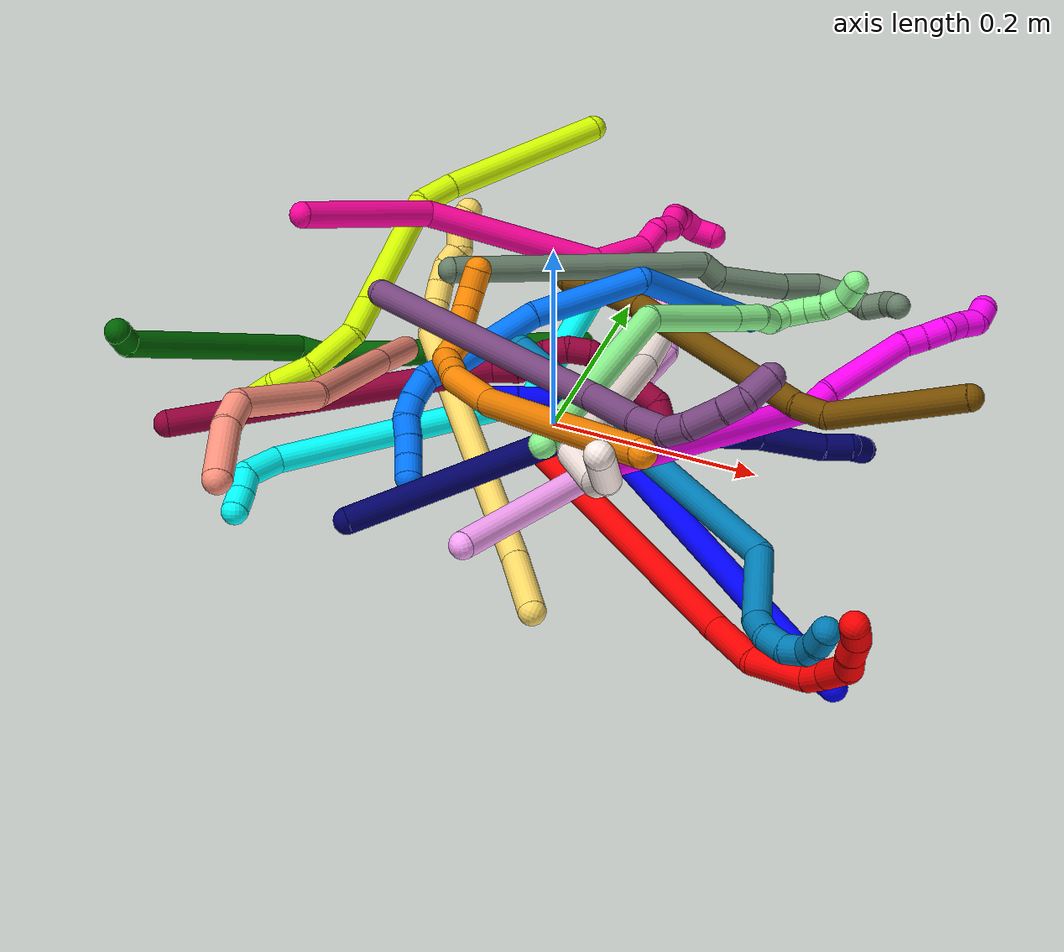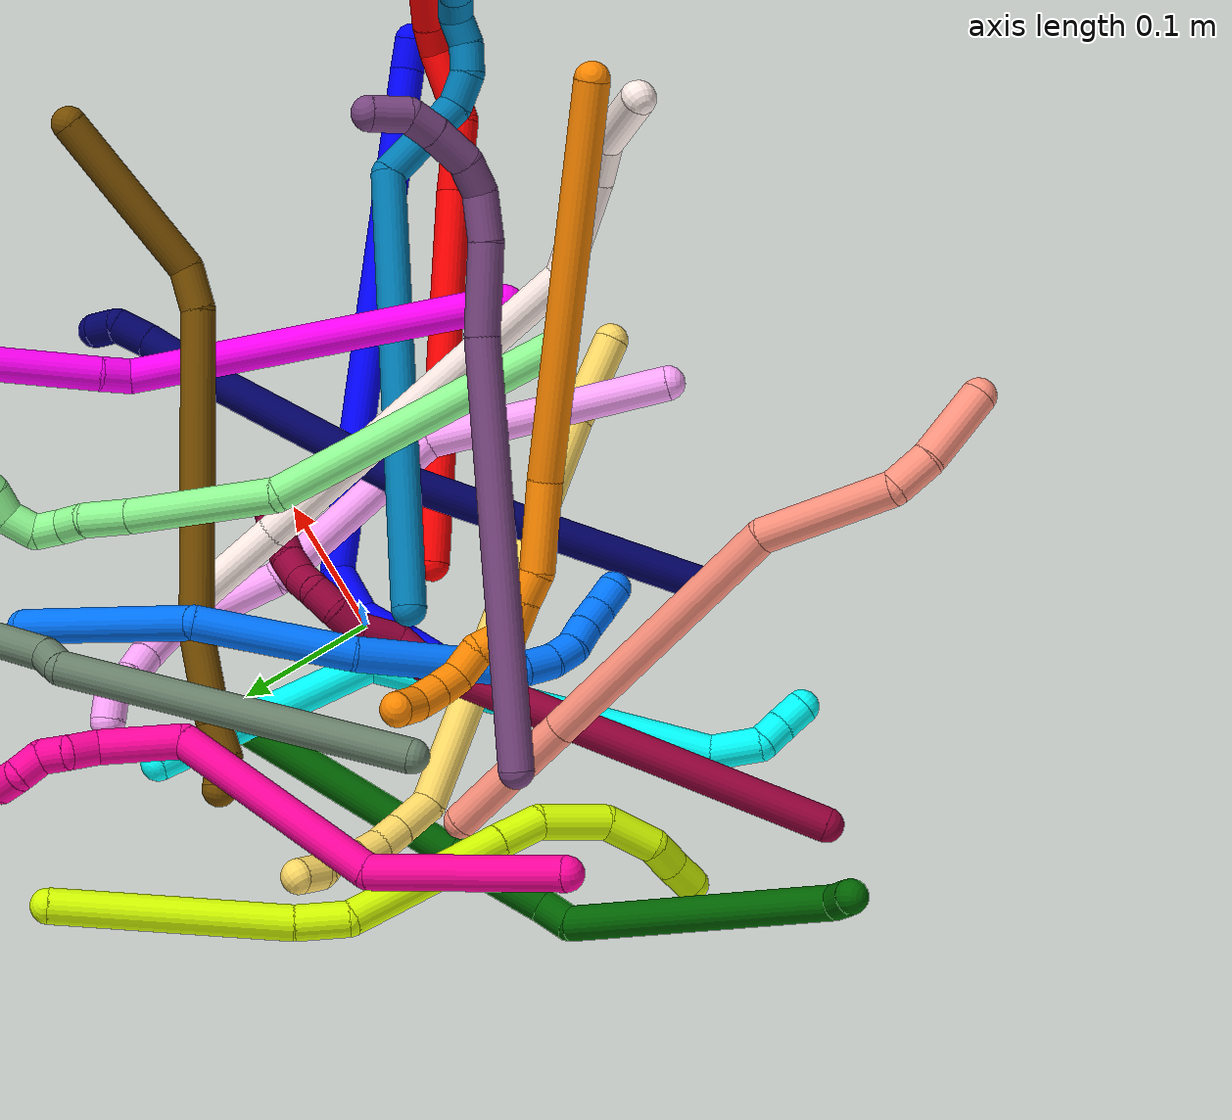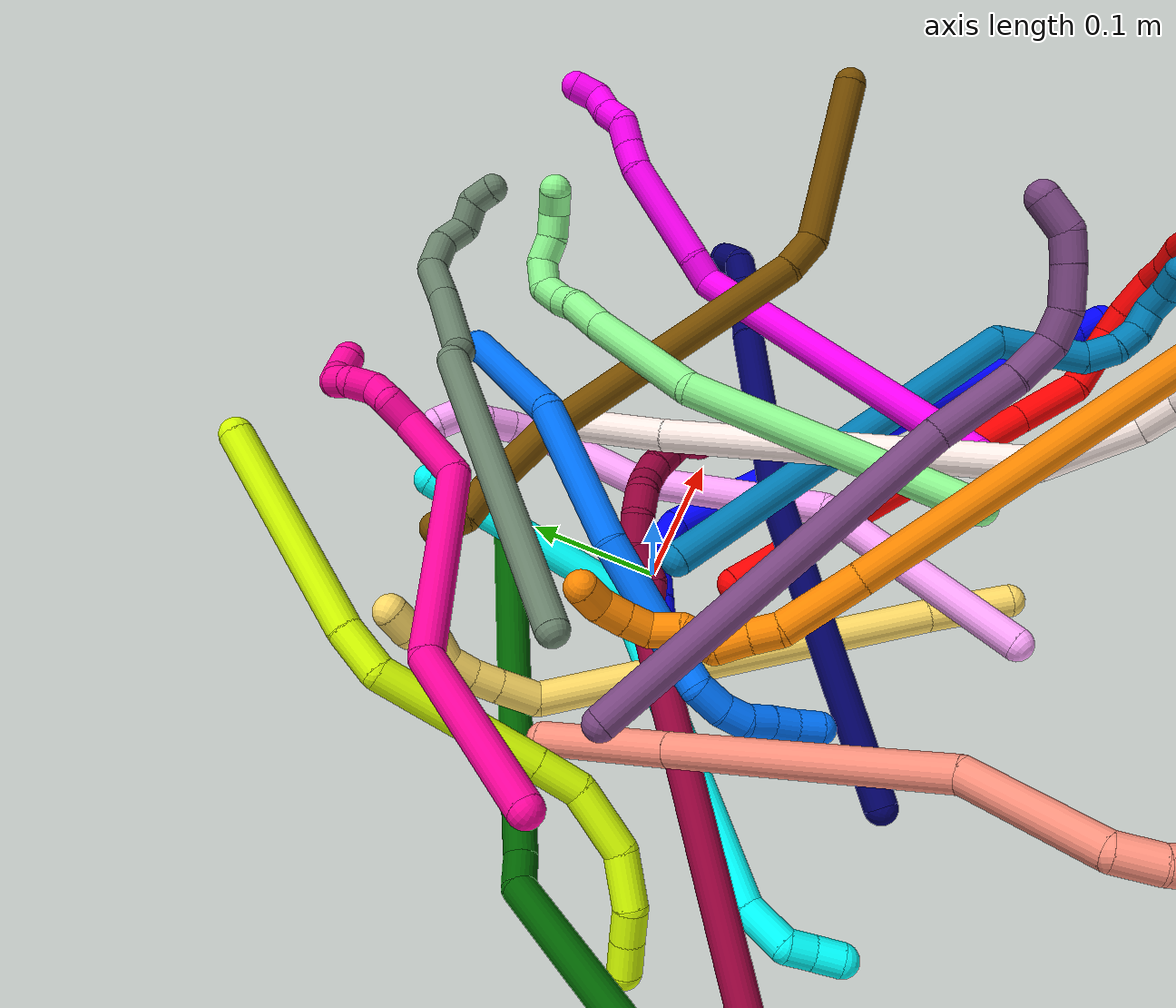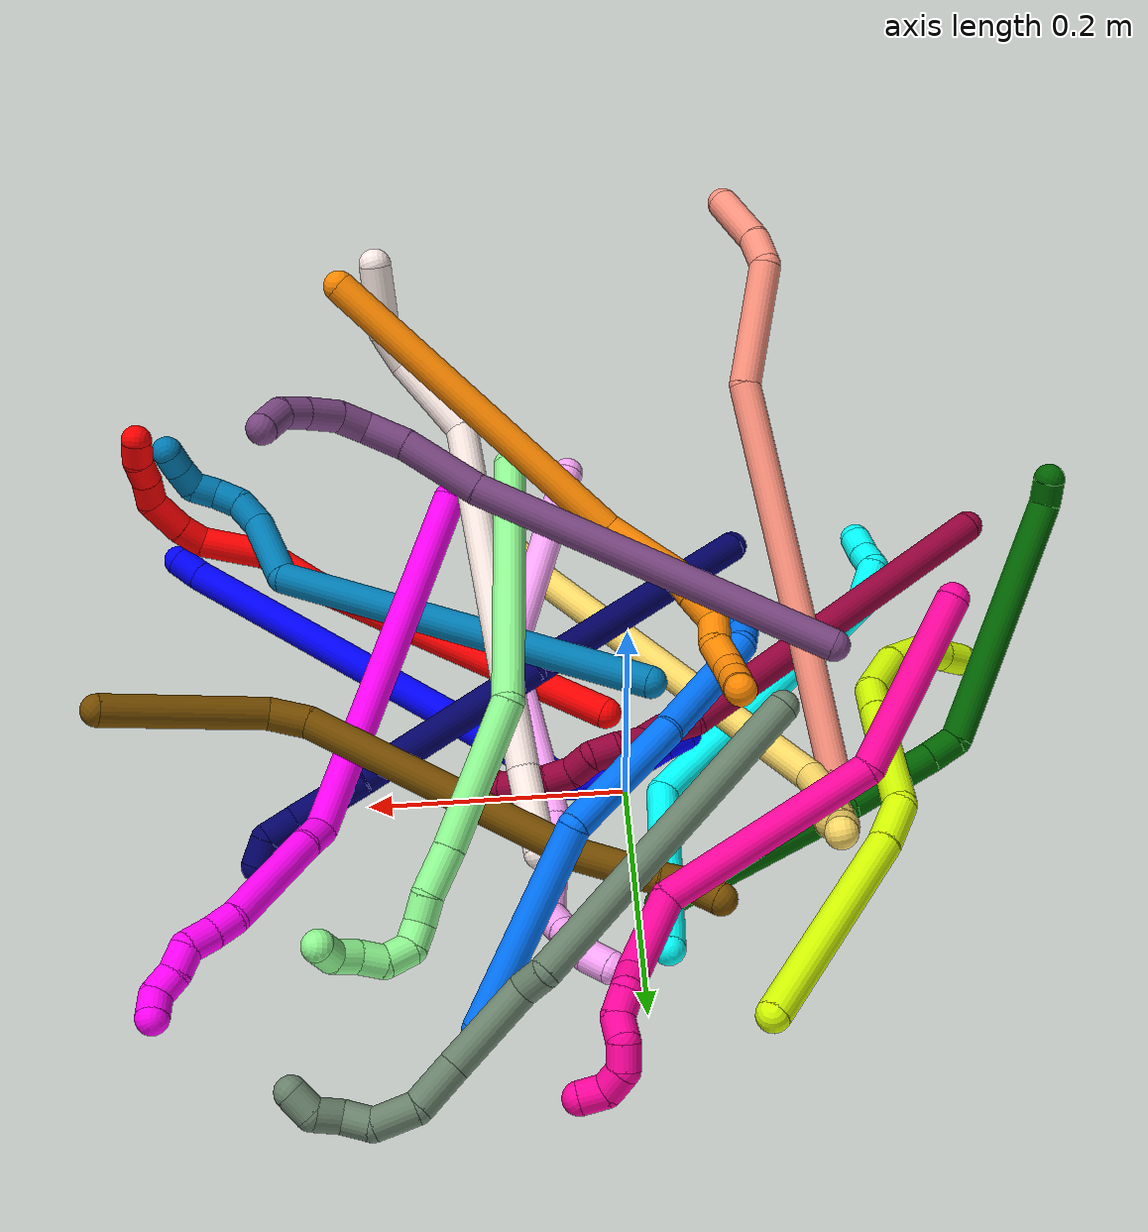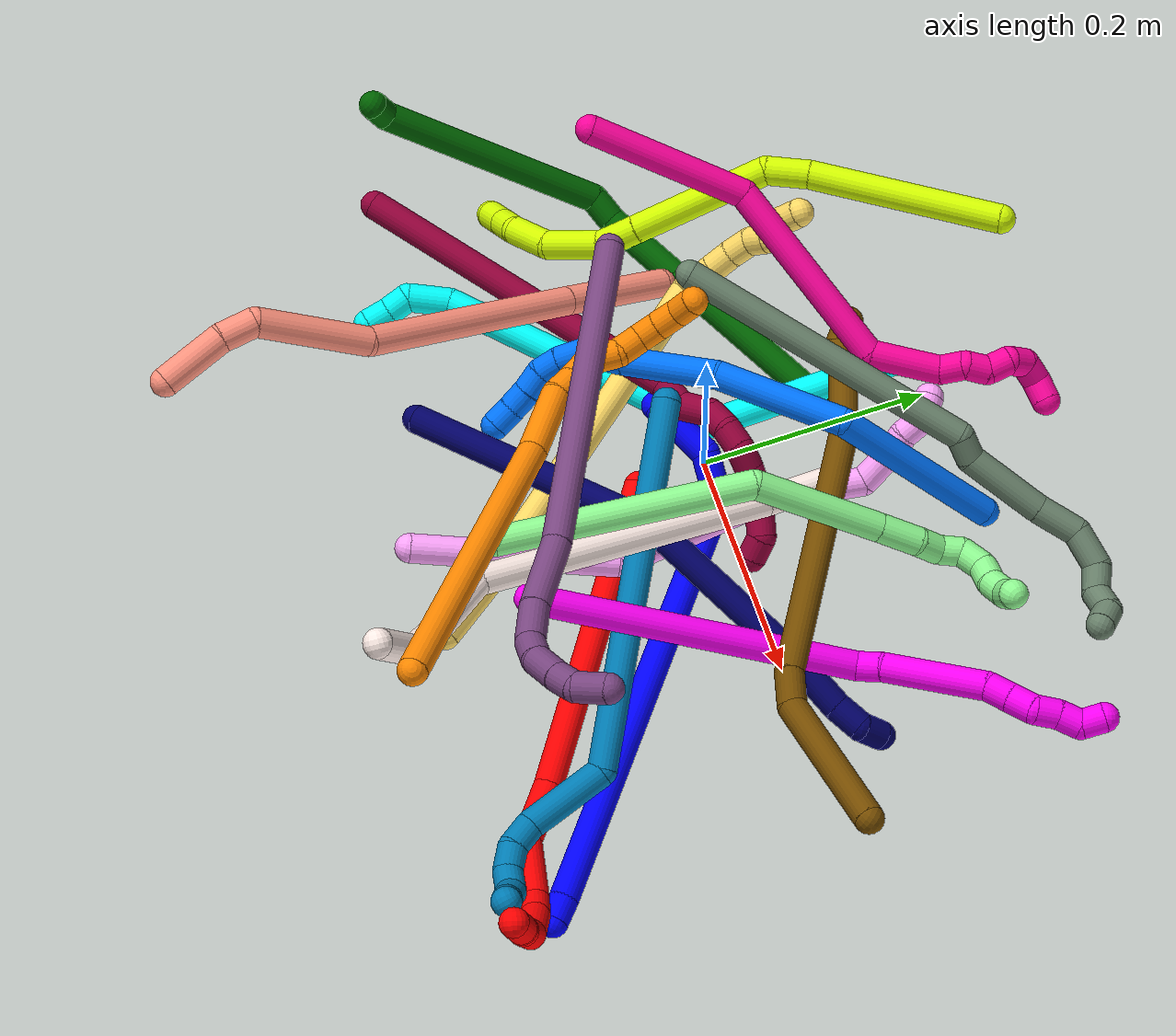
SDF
<sdf version="1.7">
 <world name="default">
  <plugin name="TubeGeneratorPlugin" filename="libtube_generator_plugin.so"/>
  <model name="photoneo_s_sensor">
   <static>1</static>
   <pose>0 0 2 1.57079 1.57079 3.14159</pose>
   <link name="link">
    <inertial><mass>0.1</mass></inertial>
    <sensor name="sensor" type="depth">
     <update_rate>30</update_rate>
     <camera>
      <horizontal_fov>1.22</horizontal_fov>
      <image><width>1920</width><height>1200</height><format>B8G8R8</format></image>
      <clip><near>0.1</near><far>4</far></clip>
      <depth_camera><output>points</output></depth_camera>
     </camera>
     <plugin name="camera_plugin" filename="libgazebo_ros_depth_camera.so">
      <baseline>0.2</baseline>
      <alwaysOn>1</alwaysOn>
      <updateRate>0.0</updateRate>
      <cameraName>camera_ir</cameraName>
      <imageTopicName>/camera/color/image_raw</imageTopicName>
      <cameraInfoTopicName>/camera/color/camera_info</cameraInfoTopicName>
      <depthImageTopicName>/camera/depth/image_raw</depthImageTopicName>
      <depthImageCameraInfoTopicName>/camera/depth/camera_info</depthImageCameraInfoTopicName>
      <pointCloudTopicName>/camera/depth/points</pointCloudTopicName>
      <frameName>fr_optical</frameName>
      <pointCloudCutoff>0.1</pointCloudCutoff>
      <pointCloudCutoffMax>2.0</pointCloudCutoffMax>
      <distortionK1>0</distortionK1>
      <distortionK2>0</distortionK2>
      <distortionK3>0</distortionK3>
      <distortionT1>0</distortionT1>
      <distortionT2>0</distortionT2>
      <CxPrime>0</CxPrime>
      <Cx>0</Cx>
      <Cy>0</Cy>
      <focalLength>0</focalLength>
      <hackBaseline>0</hackBaseline>
     </plugin>
    </sensor>
   </link>
  </model>
  <gravity>0 0 -9.8</gravity>
  <magnetic_field>6e-06 2.3e-05 -4.2e-05</magnetic_field>
  <atmosphere type="adiabatic"/>
  <physics name="default_physics" default="0" type="ode">
   <max_step_size>0.003</max_step_size>
   <real_time_factor>1</real_time_factor>
   <real_time_update_rate>1000</real_time_update_rate>
   <max_contacts>10000</max_contacts>
   <ode>
    <solver>
     <type>quick</type>
     <iters>100</iters>
     <sor>1.3</sor>
     <use_dynamic_moi_rescaling>0</use_dynamic_moi_rescaling>
    </solver>
    <constraints>
     <contact_max_correcting_vel>0</contact_max_correcting_vel>
     <contact_surface_layer>0.001</contact_surface_layer>
     <cfm>0</cfm>
     <erp>0.2</erp>
    </constraints>
   </ode>
  </physics>
  <scene><ambient>0.4 0.4 0.4 1</ambient><background>0.7 0.7 0.7 1</background><shadows>0</shadows></scene>
  <audio><device>default</device></audio>
  <spherical_coordinates>
   <surface_model>EARTH_WGS84</surface_model>
   <latitude_deg>0</latitude_deg>
   <longitude_deg>0</longitude_deg>
   <elevation>0</elevation>
   <heading_deg>0</heading_deg>
  </spherical_coordinates>
  <model name="bin">
   <static>1</static>
   <link name="bottom">
    <collision name="collision-bottom">
     <pose>0 0 -0.01 0 -0 0</pose>
     <geometry><box><size>0.8 0.6 0.02</size></box></geometry>
     <surface>
      <friction><ode><mu>100</mu><mu2>100</mu2></ode></friction>
      <contact><collide_bitmask>65535</collide_bitmask></contact>
     </surface>
    </collision>
   </link>
   <link name="west_wall">
    <collision name="collision-west_wall">
     <pose>-0.41 0 0.1 0 -0 0</pose>
     <geometry><box><size>0.02 0.6 0.2</size></box></geometry>
     <surface>
      <friction><ode><mu>100</mu><mu2>100</mu2></ode></friction>
      <contact><collide_bitmask>65535</collide_bitmask></contact>
     </surface>
    </collision>
   </link>
   <link name="east_wall">
    <collision name="collision-east_wall">
     <pose>0.41 0 0.1 0 -0 0</pose>
     <geometry><box><size>0.02 0.6 0.2</size></box></geometry>
     <surface>
      <friction><ode><mu>100</mu><mu2>100</mu2></ode></friction>
      <contact><collide_bitmask>65535</collide_bitmask></contact>
     </surface>
    </collision>
   </link>
   <link name="south_wall">
    <collision name="collision-south_wall">
     <pose>0 -0.31 0.1 0 -0 0</pose>
     <geometry><box><size>0.8 0.02 0.2</size></box></geometry>
     <surface>
      <friction><ode><mu>100</mu><mu2>100</mu2></ode></friction>
      <contact><collide_bitmask>65535</collide_bitmask></contact>
     </surface>
    </collision>
   </link>
   <link name="north_wall">
    <collision name="collision-north_wall">
     <pose>0 0.31 0.1 0 -0 0</pose>
     <geometry><box><size>0.8 0.02 0.2</size></box></geometry>
     <surface>
      <friction><ode><mu>100</mu><mu2>100</mu2></ode></friction>
      <contact><collide_bitmask>65535</collide_bitmask></contact>
     </surface>
    </collision>
   </link>
  </model>
  <model name="1">
   <static>0</static>
   <link name="1">
    <collision name="collision-cylinder-e_1_1_4">
     <pose>-0.001425 -0.001514 -0.011313 3.00856 -0.124166 -1.50168</pose>
     <geometry><cylinder><radius>0.0125</radius><length>0.023006</length></cylinder></geometry>
     <surface>
      <friction><ode><mu>1.16</mu><mu2>1.16</mu2><slip1>0</slip1><slip2>0</slip2></ode></friction>
      <contact><ode><kp>1e+06</kp><kd>1</kd><max_vel>0</max_vel><min_depth>0.001</min_depth></ode></contact>
     </surface>
    </collision>
    <visual name="visual-cylinder-e_1_1_4">
     <pose>-0.001425 -0.001514 -0.011313 3.00856 -0.124166 -1.50168</pose>
     <geometry><cylinder><radius>0.0125</radius><length>0.023006</length></cylinder></geometry>
     <material><ambient>0 0 1 1</ambient></material>
    </visual>
    <collision name="collision-cylinder-e_2_4_5">
     <pose>-0.009298 -0.001865 -0.210254 -3.13539 -0.034357 2.78465</pose>
     <geometry><cylinder><radius>0.0125</radius><length>0.375483</length></cylinder></geometry>
     <surface>
      <friction><ode><mu>1.16</mu><mu2>1.16</mu2><slip1>0</slip1><slip2>0</slip2></ode></friction>
      <contact><ode><kp>1e+06</kp><kd>1</kd><max_vel>0</max_vel><min_depth>0.001</min_depth></ode></contact>
     </surface>
    </collision>
    <visual name="visual-cylinder-e_2_4_5">
     <pose>-0.009298 -0.001865 -0.210254 -3.13539 -0.034357 2.78465</pose>
     <geometry><cylinder><radius>0.0125</radius><length>0.375483</length></cylinder></geometry>
     <material><ambient>0 0 1 1</ambient></material>
    </visual>
    <collision name="collision-cylinder-e_3_5_6">
     <pose>-0.018763 0.013321 -0.413426 -2.40759 -0.143066 0.368571</pose>
     <geometry><cylinder><radius>0.0125</radius><length>0.042302</length></cylinder></geometry>
     <surface>
      <friction><ode><mu>1.16</mu><mu2>1.16</mu2><slip1>0</slip1><slip2>0</slip2></ode></friction>
      <contact><ode><kp>1e+06</kp><kd>1</kd><max_vel>0</max_vel><min_depth>0.001</min_depth></ode></contact>
     </surface>
    </collision>
    <visual name="visual-cylinder-e_3_5_6">
     <pose>-0.018763 0.013321 -0.413426 -2.40759 -0.143066 0.368571</pose>
     <geometry><cylinder><radius>0.0125</radius><length>0.042302</length></cylinder></geometry>
     <material><ambient>0 0 1 1</ambient></material>
    </visual>
    <collision name="collision-cylinder-e_4_6_7">
     <pose>-0.032539 0.04123 -0.435996 -2.03921 -0.604984 0.939484</pose>
     <geometry><cylinder><radius>0.0125</radius><length>0.03784</length></cylinder></geometry>
     <surface>
      <friction><ode><mu>1.16</mu><mu2>1.16</mu2><slip1>0</slip1><slip2>0</slip2></ode></friction>
      <contact><ode><kp>1e+06</kp><kd>1</kd><max_vel>0</max_vel><min_depth>0.001</min_depth></ode></contact>
     </surface>
    </collision>
    <visual name="visual-cylinder-e_4_6_7">
     <pose>-0.032539 0.04123 -0.435996 -2.03921 -0.604984 0.939484</pose>
     <geometry><cylinder><radius>0.0125</radius><length>0.03784</length></cylinder></geometry>
     <material><ambient>0 0 1 1</ambient></material>
    </visual>
    <collision name="collision-cylinder-e_5_7_2">
     <pose>-0.049982 0.062341 -0.447182 -2.09327 -0.675628 1.09204</pose>
     <geometry><cylinder><radius>0.0125</radius><length>0.021369</length></cylinder></geometry>
     <surface>
      <friction><ode><mu>1.16</mu><mu2>1.16</mu2><slip1>0</slip1><slip2>0</slip2></ode></friction>
      <contact><ode><kp>1e+06</kp><kd>1</kd><max_vel>0</max_vel><min_depth>0.001</min_depth></ode></contact>
     </surface>
    </collision>
    <visual name="visual-cylinder-e_5_7_2">
     <pose>-0.049982 0.062341 -0.447182 -2.09327 -0.675628 1.09204</pose>
     <geometry><cylinder><radius>0.0125</radius><length>0.021369</length></cylinder></geometry>
     <material><ambient>0 0 1 1</ambient></material>
    </visual>
    <collision name="collision-sphere-2">
     <pose>-0.056664 0.069566 -0.451342 0 -0 0</pose>
     <geometry><sphere><radius>0.0125</radius></sphere></geometry>
     <surface>
      <friction><ode><mu>1.16</mu><mu2>1.16</mu2><slip1>0</slip1><slip2>0</slip2></ode></friction>
      <contact><ode><kp>1e+06</kp><kd>1</kd><max_vel>0</max_vel><min_depth>0.001</min_depth></ode></contact>
     </surface>
    </collision>
    <visual name="visual-sphere-2">
     <pose>-0.056664 0.069566 -0.451342 0 -0 0</pose>
     <geometry><sphere><radius>0.0125</radius></sphere></geometry>
     <material><ambient>0 0 1 1</ambient></material>
    </visual>
    <collision name="collision-sphere-7">
     <pose>-0.0433 0.055116 -0.443022 0 -0 0</pose>
     <geometry><sphere><radius>0.0125</radius></sphere></geometry>
     <surface>
      <friction><ode><mu>1.16</mu><mu2>1.16</mu2><slip1>0</slip1><slip2>0</slip2></ode></friction>
      <contact><ode><kp>1e+06</kp><kd>1</kd><max_vel>0</max_vel><min_depth>0.001</min_depth></ode></contact>
     </surface>
    </collision>
    <visual name="visual-sphere-7">
     <pose>-0.0433 0.055116 -0.443022 0 -0 0</pose>
     <geometry><sphere><radius>0.0125</radius></sphere></geometry>
     <material><ambient>0 0 1 1</ambient></material>
    </visual>
    <collision name="collision-sphere-6">
     <pose>-0.021778 0.027344 -0.42897 0 -0 0</pose>
     <geometry><sphere><radius>0.0125</radius></sphere></geometry>
     <surface>
      <friction><ode><mu>1.16</mu><mu2>1.16</mu2><slip1>0</slip1><slip2>0</slip2></ode></friction>
      <contact><ode><kp>1e+06</kp><kd>1</kd><max_vel>0</max_vel><min_depth>0.001</min_depth></ode></contact>
     </surface>
    </collision>
    <visual name="visual-sphere-6">
     <pose>-0.021778 0.027344 -0.42897 0 -0 0</pose>
     <geometry><sphere><radius>0.0125</radius></sphere></geometry>
     <material><ambient>0 0 1 1</ambient></material>
    </visual>
    <collision name="collision-sphere-5">
     <pose>-0.015747 -0.000702 -0.397881 0 -0 0</pose>
     <geometry><sphere><radius>0.0125</radius></sphere></geometry>
     <surface>
      <friction><ode><mu>1.16</mu><mu2>1.16</mu2><slip1>0</slip1><slip2>0</slip2></ode></friction>
      <contact><ode><kp>1e+06</kp><kd>1</kd><max_vel>0</max_vel><min_depth>0.001</min_depth></ode></contact>
     </surface>
    </collision>
    <visual name="visual-sphere-5">
     <pose>-0.015747 -0.000702 -0.397881 0 -0 0</pose>
     <geometry><sphere><radius>0.0125</radius></sphere></geometry>
     <material><ambient>0 0 1 1</ambient></material>
    </visual>
    <collision name="collision-sphere-1">
     <geometry><sphere><radius>0.0125</radius></sphere></geometry>
     <surface>
      <friction><ode><mu>1.16</mu><mu2>1.16</mu2><slip1>0</slip1><slip2>0</slip2></ode></friction>
      <contact><ode><kp>1e+06</kp><kd>1</kd><max_vel>0</max_vel><min_depth>0.001</min_depth></ode></contact>
     </surface>
    </collision>
    <visual name="visual-sphere-1">
     <geometry><sphere><radius>0.0125</radius></sphere></geometry>
     <material><ambient>0 0 1 1</ambient></material>
    </visual>
    <collision name="collision-sphere-4">
     <pose>-0.002849 -0.003028 -0.022627 0 -0 0</pose>
     <geometry><sphere><radius>0.0125</radius></sphere></geometry>
     <surface>
      <friction><ode><mu>1.16</mu><mu2>1.16</mu2><slip1>0</slip1><slip2>0</slip2></ode></friction>
      <contact><ode><kp>1e+06</kp><kd>1</kd><max_vel>0</max_vel><min_depth>0.001</min_depth></ode></contact>
     </surface>
    </collision>
    <visual name="visual-sphere-4">
     <pose>-0.002849 -0.003028 -0.022627 0 -0 0</pose>
     <geometry><sphere><radius>0.0125</radius></sphere></geometry>
     <material><ambient>0 0 1 1</ambient></material>
    </visual>
    <inertial>
     <pose>-0.013234 0.005441 -0.2455 0 -0 0</pose>
     <mass>0.5</mass>
     <inertia>
      <ixx>-0.002587</ixx>
      <ixy>0</ixy>
      <ixz>0</ixz>
      <iyy>0.005701</iyy>
      <iyz>0</iyz>
      <izz>8.5e-05</izz>
     </inertia>
    </inertial>
   </link>
   <pose>0.351319 -0.251631 0.015222 1.5972 -0.76327 0.845753</pose>
  </model>
  <model name="2">
   <static>0</static>
   <link name="2">
    <collision name="collision-cylinder-e_1_1_4">
     <pose>0.046267 0.005637 0.129977 -0.043342 0.341679 -0.007478</pose>
     <geometry><cylinder><radius>0.0125</radius><length>0.276161</length></cylinder></geometry>
     <surface>
      <friction><ode><mu>1.16</mu><mu2>1.16</mu2><slip1>0</slip1><slip2>0</slip2></ode></friction>
      <contact><ode><kp>1e+06</kp><kd>1</kd><max_vel>0</max_vel><min_depth>0.001</min_depth></ode></contact>
     </surface>
    </collision>
    <visual name="visual-cylinder-e_1_1_4">
     <pose>0.046267 0.005637 0.129977 -0.043342 0.341679 -0.007478</pose>
     <geometry><cylinder><radius>0.0125</radius><length>0.276161</length></cylinder></geometry>
     <material><ambient>1 0 0 1</ambient></material>
    </visual>
    <collision name="collision-cylinder-e_2_4_5">
     <pose>0.104665 0.009516 0.283589 0.074232 0.473089 0.017902</pose>
     <geometry><cylinder><radius>0.0125</radius><length>0.053252</length></cylinder></geometry>
     <surface>
      <friction><ode><mu>1.16</mu><mu2>1.16</mu2><slip1>0</slip1><slip2>0</slip2></ode></friction>
      <contact><ode><kp>1e+06</kp><kd>1</kd><max_vel>0</max_vel><min_depth>0.001</min_depth></ode></contact>
     </surface>
    </collision>
    <visual name="visual-cylinder-e_2_4_5">
     <pose>0.104665 0.009516 0.283589 0.074232 0.473089 0.017902</pose>
     <geometry><cylinder><radius>0.0125</radius><length>0.053252</length></cylinder></geometry>
     <material><ambient>1 0 0 1</ambient></material>
    </visual>
    <collision name="collision-cylinder-e_3_5_6">
     <pose>0.119041 -0.000747 0.332263 0.327464 0.084672 0.013997</pose>
     <geometry><cylinder><radius>0.0125</radius><length>0.053075</length></cylinder></geometry>
     <surface>
      <friction><ode><mu>1.16</mu><mu2>1.16</mu2><slip1>0</slip1><slip2>0</slip2></ode></friction>
      <contact><ode><kp>1e+06</kp><kd>1</kd><max_vel>0</max_vel><min_depth>0.001</min_depth></ode></contact>
     </surface>
    </collision>
    <visual name="visual-cylinder-e_3_5_6">
     <pose>0.119041 -0.000747 0.332263 0.327464 0.084672 0.013997</pose>
     <geometry><cylinder><radius>0.0125</radius><length>0.053075</length></cylinder></geometry>
     <material><ambient>1 0 0 1</ambient></material>
    </visual>
    <collision name="collision-cylinder-e_4_6_7">
     <pose>0.125128 -0.016306 0.364623 0.76668 0.361283 0.147042</pose>
     <geometry><cylinder><radius>0.0125</radius><length>0.021739</length></cylinder></geometry>
     <surface>
      <friction><ode><mu>1.16</mu><mu2>1.16</mu2><slip1>0</slip1><slip2>0</slip2></ode></friction>
      <contact><ode><kp>1e+06</kp><kd>1</kd><max_vel>0</max_vel><min_depth>0.001</min_depth></ode></contact>
     </surface>
    </collision>
    <visual name="visual-cylinder-e_4_6_7">
     <pose>0.125128 -0.016306 0.364623 0.76668 0.361283 0.147042</pose>
     <geometry><cylinder><radius>0.0125</radius><length>0.021739</length></cylinder></geometry>
     <material><ambient>1 0 0 1</ambient></material>
    </visual>
    <collision name="collision-cylinder-e_5_7_8">
     <pose>0.137245 -0.034048 0.381049 0.865352 0.532645 0.250675</pose>
     <geometry><cylinder><radius>0.0125</radius><length>0.032593</length></cylinder></geometry>
     <surface>
      <friction><ode><mu>1.16</mu><mu2>1.16</mu2><slip1>0</slip1><slip2>0</slip2></ode></friction>
      <contact><ode><kp>1e+06</kp><kd>1</kd><max_vel>0</max_vel><min_depth>0.001</min_depth></ode></contact>
     </surface>
    </collision>
    <visual name="visual-cylinder-e_5_7_8">
     <pose>0.137245 -0.034048 0.381049 0.865352 0.532645 0.250675</pose>
     <geometry><cylinder><radius>0.0125</radius><length>0.032593</length></cylinder></geometry>
     <material><ambient>1 0 0 1</ambient></material>
    </visual>
    <collision name="collision-cylinder-e_6_8_9">
     <pose>0.153248 -0.052638 0.389958 1.59524 0.774038 0.791276</pose>
     <geometry><cylinder><radius>0.0125</radius><length>0.022107</length></cylinder></geometry>
     <surface>
      <friction><ode><mu>1.16</mu><mu2>1.16</mu2><slip1>0</slip1><slip2>0</slip2></ode></friction>
      <contact><ode><kp>1e+06</kp><kd>1</kd><max_vel>0</max_vel><min_depth>0.001</min_depth></ode></contact>
     </surface>
    </collision>
    <visual name="visual-cylinder-e_6_8_9">
     <pose>0.153248 -0.052638 0.389958 1.59524 0.774038 0.791276</pose>
     <geometry><cylinder><radius>0.0125</radius><length>0.022107</length></cylinder></geometry>
     <material><ambient>1 0 0 1</ambient></material>
    </visual>
    <collision name="collision-cylinder-e_7_9_10">
     <pose>0.166589 -0.069429 0.390328 1.50752 0.562439 0.52957</pose>
     <geometry><cylinder><radius>0.0125</radius><length>0.021057</length></cylinder></geometry>
     <surface>
      <friction><ode><mu>1.16</mu><mu2>1.16</mu2><slip1>0</slip1><slip2>0</slip2></ode></friction>
      <contact><ode><kp>1e+06</kp><kd>1</kd><max_vel>0</max_vel><min_depth>0.001</min_depth></ode></contact>
     </surface>
    </collision>
    <visual name="visual-cylinder-e_7_9_10">
     <pose>0.166589 -0.069429 0.390328 1.50752 0.562439 0.52957</pose>
     <geometry><cylinder><radius>0.0125</radius><length>0.021057</length></cylinder></geometry>
     <material><ambient>1 0 0 1</ambient></material>
    </visual>
    <collision name="collision-cylinder-e_8_10_2">
     <pose>0.179356 -0.085121 0.389247 1.80785 0.796285 0.981454</pose>
     <geometry><cylinder><radius>0.0125</radius><length>0.020016</length></cylinder></geometry>
     <surface>
      <friction><ode><mu>1.16</mu><mu2>1.16</mu2><slip1>0</slip1><slip2>0</slip2></ode></friction>
      <contact><ode><kp>1e+06</kp><kd>1</kd><max_vel>0</max_vel><min_depth>0.001</min_depth></ode></contact>
     </surface>
    </collision>
    <visual name="visual-cylinder-e_8_10_2">
     <pose>0.179356 -0.085121 0.389247 1.80785 0.796285 0.981454</pose>
     <geometry><cylinder><radius>0.0125</radius><length>0.020016</length></cylinder></geometry>
     <material><ambient>1 0 0 1</ambient></material>
    </visual>
    <collision name="collision-sphere-2">
     <pose>0.186509 -0.091924 0.387604 0 -0 0</pose>
     <geometry><sphere><radius>0.0125</radius></sphere></geometry>
     <surface>
      <friction><ode><mu>1.16</mu><mu2>1.16</mu2><slip1>0</slip1><slip2>0</slip2></ode></friction>
      <contact><ode><kp>1e+06</kp><kd>1</kd><max_vel>0</max_vel><min_depth>0.001</min_depth></ode></contact>
     </surface>
    </collision>
    <visual name="visual-sphere-2">
     <pose>0.186509 -0.091924 0.387604 0 -0 0</pose>
     <geometry><sphere><radius>0.0125</radius></sphere></geometry>
     <material><ambient>1 0 0 1</ambient></material>
    </visual>
    <collision name="collision-sphere-10">
     <pose>0.172203 -0.078317 0.390891 0 -0 0</pose>
     <geometry><sphere><radius>0.0125</radius></sphere></geometry>
     <surface>
      <friction><ode><mu>1.16</mu><mu2>1.16</mu2><slip1>0</slip1><slip2>0</slip2></ode></friction>
      <contact><ode><kp>1e+06</kp><kd>1</kd><max_vel>0</max_vel><min_depth>0.001</min_depth></ode></contact>
     </surface>
    </collision>
    <visual name="visual-sphere-10">
     <pose>0.172203 -0.078317 0.390891 0 -0 0</pose>
     <geometry><sphere><radius>0.0125</radius></sphere></geometry>
     <material><ambient>1 0 0 1</ambient></material>
    </visual>
    <collision name="collision-sphere-9">
     <pose>0.160974 -0.06054 0.389765 0 -0 0</pose>
     <geometry><sphere><radius>0.0125</radius></sphere></geometry>
     <surface>
      <friction><ode><mu>1.16</mu><mu2>1.16</mu2><slip1>0</slip1><slip2>0</slip2></ode></friction>
      <contact><ode><kp>1e+06</kp><kd>1</kd><max_vel>0</max_vel><min_depth>0.001</min_depth></ode></contact>
     </surface>
    </collision>
    <visual name="visual-sphere-9">
     <pose>0.160974 -0.06054 0.389765 0 -0 0</pose>
     <geometry><sphere><radius>0.0125</radius></sphere></geometry>
     <material><ambient>1 0 0 1</ambient></material>
    </visual>
    <collision name="collision-sphere-4">
     <pose>0.092533 0.011274 0.259953 0 -0 0</pose>
     <geometry><sphere><radius>0.0125</radius></sphere></geometry>
     <surface>
      <friction><ode><mu>1.16</mu><mu2>1.16</mu2><slip1>0</slip1><slip2>0</slip2></ode></friction>
      <contact><ode><kp>1e+06</kp><kd>1</kd><max_vel>0</max_vel><min_depth>0.001</min_depth></ode></contact>
     </surface>
    </collision>
    <visual name="visual-sphere-4">
     <pose>0.092533 0.011274 0.259953 0 -0 0</pose>
     <geometry><sphere><radius>0.0125</radius></sphere></geometry>
     <material><ambient>1 0 0 1</ambient></material>
    </visual>
    <collision name="collision-sphere-1">
     <geometry><sphere><radius>0.0125</radius></sphere></geometry>
     <surface>
      <friction><ode><mu>1.16</mu><mu2>1.16</mu2><slip1>0</slip1><slip2>0</slip2></ode></friction>
      <contact><ode><kp>1e+06</kp><kd>1</kd><max_vel>0</max_vel><min_depth>0.001</min_depth></ode></contact>
     </surface>
    </collision>
    <visual name="visual-sphere-1">
     <geometry><sphere><radius>0.0125</radius></sphere></geometry>
     <material><ambient>1 0 0 1</ambient></material>
    </visual>
    <collision name="collision-sphere-8">
     <pose>0.145521 -0.044736 0.390151 0 -0 0</pose>
     <geometry><sphere><radius>0.0125</radius></sphere></geometry>
     <surface>
      <friction><ode><mu>1.16</mu><mu2>1.16</mu2><slip1>0</slip1><slip2>0</slip2></ode></friction>
      <contact><ode><kp>1e+06</kp><kd>1</kd><max_vel>0</max_vel><min_depth>0.001</min_depth></ode></contact>
     </surface>
    </collision>
    <visual name="visual-sphere-8">
     <pose>0.145521 -0.044736 0.390151 0 -0 0</pose>
     <geometry><sphere><radius>0.0125</radius></sphere></geometry>
     <material><ambient>1 0 0 1</ambient></material>
    </visual>
    <collision name="collision-sphere-5">
     <pose>0.116797 0.007758 0.307226 0 -0 0</pose>
     <geometry><sphere><radius>0.0125</radius></sphere></geometry>
     <surface>
      <friction><ode><mu>1.16</mu><mu2>1.16</mu2><slip1>0</slip1><slip2>0</slip2></ode></friction>
      <contact><ode><kp>1e+06</kp><kd>1</kd><max_vel>0</max_vel><min_depth>0.001</min_depth></ode></contact>
     </surface>
    </collision>
    <visual name="visual-sphere-5">
     <pose>0.116797 0.007758 0.307226 0 -0 0</pose>
     <geometry><sphere><radius>0.0125</radius></sphere></geometry>
     <material><ambient>1 0 0 1</ambient></material>
    </visual>
    <collision name="collision-sphere-6">
     <pose>0.121285 -0.009252 0.3573 0 -0 0</pose>
     <geometry><sphere><radius>0.0125</radius></sphere></geometry>
     <surface>
      <friction><ode><mu>1.16</mu><mu2>1.16</mu2><slip1>0</slip1><slip2>0</slip2></ode></friction>
      <contact><ode><kp>1e+06</kp><kd>1</kd><max_vel>0</max_vel><min_depth>0.001</min_depth></ode></contact>
     </surface>
    </collision>
    <visual name="visual-sphere-6">
     <pose>0.121285 -0.009252 0.3573 0 -0 0</pose>
     <geometry><sphere><radius>0.0125</radius></sphere></geometry>
     <material><ambient>1 0 0 1</ambient></material>
    </visual>
    <collision name="collision-sphere-7">
     <pose>0.12897 -0.02336 0.371946 0 -0 0</pose>
     <geometry><sphere><radius>0.0125</radius></sphere></geometry>
     <surface>
      <friction><ode><mu>1.16</mu><mu2>1.16</mu2><slip1>0</slip1><slip2>0</slip2></ode></friction>
      <contact><ode><kp>1e+06</kp><kd>1</kd><max_vel>0</max_vel><min_depth>0.001</min_depth></ode></contact>
     </surface>
    </collision>
    <visual name="visual-sphere-7">
     <pose>0.12897 -0.02336 0.371946 0 -0 0</pose>
     <geometry><sphere><radius>0.0125</radius></sphere></geometry>
     <material><ambient>1 0 0 1</ambient></material>
    </visual>
    <inertial>
     <pose>0.084696 -0.00754 0.227216 0 -0 0</pose>
     <mass>0.5</mass>
     <inertia>
      <ixx>0.001705</ixx>
      <ixy>0</ixy>
      <ixz>0</ixz>
      <iyy>0.001783</iyy>
      <iyz>0</iyz>
      <izz>-0.000634</izz>
     </inertia>
    </inertial>
   </link>
   <pose>0.010136 -0.062239 0.020366 -1.77056 -0.520572 -1.756</pose>
  </model>
  <model name="3">
   <static>0</static>
   <link name="3">
    <collision name="collision-cylinder-e_1_1_4">
     <pose>-0.011052 -0.051392 -0.067152 2.48837 -0.129967 -0.379591</pose>
     <geometry><cylinder><radius>0.0125</radius><length>0.170561</length></cylinder></geometry>
     <surface>
      <friction><ode><mu>1.16</mu><mu2>1.16</mu2><slip1>0</slip1><slip2>0</slip2></ode></friction>
      <contact><ode><kp>1e+06</kp><kd>1</kd><max_vel>0</max_vel><min_depth>0.001</min_depth></ode></contact>
     </surface>
    </collision>
    <visual name="visual-cylinder-e_1_1_4">
     <pose>-0.011052 -0.051392 -0.067152 2.48837 -0.129967 -0.379591</pose>
     <geometry><cylinder><radius>0.0125</radius><length>0.170561</length></cylinder></geometry>
     <material><ambient>0.003922 1 0.996078 1</ambient></material>
    </visual>
    <collision name="collision-cylinder-e_2_4_5">
     <pose>-0.108221 -0.18658 -0.170267 1.97619 -0.756805 -1.08561</pose>
     <geometry><cylinder><radius>0.0125</radius><length>0.250846</length></cylinder></geometry>
     <surface>
      <friction><ode><mu>1.16</mu><mu2>1.16</mu2><slip1>0</slip1><slip2>0</slip2></ode></friction>
      <contact><ode><kp>1e+06</kp><kd>1</kd><max_vel>0</max_vel><min_depth>0.001</min_depth></ode></contact>
     </surface>
    </collision>
    <visual name="visual-cylinder-e_2_4_5">
     <pose>-0.108221 -0.18658 -0.170267 1.97619 -0.756805 -1.08561</pose>
     <geometry><cylinder><radius>0.0125</radius><length>0.250846</length></cylinder></geometry>
     <material><ambient>0.003922 1 0.996078 1</ambient></material>
    </visual>
    <collision name="collision-cylinder-e_3_5_6">
     <pose>-0.200299 -0.285944 -0.213935 2.03038 -0.33067 -0.525111</pose>
     <geometry><cylinder><radius>0.0125</radius><length>0.036733</length></cylinder></geometry>
     <surface>
      <friction><ode><mu>1.16</mu><mu2>1.16</mu2><slip1>0</slip1><slip2>0</slip2></ode></friction>
      <contact><ode><kp>1e+06</kp><kd>1</kd><max_vel>0</max_vel><min_depth>0.001</min_depth></ode></contact>
     </surface>
    </collision>
    <visual name="visual-cylinder-e_3_5_6">
     <pose>-0.200299 -0.285944 -0.213935 2.03038 -0.33067 -0.525111</pose>
     <geometry><cylinder><radius>0.0125</radius><length>0.036733</length></cylinder></geometry>
     <material><ambient>0.003922 1 0.996078 1</ambient></material>
    </visual>
    <collision name="collision-cylinder-e_4_6_7">
     <pose>-0.204968 -0.306373 -0.230615 2.64527 0.126129 0.48849</pose>
     <geometry><cylinder><radius>0.0125</radius><length>0.020575</length></cylinder></geometry>
     <surface>
      <friction><ode><mu>1.16</mu><mu2>1.16</mu2><slip1>0</slip1><slip2>0</slip2></ode></friction>
      <contact><ode><kp>1e+06</kp><kd>1</kd><max_vel>0</max_vel><min_depth>0.001</min_depth></ode></contact>
     </surface>
    </collision>
    <visual name="visual-cylinder-e_4_6_7">
     <pose>-0.204968 -0.306373 -0.230615 2.64527 0.126129 0.48849</pose>
     <geometry><cylinder><radius>0.0125</radius><length>0.020575</length></cylinder></geometry>
     <material><ambient>0.003922 1 0.996078 1</ambient></material>
    </visual>
    <collision name="collision-cylinder-e_5_7_2">
     <pose>-0.202189 -0.317778 -0.247849 2.47153 0.139979 0.397405</pose>
     <geometry><cylinder><radius>0.0125</radius><length>0.021286</length></cylinder></geometry>
     <surface>
      <friction><ode><mu>1.16</mu><mu2>1.16</mu2><slip1>0</slip1><slip2>0</slip2></ode></friction>
      <contact><ode><kp>1e+06</kp><kd>1</kd><max_vel>0</max_vel><min_depth>0.001</min_depth></ode></contact>
     </surface>
    </collision>
    <visual name="visual-cylinder-e_5_7_2">
     <pose>-0.202189 -0.317778 -0.247849 2.47153 0.139979 0.397405</pose>
     <geometry><cylinder><radius>0.0125</radius><length>0.021286</length></cylinder></geometry>
     <material><ambient>0.003922 1 0.996078 1</ambient></material>
    </visual>
    <collision name="collision-sphere-2">
     <pose>-0.200704 -0.324323 -0.25611 0 -0 0</pose>
     <geometry><sphere><radius>0.0125</radius></sphere></geometry>
     <surface>
      <friction><ode><mu>1.16</mu><mu2>1.16</mu2><slip1>0</slip1><slip2>0</slip2></ode></friction>
      <contact><ode><kp>1e+06</kp><kd>1</kd><max_vel>0</max_vel><min_depth>0.001</min_depth></ode></contact>
     </surface>
    </collision>
    <visual name="visual-sphere-2">
     <pose>-0.200704 -0.324323 -0.25611 0 -0 0</pose>
     <geometry><sphere><radius>0.0125</radius></sphere></geometry>
     <material><ambient>0.003922 1 0.996078 1</ambient></material>
    </visual>
    <collision name="collision-sphere-7">
     <pose>-0.203674 -0.311232 -0.239589 0 -0 0</pose>
     <geometry><sphere><radius>0.0125</radius></sphere></geometry>
     <surface>
      <friction><ode><mu>1.16</mu><mu2>1.16</mu2><slip1>0</slip1><slip2>0</slip2></ode></friction>
      <contact><ode><kp>1e+06</kp><kd>1</kd><max_vel>0</max_vel><min_depth>0.001</min_depth></ode></contact>
     </surface>
    </collision>
    <visual name="visual-sphere-7">
     <pose>-0.203674 -0.311232 -0.239589 0 -0 0</pose>
     <geometry><sphere><radius>0.0125</radius></sphere></geometry>
     <material><ambient>0.003922 1 0.996078 1</ambient></material>
    </visual>
    <collision name="collision-sphere-6">
     <pose>-0.206263 -0.301513 -0.221641 0 -0 0</pose>
     <geometry><sphere><radius>0.0125</radius></sphere></geometry>
     <surface>
      <friction><ode><mu>1.16</mu><mu2>1.16</mu2><slip1>0</slip1><slip2>0</slip2></ode></friction>
      <contact><ode><kp>1e+06</kp><kd>1</kd><max_vel>0</max_vel><min_depth>0.001</min_depth></ode></contact>
     </surface>
    </collision>
    <visual name="visual-sphere-6">
     <pose>-0.206263 -0.301513 -0.221641 0 -0 0</pose>
     <geometry><sphere><radius>0.0125</radius></sphere></geometry>
     <material><ambient>0.003922 1 0.996078 1</ambient></material>
    </visual>
    <collision name="collision-sphere-5">
     <pose>-0.194336 -0.270375 -0.20623 0 -0 0</pose>
     <geometry><sphere><radius>0.0125</radius></sphere></geometry>
     <surface>
      <friction><ode><mu>1.16</mu><mu2>1.16</mu2><slip1>0</slip1><slip2>0</slip2></ode></friction>
      <contact><ode><kp>1e+06</kp><kd>1</kd><max_vel>0</max_vel><min_depth>0.001</min_depth></ode></contact>
     </surface>
    </collision>
    <visual name="visual-sphere-5">
     <pose>-0.194336 -0.270375 -0.20623 0 -0 0</pose>
     <geometry><sphere><radius>0.0125</radius></sphere></geometry>
     <material><ambient>0.003922 1 0.996078 1</ambient></material>
    </visual>
    <collision name="collision-sphere-1">
     <geometry><sphere><radius>0.0125</radius></sphere></geometry>
     <surface>
      <friction><ode><mu>1.16</mu><mu2>1.16</mu2><slip1>0</slip1><slip2>0</slip2></ode></friction>
      <contact><ode><kp>1e+06</kp><kd>1</kd><max_vel>0</max_vel><min_depth>0.001</min_depth></ode></contact>
     </surface>
    </collision>
    <visual name="visual-sphere-1">
     <geometry><sphere><radius>0.0125</radius></sphere></geometry>
     <material><ambient>0.003922 1 0.996078 1</ambient></material>
    </visual>
    <collision name="collision-sphere-4">
     <pose>-0.022105 -0.102784 -0.134305 0 -0 0</pose>
     <geometry><sphere><radius>0.0125</radius></sphere></geometry>
     <surface>
      <friction><ode><mu>1.16</mu><mu2>1.16</mu2><slip1>0</slip1><slip2>0</slip2></ode></friction>
      <contact><ode><kp>1e+06</kp><kd>1</kd><max_vel>0</max_vel><min_depth>0.001</min_depth></ode></contact>
     </surface>
    </collision>
    <visual name="visual-sphere-4">
     <pose>-0.022105 -0.102784 -0.134305 0 -0 0</pose>
     <geometry><sphere><radius>0.0125</radius></sphere></geometry>
     <material><ambient>0.003922 1 0.996078 1</ambient></material>
    </visual>
    <inertial>
     <pose>-0.089821 -0.158279 -0.144087 0 -0 0</pose>
     <mass>0.5</mass>
     <inertia>
      <ixx>-0.00018</ixx>
      <ixy>0</ixy>
      <ixz>0</ixz>
      <iyy>-0.000839</iyy>
      <iyz>0</iyz>
      <izz>0.002091</izz>
     </inertia>
    </inertial>
   </link>
   <pose>-0.016059 0.177548 0.052745 -0.703396 -0.278343 -0.003973</pose>
  </model>
  <model name="4">
   <static>0</static>
   <link name="4">
    <collision name="collision-cylinder-e_1_1_4">
     <pose>0.002328 0.014761 -0.086279 -2.97214 0.026591 -0.310592</pose>
     <geometry><cylinder><radius>0.0125</radius><length>0.175126</length></cylinder></geometry>
     <surface>
      <friction><ode><mu>1.16</mu><mu2>1.16</mu2><slip1>0</slip1><slip2>0</slip2></ode></friction>
      <contact><ode><kp>1e+06</kp><kd>1</kd><max_vel>0</max_vel><min_depth>0.001</min_depth></ode></contact>
     </surface>
    </collision>
    <visual name="visual-cylinder-e_1_1_4">
     <pose>0.002328 0.014761 -0.086279 -2.97214 0.026591 -0.310592</pose>
     <geometry><cylinder><radius>0.0125</radius><length>0.175126</length></cylinder></geometry>
     <material><ambient>1 0.65098 0.996078 1</ambient></material>
    </visual>
    <collision name="collision-cylinder-e_2_4_5">
     <pose>-0.001881 0.074327 -0.230804 -2.48591 -0.088719 0.259553</pose>
     <geometry><cylinder><radius>0.0125</radius><length>0.147551</length></cylinder></geometry>
     <surface>
      <friction><ode><mu>1.16</mu><mu2>1.16</mu2><slip1>0</slip1><slip2>0</slip2></ode></friction>
      <contact><ode><kp>1e+06</kp><kd>1</kd><max_vel>0</max_vel><min_depth>0.001</min_depth></ode></contact>
     </surface>
    </collision>
    <visual name="visual-cylinder-e_2_4_5">
     <pose>-0.001881 0.074327 -0.230804 -2.48591 -0.088719 0.259553</pose>
     <geometry><cylinder><radius>0.0125</radius><length>0.147551</length></cylinder></geometry>
     <material><ambient>1 0.65098 0.996078 1</ambient></material>
    </visual>
    <collision name="collision-cylinder-e_3_5_6">
     <pose>-0.00575 0.135383 -0.327074 -2.7377 0.064416 -0.312173</pose>
     <geometry><cylinder><radius>0.0125</radius><length>0.082873</length></cylinder></geometry>
     <surface>
      <friction><ode><mu>1.16</mu><mu2>1.16</mu2><slip1>0</slip1><slip2>0</slip2></ode></friction>
      <contact><ode><kp>1e+06</kp><kd>1</kd><max_vel>0</max_vel><min_depth>0.001</min_depth></ode></contact>
     </surface>
    </collision>
    <visual name="visual-cylinder-e_3_5_6">
     <pose>-0.00575 0.135383 -0.327074 -2.7377 0.064416 -0.312173</pose>
     <geometry><cylinder><radius>0.0125</radius><length>0.082873</length></cylinder></geometry>
     <material><ambient>1 0.65098 0.996078 1</ambient></material>
    </visual>
    <collision name="collision-cylinder-e_4_6_7">
     <pose>0.004795 0.163779 -0.372148 -2.09673 0.511205 -0.852085</pose>
     <geometry><cylinder><radius>0.0125</radius><length>0.032203</length></cylinder></geometry>
     <surface>
      <friction><ode><mu>1.16</mu><mu2>1.16</mu2><slip1>0</slip1><slip2>0</slip2></ode></friction>
      <contact><ode><kp>1e+06</kp><kd>1</kd><max_vel>0</max_vel><min_depth>0.001</min_depth></ode></contact>
     </surface>
    </collision>
    <visual name="visual-cylinder-e_4_6_7">
     <pose>0.004795 0.163779 -0.372148 -2.09673 0.511205 -0.852085</pose>
     <geometry><cylinder><radius>0.0125</radius><length>0.032203</length></cylinder></geometry>
     <material><ambient>1 0.65098 0.996078 1</ambient></material>
    </visual>
    <collision name="collision-cylinder-e_5_7_8">
     <pose>0.017986 0.184514 -0.382475 -1.93534 0.524068 -0.742689</pose>
     <geometry><cylinder><radius>0.0125</radius><length>0.021239</length></cylinder></geometry>
     <surface>
      <friction><ode><mu>1.16</mu><mu2>1.16</mu2><slip1>0</slip1><slip2>0</slip2></ode></friction>
      <contact><ode><kp>1e+06</kp><kd>1</kd><max_vel>0</max_vel><min_depth>0.001</min_depth></ode></contact>
     </surface>
    </collision>
    <visual name="visual-cylinder-e_5_7_8">
     <pose>0.017986 0.184514 -0.382475 -1.93534 0.524068 -0.742689</pose>
     <geometry><cylinder><radius>0.0125</radius><length>0.021239</length></cylinder></geometry>
     <material><ambient>1 0.65098 0.996078 1</ambient></material>
    </visual>
    <collision name="collision-cylinder-e_6_8_9">
     <pose>0.028041 0.200166 -0.391124 -2.22096 0.49073 -0.935307</pose>
     <geometry><cylinder><radius>0.0125</radius><length>0.020119</length></cylinder></geometry>
     <surface>
      <friction><ode><mu>1.16</mu><mu2>1.16</mu2><slip1>0</slip1><slip2>0</slip2></ode></friction>
      <contact><ode><kp>1e+06</kp><kd>1</kd><max_vel>0</max_vel><min_depth>0.001</min_depth></ode></contact>
     </surface>
    </collision>
    <visual name="visual-cylinder-e_6_8_9">
     <pose>0.028041 0.200166 -0.391124 -2.22096 0.49073 -0.935307</pose>
     <geometry><cylinder><radius>0.0125</radius><length>0.020119</length></cylinder></geometry>
     <material><ambient>1 0.65098 0.996078 1</ambient></material>
    </visual>
    <collision name="collision-cylinder-e_7_9_2">
     <pose>0.032471 0.217575 -0.397882 -1.7041 -0.029709 0.033958</pose>
     <geometry><cylinder><radius>0.0125</radius><length>0.020888</length></cylinder></geometry>
     <surface>
      <friction><ode><mu>1.16</mu><mu2>1.16</mu2><slip1>0</slip1><slip2>0</slip2></ode></friction>
      <contact><ode><kp>1e+06</kp><kd>1</kd><max_vel>0</max_vel><min_depth>0.001</min_depth></ode></contact>
     </surface>
    </collision>
    <visual name="visual-cylinder-e_7_9_2">
     <pose>0.032471 0.217575 -0.397882 -1.7041 -0.029709 0.033958</pose>
     <geometry><cylinder><radius>0.0125</radius><length>0.020888</length></cylinder></geometry>
     <material><ambient>1 0.65098 0.996078 1</ambient></material>
    </visual>
    <collision name="collision-sphere-2">
     <pose>0.032161 0.227922 -0.39927 0 -0 0</pose>
     <geometry><sphere><radius>0.0125</radius></sphere></geometry>
     <surface>
      <friction><ode><mu>1.16</mu><mu2>1.16</mu2><slip1>0</slip1><slip2>0</slip2></ode></friction>
      <contact><ode><kp>1e+06</kp><kd>1</kd><max_vel>0</max_vel><min_depth>0.001</min_depth></ode></contact>
     </surface>
    </collision>
    <visual name="visual-sphere-2">
     <pose>0.032161 0.227922 -0.39927 0 -0 0</pose>
     <geometry><sphere><radius>0.0125</radius></sphere></geometry>
     <material><ambient>1 0.65098 0.996078 1</ambient></material>
    </visual>
    <collision name="collision-sphere-9">
     <pose>0.032782 0.207229 -0.396495 0 -0 0</pose>
     <geometry><sphere><radius>0.0125</radius></sphere></geometry>
     <surface>
      <friction><ode><mu>1.16</mu><mu2>1.16</mu2><slip1>0</slip1><slip2>0</slip2></ode></friction>
      <contact><ode><kp>1e+06</kp><kd>1</kd><max_vel>0</max_vel><min_depth>0.001</min_depth></ode></contact>
     </surface>
    </collision>
    <visual name="visual-sphere-9">
     <pose>0.032782 0.207229 -0.396495 0 -0 0</pose>
     <geometry><sphere><radius>0.0125</radius></sphere></geometry>
     <material><ambient>1 0.65098 0.996078 1</ambient></material>
    </visual>
    <collision name="collision-sphere-4">
     <pose>0.004656 0.029523 -0.172557 0 -0 0</pose>
     <geometry><sphere><radius>0.0125</radius></sphere></geometry>
     <surface>
      <friction><ode><mu>1.16</mu><mu2>1.16</mu2><slip1>0</slip1><slip2>0</slip2></ode></friction>
      <contact><ode><kp>1e+06</kp><kd>1</kd><max_vel>0</max_vel><min_depth>0.001</min_depth></ode></contact>
     </surface>
    </collision>
    <visual name="visual-sphere-4">
     <pose>0.004656 0.029523 -0.172557 0 -0 0</pose>
     <geometry><sphere><radius>0.0125</radius></sphere></geometry>
     <material><ambient>1 0.65098 0.996078 1</ambient></material>
    </visual>
    <collision name="collision-sphere-1">
     <geometry><sphere><radius>0.0125</radius></sphere></geometry>
     <surface>
      <friction><ode><mu>1.16</mu><mu2>1.16</mu2><slip1>0</slip1><slip2>0</slip2></ode></friction>
      <contact><ode><kp>1e+06</kp><kd>1</kd><max_vel>0</max_vel><min_depth>0.001</min_depth></ode></contact>
     </surface>
    </collision>
    <visual name="visual-sphere-1">
     <geometry><sphere><radius>0.0125</radius></sphere></geometry>
     <material><ambient>1 0.65098 0.996078 1</ambient></material>
    </visual>
    <collision name="collision-sphere-8">
     <pose>0.0233 0.193104 -0.385753 0 -0 0</pose>
     <geometry><sphere><radius>0.0125</radius></sphere></geometry>
     <surface>
      <friction><ode><mu>1.16</mu><mu2>1.16</mu2><slip1>0</slip1><slip2>0</slip2></ode></friction>
      <contact><ode><kp>1e+06</kp><kd>1</kd><max_vel>0</max_vel><min_depth>0.001</min_depth></ode></contact>
     </surface>
    </collision>
    <visual name="visual-sphere-8">
     <pose>0.0233 0.193104 -0.385753 0 -0 0</pose>
     <geometry><sphere><radius>0.0125</radius></sphere></geometry>
     <material><ambient>1 0.65098 0.996078 1</ambient></material>
    </visual>
    <collision name="collision-sphere-5">
     <pose>-0.008417 0.119132 -0.289051 0 -0 0</pose>
     <geometry><sphere><radius>0.0125</radius></sphere></geometry>
     <surface>
      <friction><ode><mu>1.16</mu><mu2>1.16</mu2><slip1>0</slip1><slip2>0</slip2></ode></friction>
      <contact><ode><kp>1e+06</kp><kd>1</kd><max_vel>0</max_vel><min_depth>0.001</min_depth></ode></contact>
     </surface>
    </collision>
    <visual name="visual-sphere-5">
     <pose>-0.008417 0.119132 -0.289051 0 -0 0</pose>
     <geometry><sphere><radius>0.0125</radius></sphere></geometry>
     <material><ambient>1 0.65098 0.996078 1</ambient></material>
    </visual>
    <collision name="collision-sphere-6">
     <pose>-0.003083 0.151633 -0.365098 0 -0 0</pose>
     <geometry><sphere><radius>0.0125</radius></sphere></geometry>
     <surface>
      <friction><ode><mu>1.16</mu><mu2>1.16</mu2><slip1>0</slip1><slip2>0</slip2></ode></friction>
      <contact><ode><kp>1e+06</kp><kd>1</kd><max_vel>0</max_vel><min_depth>0.001</min_depth></ode></contact>
     </surface>
    </collision>
    <visual name="visual-sphere-6">
     <pose>-0.003083 0.151633 -0.365098 0 -0 0</pose>
     <geometry><sphere><radius>0.0125</radius></sphere></geometry>
     <material><ambient>1 0.65098 0.996078 1</ambient></material>
    </visual>
    <collision name="collision-sphere-7">
     <pose>0.012672 0.175924 -0.379197 0 -0 0</pose>
     <geometry><sphere><radius>0.0125</radius></sphere></geometry>
     <surface>
      <friction><ode><mu>1.16</mu><mu2>1.16</mu2><slip1>0</slip1><slip2>0</slip2></ode></friction>
      <contact><ode><kp>1e+06</kp><kd>1</kd><max_vel>0</max_vel><min_depth>0.001</min_depth></ode></contact>
     </surface>
    </collision>
    <visual name="visual-sphere-7">
     <pose>0.012672 0.175924 -0.379197 0 -0 0</pose>
     <geometry><sphere><radius>0.0125</radius></sphere></geometry>
     <material><ambient>1 0.65098 0.996078 1</ambient></material>
    </visual>
    <inertial>
     <pose>0.002865 0.085073 -0.225117 0 -0 0</pose>
     <mass>0.5</mass>
     <inertia>
      <ixx>0.000663</ixx>
      <ixy>0</ixy>
      <ixz>0</ixz>
      <iyy>-0.000747</iyy>
      <iyz>0</iyz>
      <izz>-0.000295</izz>
     </inertia>
    </inertial>
   </link>
   <pose>0.025362 -0.267893 0.078004 0.619891 -1.29958 0.430636</pose>
  </model>
  <model name="5">
   <static>0</static>
   <link name="5">
    <collision name="collision-cylinder-e_1_1_4">
     <pose>-0.015588 0.021847 0.01836 -0.871904 -0.499957 0.236766</pose>
     <geometry><cylinder><radius>0.0125</radius><length>0.065035</length></cylinder></geometry>
     <surface>
      <friction><ode><mu>1.16</mu><mu2>1.16</mu2><slip1>0</slip1><slip2>0</slip2></ode></friction>
      <contact><ode><kp>1e+06</kp><kd>1</kd><max_vel>0</max_vel><min_depth>0.001</min_depth></ode></contact>
     </surface>
    </collision>
    <visual name="visual-cylinder-e_1_1_4">
     <pose>-0.015588 0.021847 0.01836 -0.871904 -0.499957 0.236766</pose>
     <geometry><cylinder><radius>0.0125</radius><length>0.065035</length></cylinder></geometry>
     <material><ambient>1 0.858824 0.4 1</ambient></material>
    </visual>
    <collision name="collision-cylinder-e_2_4_5">
     <pose>-0.091307 0.144957 0.130891 -0.821673 -0.410167 0.180734</pose>
     <geometry><cylinder><radius>0.0125</radius><length>0.301582</length></cylinder></geometry>
     <surface>
      <friction><ode><mu>1.16</mu><mu2>1.16</mu2><slip1>0</slip1><slip2>0</slip2></ode></friction>
      <contact><ode><kp>1e+06</kp><kd>1</kd><max_vel>0</max_vel><min_depth>0.001</min_depth></ode></contact>
     </surface>
    </collision>
    <visual name="visual-cylinder-e_2_4_5">
     <pose>-0.091307 0.144957 0.130891 -0.821673 -0.410167 0.180734</pose>
     <geometry><cylinder><radius>0.0125</radius><length>0.301582</length></cylinder></geometry>
     <material><ambient>1 0.858824 0.4 1</ambient></material>
    </visual>
    <collision name="collision-cylinder-e_3_5_6">
     <pose>-0.152225 0.261383 0.229575 -1.28146 -0.049789 0.03713</pose>
     <geometry><cylinder><radius>0.0125</radius><length>0.03168</length></cylinder></geometry>
     <surface>
      <friction><ode><mu>1.16</mu><mu2>1.16</mu2><slip1>0</slip1><slip2>0</slip2></ode></friction>
      <contact><ode><kp>1e+06</kp><kd>1</kd><max_vel>0</max_vel><min_depth>0.001</min_depth></ode></contact>
     </surface>
    </collision>
    <visual name="visual-cylinder-e_3_5_6">
     <pose>-0.152225 0.261383 0.229575 -1.28146 -0.049789 0.03713</pose>
     <geometry><cylinder><radius>0.0125</radius><length>0.03168</length></cylinder></geometry>
     <material><ambient>1 0.858824 0.4 1</ambient></material>
    </visual>
    <collision name="collision-cylinder-e_4_6_7">
     <pose>-0.153354 0.286615 0.236827 -1.30532 -0.032668 0.024972</pose>
     <geometry><cylinder><radius>0.0125</radius><length>0.020881</length></cylinder></geometry>
     <surface>
      <friction><ode><mu>1.16</mu><mu2>1.16</mu2><slip1>0</slip1><slip2>0</slip2></ode></friction>
      <contact><ode><kp>1e+06</kp><kd>1</kd><max_vel>0</max_vel><min_depth>0.001</min_depth></ode></contact>
     </surface>
    </collision>
    <visual name="visual-cylinder-e_4_6_7">
     <pose>-0.153354 0.286615 0.236827 -1.30532 -0.032668 0.024972</pose>
     <geometry><cylinder><radius>0.0125</radius><length>0.020881</length></cylinder></geometry>
     <material><ambient>1 0.858824 0.4 1</ambient></material>
    </visual>
    <collision name="collision-cylinder-e_5_7_8">
     <pose>-0.152867 0.30691 0.24121 -1.41122 0.079754 -0.067955</pose>
     <geometry><cylinder><radius>0.0125</radius><length>0.02078</length></cylinder></geometry>
     <surface>
      <friction><ode><mu>1.16</mu><mu2>1.16</mu2><slip1>0</slip1><slip2>0</slip2></ode></friction>
      <contact><ode><kp>1e+06</kp><kd>1</kd><max_vel>0</max_vel><min_depth>0.001</min_depth></ode></contact>
     </surface>
    </collision>
    <visual name="visual-cylinder-e_5_7_8">
     <pose>-0.152867 0.30691 0.24121 -1.41122 0.079754 -0.067955</pose>
     <geometry><cylinder><radius>0.0125</radius><length>0.02078</length></cylinder></geometry>
     <material><ambient>1 0.858824 0.4 1</ambient></material>
    </visual>
    <collision name="collision-cylinder-e_6_8_9">
     <pose>-0.148887 0.326205 0.240036 -1.87228 0.320444 -0.432134</pose>
     <geometry><cylinder><radius>0.0125</radius><length>0.020016</length></cylinder></geometry>
     <surface>
      <friction><ode><mu>1.16</mu><mu2>1.16</mu2><slip1>0</slip1><slip2>0</slip2></ode></friction>
      <contact><ode><kp>1e+06</kp><kd>1</kd><max_vel>0</max_vel><min_depth>0.001</min_depth></ode></contact>
     </surface>
    </collision>
    <visual name="visual-cylinder-e_6_8_9">
     <pose>-0.148887 0.326205 0.240036 -1.87228 0.320444 -0.432134</pose>
     <geometry><cylinder><radius>0.0125</radius><length>0.020016</length></cylinder></geometry>
     <material><ambient>1 0.858824 0.4 1</ambient></material>
    </visual>
    <collision name="collision-cylinder-e_7_9_10">
     <pose>-0.143783 0.344033 0.241651 -1.10197 0.196265 -0.120838</pose>
     <geometry><cylinder><radius>0.0125</radius><length>0.020018</length></cylinder></geometry>
     <surface>
      <friction><ode><mu>1.16</mu><mu2>1.16</mu2><slip1>0</slip1><slip2>0</slip2></ode></friction>
      <contact><ode><kp>1e+06</kp><kd>1</kd><max_vel>0</max_vel><min_depth>0.001</min_depth></ode></contact>
     </surface>
    </collision>
    <visual name="visual-cylinder-e_7_9_10">
     <pose>-0.143783 0.344033 0.241651 -1.10197 0.196265 -0.120838</pose>
     <geometry><cylinder><radius>0.0125</radius><length>0.020018</length></cylinder></geometry>
     <material><ambient>1 0.858824 0.4 1</ambient></material>
    </visual>
    <collision name="collision-cylinder-e_8_10_2">
     <pose>-0.139124 0.362411 0.245638 -1.61742 0.274028 -0.286936</pose>
     <geometry><cylinder><radius>0.0125</radius><length>0.020008</length></cylinder></geometry>
     <surface>
      <friction><ode><mu>1.16</mu><mu2>1.16</mu2><slip1>0</slip1><slip2>0</slip2></ode></friction>
      <contact><ode><kp>1e+06</kp><kd>1</kd><max_vel>0</max_vel><min_depth>0.001</min_depth></ode></contact>
     </surface>
    </collision>
    <visual name="visual-cylinder-e_8_10_2">
     <pose>-0.139124 0.362411 0.245638 -1.61742 0.274028 -0.286936</pose>
     <geometry><cylinder><radius>0.0125</radius><length>0.020008</length></cylinder></geometry>
     <material><ambient>1 0.858824 0.4 1</ambient></material>
    </visual>
    <collision name="collision-sphere-2">
     <pose>-0.136417 0.372031 0.245189 0 -0 0</pose>
     <geometry><sphere><radius>0.0125</radius></sphere></geometry>
     <surface>
      <friction><ode><mu>1.16</mu><mu2>1.16</mu2><slip1>0</slip1><slip2>0</slip2></ode></friction>
      <contact><ode><kp>1e+06</kp><kd>1</kd><max_vel>0</max_vel><min_depth>0.001</min_depth></ode></contact>
     </surface>
    </collision>
    <visual name="visual-sphere-2">
     <pose>-0.136417 0.372031 0.245189 0 -0 0</pose>
     <geometry><sphere><radius>0.0125</radius></sphere></geometry>
     <material><ambient>1 0.858824 0.4 1</ambient></material>
    </visual>
    <collision name="collision-sphere-10">
     <pose>-0.141831 0.352791 0.246087 0 -0 0</pose>
     <geometry><sphere><radius>0.0125</radius></sphere></geometry>
     <surface>
      <friction><ode><mu>1.16</mu><mu2>1.16</mu2><slip1>0</slip1><slip2>0</slip2></ode></friction>
      <contact><ode><kp>1e+06</kp><kd>1</kd><max_vel>0</max_vel><min_depth>0.001</min_depth></ode></contact>
     </surface>
    </collision>
    <visual name="visual-sphere-10">
     <pose>-0.141831 0.352791 0.246087 0 -0 0</pose>
     <geometry><sphere><radius>0.0125</radius></sphere></geometry>
     <material><ambient>1 0.858824 0.4 1</ambient></material>
    </visual>
    <collision name="collision-sphere-9">
     <pose>-0.145735 0.335275 0.237215 0 -0 0</pose>
     <geometry><sphere><radius>0.0125</radius></sphere></geometry>
     <surface>
      <friction><ode><mu>1.16</mu><mu2>1.16</mu2><slip1>0</slip1><slip2>0</slip2></ode></friction>
      <contact><ode><kp>1e+06</kp><kd>1</kd><max_vel>0</max_vel><min_depth>0.001</min_depth></ode></contact>
     </surface>
    </collision>
    <visual name="visual-sphere-9">
     <pose>-0.145735 0.335275 0.237215 0 -0 0</pose>
     <geometry><sphere><radius>0.0125</radius></sphere></geometry>
     <material><ambient>1 0.858824 0.4 1</ambient></material>
    </visual>
    <collision name="collision-sphere-4">
     <pose>-0.031177 0.043694 0.03672 0 -0 0</pose>
     <geometry><sphere><radius>0.0125</radius></sphere></geometry>
     <surface>
      <friction><ode><mu>1.16</mu><mu2>1.16</mu2><slip1>0</slip1><slip2>0</slip2></ode></friction>
      <contact><ode><kp>1e+06</kp><kd>1</kd><max_vel>0</max_vel><min_depth>0.001</min_depth></ode></contact>
     </surface>
    </collision>
    <visual name="visual-sphere-4">
     <pose>-0.031177 0.043694 0.03672 0 -0 0</pose>
     <geometry><sphere><radius>0.0125</radius></sphere></geometry>
     <material><ambient>1 0.858824 0.4 1</ambient></material>
    </visual>
    <collision name="collision-sphere-1">
     <geometry><sphere><radius>0.0125</radius></sphere></geometry>
     <surface>
      <friction><ode><mu>1.16</mu><mu2>1.16</mu2><slip1>0</slip1><slip2>0</slip2></ode></friction>
      <contact><ode><kp>1e+06</kp><kd>1</kd><max_vel>0</max_vel><min_depth>0.001</min_depth></ode></contact>
     </surface>
    </collision>
    <visual name="visual-sphere-1">
     <geometry><sphere><radius>0.0125</radius></sphere></geometry>
     <material><ambient>1 0.858824 0.4 1</ambient></material>
    </visual>
    <collision name="collision-sphere-8">
     <pose>-0.15204 0.317135 0.242856 0 -0 0</pose>
     <geometry><sphere><radius>0.0125</radius></sphere></geometry>
     <surface>
      <friction><ode><mu>1.16</mu><mu2>1.16</mu2><slip1>0</slip1><slip2>0</slip2></ode></friction>
      <contact><ode><kp>1e+06</kp><kd>1</kd><max_vel>0</max_vel><min_depth>0.001</min_depth></ode></contact>
     </surface>
    </collision>
    <visual name="visual-sphere-8">
     <pose>-0.15204 0.317135 0.242856 0 -0 0</pose>
     <geometry><sphere><radius>0.0125</radius></sphere></geometry>
     <material><ambient>1 0.858824 0.4 1</ambient></material>
    </visual>
    <collision name="collision-sphere-5">
     <pose>-0.151437 0.24622 0.225061 0 -0 0</pose>
     <geometry><sphere><radius>0.0125</radius></sphere></geometry>
     <surface>
      <friction><ode><mu>1.16</mu><mu2>1.16</mu2><slip1>0</slip1><slip2>0</slip2></ode></friction>
      <contact><ode><kp>1e+06</kp><kd>1</kd><max_vel>0</max_vel><min_depth>0.001</min_depth></ode></contact>
     </surface>
    </collision>
    <visual name="visual-sphere-5">
     <pose>-0.151437 0.24622 0.225061 0 -0 0</pose>
     <geometry><sphere><radius>0.0125</radius></sphere></geometry>
     <material><ambient>1 0.858824 0.4 1</ambient></material>
    </visual>
    <collision name="collision-sphere-6">
     <pose>-0.153013 0.276546 0.234089 0 -0 0</pose>
     <geometry><sphere><radius>0.0125</radius></sphere></geometry>
     <surface>
      <friction><ode><mu>1.16</mu><mu2>1.16</mu2><slip1>0</slip1><slip2>0</slip2></ode></friction>
      <contact><ode><kp>1e+06</kp><kd>1</kd><max_vel>0</max_vel><min_depth>0.001</min_depth></ode></contact>
     </surface>
    </collision>
    <visual name="visual-sphere-6">
     <pose>-0.153013 0.276546 0.234089 0 -0 0</pose>
     <geometry><sphere><radius>0.0125</radius></sphere></geometry>
     <material><ambient>1 0.858824 0.4 1</ambient></material>
    </visual>
    <collision name="collision-sphere-7">
     <pose>-0.153695 0.296685 0.239565 0 -0 0</pose>
     <geometry><sphere><radius>0.0125</radius></sphere></geometry>
     <surface>
      <friction><ode><mu>1.16</mu><mu2>1.16</mu2><slip1>0</slip1><slip2>0</slip2></ode></friction>
      <contact><ode><kp>1e+06</kp><kd>1</kd><max_vel>0</max_vel><min_depth>0.001</min_depth></ode></contact>
     </surface>
    </collision>
    <visual name="visual-sphere-7">
     <pose>-0.153695 0.296685 0.239565 0 -0 0</pose>
     <geometry><sphere><radius>0.0125</radius></sphere></geometry>
     <material><ambient>1 0.858824 0.4 1</ambient></material>
    </visual>
    <inertial>
     <pose>-0.096787 0.172895 0.144911 0 -0 0</pose>
     <mass>0.5</mass>
     <inertia>
      <ixx>0.002478</ixx>
      <ixy>0</ixy>
      <ixz>0</ixz>
      <iyy>0.002092</iyy>
      <iyz>0</iyz>
      <izz>-0.000624</izz>
     </inertia>
    </inertial>
   </link>
   <pose>0.083998 -0.258349 0.013353 1.12713 -1.03152 -1.18362</pose>
  </model>
  <model name="6">
   <static>0</static>
   <link name="6">
    <collision name="collision-cylinder-e_1_1_4">
     <pose>-0.003291 -0.003334 -0.009466 2.80295 -0.316846 -1.5031</pose>
     <geometry><cylinder><radius>0.0125</radius><length>0.021124</length></cylinder></geometry>
     <surface>
      <friction><ode><mu>1.16</mu><mu2>1.16</mu2><slip1>0</slip1><slip2>0</slip2></ode></friction>
      <contact><ode><kp>1e+06</kp><kd>1</kd><max_vel>0</max_vel><min_depth>0.001</min_depth></ode></contact>
     </surface>
    </collision>
    <visual name="visual-cylinder-e_1_1_4">
     <pose>-0.003291 -0.003334 -0.009466 2.80295 -0.316846 -1.5031</pose>
     <geometry><cylinder><radius>0.0125</radius><length>0.021124</length></cylinder></geometry>
     <material><ambient>0 0.392157 0.003922 1</ambient></material>
    </visual>
    <collision name="collision-cylinder-e_2_4_5">
     <pose>-0.011107 0.020257 -0.116627 -2.87266 -0.044626 0.326982</pose>
     <geometry><cylinder><radius>0.0125</radius><length>0.202875</length></cylinder></geometry>
     <surface>
      <friction><ode><mu>1.16</mu><mu2>1.16</mu2><slip1>0</slip1><slip2>0</slip2></ode></friction>
      <contact><ode><kp>1e+06</kp><kd>1</kd><max_vel>0</max_vel><min_depth>0.001</min_depth></ode></contact>
     </surface>
    </collision>
    <visual name="visual-cylinder-e_2_4_5">
     <pose>-0.011107 0.020257 -0.116627 -2.87266 -0.044626 0.326982</pose>
     <geometry><cylinder><radius>0.0125</radius><length>0.202875</length></cylinder></geometry>
     <material><ambient>0 0.392157 0.003922 1</ambient></material>
    </visual>
    <collision name="collision-cylinder-e_3_5_6">
     <pose>-0.009254 0.048032 -0.225055 -3.06265 0.534796 -2.85525</pose>
     <geometry><cylinder><radius>0.0125</radius><length>0.02503</length></cylinder></geometry>
     <surface>
      <friction><ode><mu>1.16</mu><mu2>1.16</mu2><slip1>0</slip1><slip2>0</slip2></ode></friction>
      <contact><ode><kp>1e+06</kp><kd>1</kd><max_vel>0</max_vel><min_depth>0.001</min_depth></ode></contact>
     </surface>
    </collision>
    <visual name="visual-cylinder-e_3_5_6">
     <pose>-0.009254 0.048032 -0.225055 -3.06265 0.534796 -2.85525</pose>
     <geometry><cylinder><radius>0.0125</radius><length>0.02503</length></cylinder></geometry>
     <material><ambient>0 0.392157 0.003922 1</ambient></material>
    </visual>
    <collision name="collision-cylinder-e_4_6_7">
     <pose>0.019598 0.062392 -0.263879 -2.69327 0.624649 -1.91198</pose>
     <geometry><cylinder><radius>0.0125</radius><length>0.076855</length></cylinder></geometry>
     <surface>
      <friction><ode><mu>1.16</mu><mu2>1.16</mu2><slip1>0</slip1><slip2>0</slip2></ode></friction>
      <contact><ode><kp>1e+06</kp><kd>1</kd><max_vel>0</max_vel><min_depth>0.001</min_depth></ode></contact>
     </surface>
    </collision>
    <visual name="visual-cylinder-e_4_6_7">
     <pose>0.019598 0.062392 -0.263879 -2.69327 0.624649 -1.91198</pose>
     <geometry><cylinder><radius>0.0125</radius><length>0.076855</length></cylinder></geometry>
     <material><ambient>0 0.392157 0.003922 1</ambient></material>
    </visual>
    <collision name="collision-cylinder-e_5_7_2">
     <pose>0.095633 0.108959 -0.352115 -2.63907 0.662712 -1.8596</pose>
     <geometry><cylinder><radius>0.0125</radius><length>0.174116</length></cylinder></geometry>
     <surface>
      <friction><ode><mu>1.16</mu><mu2>1.16</mu2><slip1>0</slip1><slip2>0</slip2></ode></friction>
      <contact><ode><kp>1e+06</kp><kd>1</kd><max_vel>0</max_vel><min_depth>0.001</min_depth></ode></contact>
     </surface>
    </collision>
    <visual name="visual-cylinder-e_5_7_2">
     <pose>0.095633 0.108959 -0.352115 -2.63907 0.662712 -1.8596</pose>
     <geometry><cylinder><radius>0.0125</radius><length>0.174116</length></cylinder></geometry>
     <material><ambient>0 0.392157 0.003922 1</ambient></material>
    </visual>
    <collision name="collision-sphere-2">
     <pose>0.149196 0.142013 -0.412261 0 -0 0</pose>
     <geometry><sphere><radius>0.0125</radius></sphere></geometry>
     <surface>
      <friction><ode><mu>1.16</mu><mu2>1.16</mu2><slip1>0</slip1><slip2>0</slip2></ode></friction>
      <contact><ode><kp>1e+06</kp><kd>1</kd><max_vel>0</max_vel><min_depth>0.001</min_depth></ode></contact>
     </surface>
    </collision>
    <visual name="visual-sphere-2">
     <pose>0.149196 0.142013 -0.412261 0 -0 0</pose>
     <geometry><sphere><radius>0.0125</radius></sphere></geometry>
     <material><ambient>0 0.392157 0.003922 1</ambient></material>
    </visual>
    <collision name="collision-sphere-7">
     <pose>0.04207 0.075904 -0.29197 0 -0 0</pose>
     <geometry><sphere><radius>0.0125</radius></sphere></geometry>
     <surface>
      <friction><ode><mu>1.16</mu><mu2>1.16</mu2><slip1>0</slip1><slip2>0</slip2></ode></friction>
      <contact><ode><kp>1e+06</kp><kd>1</kd><max_vel>0</max_vel><min_depth>0.001</min_depth></ode></contact>
     </surface>
    </collision>
    <visual name="visual-sphere-7">
     <pose>0.04207 0.075904 -0.29197 0 -0 0</pose>
     <geometry><sphere><radius>0.0125</radius></sphere></geometry>
     <material><ambient>0 0.392157 0.003922 1</ambient></material>
    </visual>
    <collision name="collision-sphere-6">
     <pose>-0.002875 0.048881 -0.235789 0 -0 0</pose>
     <geometry><sphere><radius>0.0125</radius></sphere></geometry>
     <surface>
      <friction><ode><mu>1.16</mu><mu2>1.16</mu2><slip1>0</slip1><slip2>0</slip2></ode></friction>
      <contact><ode><kp>1e+06</kp><kd>1</kd><max_vel>0</max_vel><min_depth>0.001</min_depth></ode></contact>
     </surface>
    </collision>
    <visual name="visual-sphere-6">
     <pose>-0.002875 0.048881 -0.235789 0 -0 0</pose>
     <geometry><sphere><radius>0.0125</radius></sphere></geometry>
     <material><ambient>0 0.392157 0.003922 1</ambient></material>
    </visual>
    <collision name="collision-sphere-5">
     <pose>-0.015632 0.047183 -0.214321 0 -0 0</pose>
     <geometry><sphere><radius>0.0125</radius></sphere></geometry>
     <surface>
      <friction><ode><mu>1.16</mu><mu2>1.16</mu2><slip1>0</slip1><slip2>0</slip2></ode></friction>
      <contact><ode><kp>1e+06</kp><kd>1</kd><max_vel>0</max_vel><min_depth>0.001</min_depth></ode></contact>
     </surface>
    </collision>
    <visual name="visual-sphere-5">
     <pose>-0.015632 0.047183 -0.214321 0 -0 0</pose>
     <geometry><sphere><radius>0.0125</radius></sphere></geometry>
     <material><ambient>0 0.392157 0.003922 1</ambient></material>
    </visual>
    <collision name="collision-sphere-1">
     <geometry><sphere><radius>0.0125</radius></sphere></geometry>
     <surface>
      <friction><ode><mu>1.16</mu><mu2>1.16</mu2><slip1>0</slip1><slip2>0</slip2></ode></friction>
      <contact><ode><kp>1e+06</kp><kd>1</kd><max_vel>0</max_vel><min_depth>0.001</min_depth></ode></contact>
     </surface>
    </collision>
    <visual name="visual-sphere-1">
     <geometry><sphere><radius>0.0125</radius></sphere></geometry>
     <material><ambient>0 0.392157 0.003922 1</ambient></material>
    </visual>
    <collision name="collision-sphere-4">
     <pose>-0.006582 -0.006668 -0.018933 0 -0 0</pose>
     <geometry><sphere><radius>0.0125</radius></sphere></geometry>
     <surface>
      <friction><ode><mu>1.16</mu><mu2>1.16</mu2><slip1>0</slip1><slip2>0</slip2></ode></friction>
      <contact><ode><kp>1e+06</kp><kd>1</kd><max_vel>0</max_vel><min_depth>0.001</min_depth></ode></contact>
     </surface>
    </collision>
    <visual name="visual-sphere-4">
     <pose>-0.006582 -0.006668 -0.018933 0 -0 0</pose>
     <geometry><sphere><radius>0.0125</radius></sphere></geometry>
     <material><ambient>0 0.392157 0.003922 1</ambient></material>
    </visual>
    <inertial>
     <pose>0.031206 0.058016 -0.222166 0 -0 0</pose>
     <mass>0.5</mass>
     <inertia>
      <ixx>0.000419</ixx>
      <ixy>0</ixy>
      <ixz>0</ixz>
      <iyy>-0.000511</iyy>
      <iyz>0</iyz>
      <izz>-0.000671</izz>
     </inertia>
    </inertial>
   </link>
   <pose>-0.351128 -0.178653 0.135947 0.81982 -0.305247 -0.396053</pose>
  </model>
  <model name="7">
   <static>0</static>
   <link name="7">
    <collision name="collision-cylinder-e_1_1_4">
     <pose>0.075705 0.045962 -0.076062 -2.59804 0.705569 -1.84583</pose>
     <geometry><cylinder><radius>0.0125</radius><length>0.233488</length></cylinder></geometry>
     <surface>
      <friction><ode><mu>1.16</mu><mu2>1.16</mu2><slip1>0</slip1><slip2>0</slip2></ode></friction>
      <contact><ode><kp>1e+06</kp><kd>1</kd><max_vel>0</max_vel><min_depth>0.001</min_depth></ode></contact>
     </surface>
    </collision>
    <visual name="visual-cylinder-e_1_1_4">
     <pose>0.075705 0.045962 -0.076062 -2.59804 0.705569 -1.84583</pose>
     <geometry><cylinder><radius>0.0125</radius><length>0.233488</length></cylinder></geometry>
     <material><ambient>0.003922 0 0.403922 1</ambient></material>
    </visual>
    <collision name="collision-cylinder-e_2_4_5">
     <pose>0.206139 0.091307 -0.209492 3.13085 0.761841 3.11477</pose>
     <geometry><cylinder><radius>0.0125</radius><length>0.158578</length></cylinder></geometry>
     <surface>
      <friction><ode><mu>1.16</mu><mu2>1.16</mu2><slip1>0</slip1><slip2>0</slip2></ode></friction>
      <contact><ode><kp>1e+06</kp><kd>1</kd><max_vel>0</max_vel><min_depth>0.001</min_depth></ode></contact>
     </surface>
    </collision>
    <visual name="visual-cylinder-e_2_4_5">
     <pose>0.206139 0.091307 -0.209492 3.13085 0.761841 3.11477</pose>
     <geometry><cylinder><radius>0.0125</radius><length>0.158578</length></cylinder></geometry>
     <material><ambient>0.003922 0 0.403922 1</ambient></material>
    </visual>
    <collision name="collision-cylinder-e_3_5_6">
     <pose>0.281809 0.086966 -0.288148 2.96839 0.769643 2.71926</pose>
     <geometry><cylinder><radius>0.0125</radius><length>0.060185</length></cylinder></geometry>
     <surface>
      <friction><ode><mu>1.16</mu><mu2>1.16</mu2><slip1>0</slip1><slip2>0</slip2></ode></friction>
      <contact><ode><kp>1e+06</kp><kd>1</kd><max_vel>0</max_vel><min_depth>0.001</min_depth></ode></contact>
     </surface>
    </collision>
    <visual name="visual-cylinder-e_3_5_6">
     <pose>0.281809 0.086966 -0.288148 2.96839 0.769643 2.71926</pose>
     <geometry><cylinder><radius>0.0125</radius><length>0.060185</length></cylinder></geometry>
     <material><ambient>0.003922 0 0.403922 1</ambient></material>
    </visual>
    <collision name="collision-cylinder-e_4_6_7">
     <pose>0.311758 0.083971 -0.318772 -3.06366 0.766004 -2.94867</pose>
     <geometry><cylinder><radius>0.0125</radius><length>0.025988</length></cylinder></geometry>
     <surface>
      <friction><ode><mu>1.16</mu><mu2>1.16</mu2><slip1>0</slip1><slip2>0</slip2></ode></friction>
      <contact><ode><kp>1e+06</kp><kd>1</kd><max_vel>0</max_vel><min_depth>0.001</min_depth></ode></contact>
     </surface>
    </collision>
    <visual name="visual-cylinder-e_4_6_7">
     <pose>0.311758 0.083971 -0.318772 -3.06366 0.766004 -2.94867</pose>
     <geometry><cylinder><radius>0.0125</radius><length>0.025988</length></cylinder></geometry>
     <material><ambient>0.003922 0 0.403922 1</ambient></material>
    </visual>
    <collision name="collision-cylinder-e_5_7_2">
     <pose>0.321606 0.082952 -0.338814 2.97973 0.077251 0.889294</pose>
     <geometry><cylinder><radius>0.0125</radius><length>0.021761</length></cylinder></geometry>
     <surface>
      <friction><ode><mu>1.16</mu><mu2>1.16</mu2><slip1>0</slip1><slip2>0</slip2></ode></friction>
      <contact><ode><kp>1e+06</kp><kd>1</kd><max_vel>0</max_vel><min_depth>0.001</min_depth></ode></contact>
     </surface>
    </collision>
    <visual name="visual-cylinder-e_5_7_2">
     <pose>0.321606 0.082952 -0.338814 2.97973 0.077251 0.889294</pose>
     <geometry><cylinder><radius>0.0125</radius><length>0.021761</length></cylinder></geometry>
     <material><ambient>0.003922 0 0.403922 1</ambient></material>
    </visual>
    <collision name="collision-sphere-2">
     <pose>0.322446 0.081204 -0.349521 0 -0 0</pose>
     <geometry><sphere><radius>0.0125</radius></sphere></geometry>
     <surface>
      <friction><ode><mu>1.16</mu><mu2>1.16</mu2><slip1>0</slip1><slip2>0</slip2></ode></friction>
      <contact><ode><kp>1e+06</kp><kd>1</kd><max_vel>0</max_vel><min_depth>0.001</min_depth></ode></contact>
     </surface>
    </collision>
    <visual name="visual-sphere-2">
     <pose>0.322446 0.081204 -0.349521 0 -0 0</pose>
     <geometry><sphere><radius>0.0125</radius></sphere></geometry>
     <material><ambient>0.003922 0 0.403922 1</ambient></material>
    </visual>
    <collision name="collision-sphere-7">
     <pose>0.320766 0.0847 -0.328108 0 -0 0</pose>
     <geometry><sphere><radius>0.0125</radius></sphere></geometry>
     <surface>
      <friction><ode><mu>1.16</mu><mu2>1.16</mu2><slip1>0</slip1><slip2>0</slip2></ode></friction>
      <contact><ode><kp>1e+06</kp><kd>1</kd><max_vel>0</max_vel><min_depth>0.001</min_depth></ode></contact>
     </surface>
    </collision>
    <visual name="visual-sphere-7">
     <pose>0.320766 0.0847 -0.328108 0 -0 0</pose>
     <geometry><sphere><radius>0.0125</radius></sphere></geometry>
     <material><ambient>0.003922 0 0.403922 1</ambient></material>
    </visual>
    <collision name="collision-sphere-6">
     <pose>0.30275 0.083242 -0.309436 0 -0 0</pose>
     <geometry><sphere><radius>0.0125</radius></sphere></geometry>
     <surface>
      <friction><ode><mu>1.16</mu><mu2>1.16</mu2><slip1>0</slip1><slip2>0</slip2></ode></friction>
      <contact><ode><kp>1e+06</kp><kd>1</kd><max_vel>0</max_vel><min_depth>0.001</min_depth></ode></contact>
     </surface>
    </collision>
    <visual name="visual-sphere-6">
     <pose>0.30275 0.083242 -0.309436 0 -0 0</pose>
     <geometry><sphere><radius>0.0125</radius></sphere></geometry>
     <material><ambient>0.003922 0 0.403922 1</ambient></material>
    </visual>
    <collision name="collision-sphere-5">
     <pose>0.260868 0.090691 -0.26686 0 -0 0</pose>
     <geometry><sphere><radius>0.0125</radius></sphere></geometry>
     <surface>
      <friction><ode><mu>1.16</mu><mu2>1.16</mu2><slip1>0</slip1><slip2>0</slip2></ode></friction>
      <contact><ode><kp>1e+06</kp><kd>1</kd><max_vel>0</max_vel><min_depth>0.001</min_depth></ode></contact>
     </surface>
    </collision>
    <visual name="visual-sphere-5">
     <pose>0.260868 0.090691 -0.26686 0 -0 0</pose>
     <geometry><sphere><radius>0.0125</radius></sphere></geometry>
     <material><ambient>0.003922 0 0.403922 1</ambient></material>
    </visual>
    <collision name="collision-sphere-1">
     <geometry><sphere><radius>0.0125</radius></sphere></geometry>
     <surface>
      <friction><ode><mu>1.16</mu><mu2>1.16</mu2><slip1>0</slip1><slip2>0</slip2></ode></friction>
      <contact><ode><kp>1e+06</kp><kd>1</kd><max_vel>0</max_vel><min_depth>0.001</min_depth></ode></contact>
     </surface>
    </collision>
    <visual name="visual-sphere-1">
     <geometry><sphere><radius>0.0125</radius></sphere></geometry>
     <material><ambient>0.003922 0 0.403922 1</ambient></material>
    </visual>
    <collision name="collision-sphere-4">
     <pose>0.151409 0.091923 -0.152125 0 -0 0</pose>
     <geometry><sphere><radius>0.0125</radius></sphere></geometry>
     <surface>
      <friction><ode><mu>1.16</mu><mu2>1.16</mu2><slip1>0</slip1><slip2>0</slip2></ode></friction>
      <contact><ode><kp>1e+06</kp><kd>1</kd><max_vel>0</max_vel><min_depth>0.001</min_depth></ode></contact>
     </surface>
    </collision>
    <visual name="visual-sphere-4">
     <pose>0.151409 0.091923 -0.152125 0 -0 0</pose>
     <geometry><sphere><radius>0.0125</radius></sphere></geometry>
     <material><ambient>0.003922 0 0.403922 1</ambient></material>
    </visual>
    <inertial>
     <pose>0.164853 0.068865 -0.16796 0 -0 0</pose>
     <mass>0.5</mass>
     <inertia>
      <ixx>-0.001225</ixx>
      <ixy>0</ixy>
      <ixz>0</ixz>
      <iyy>0.000189</iyy>
      <iyz>0</iyz>
      <izz>-0.001387</izz>
     </inertia>
    </inertial>
   </link>
   <pose>-0.107982 -0.222675 0.025073 1.03193 -0.291861 -0.169791</pose>
  </model>
  <model name="8">
   <static>0</static>
   <link name="8">
    <collision name="collision-cylinder-e_1_1_4">
     <pose>0.097323 0.080687 0.083396 -0.76889 0.697895 -0.2923</pose>
     <geometry><cylinder><radius>0.0125</radius><length>0.3029</length></cylinder></geometry>
     <surface>
      <friction><ode><mu>1.16</mu><mu2>1.16</mu2><slip1>0</slip1><slip2>0</slip2></ode></friction>
      <contact><ode><kp>1e+06</kp><kd>1</kd><max_vel>0</max_vel><min_depth>0.001</min_depth></ode></contact>
     </surface>
    </collision>
    <visual name="visual-cylinder-e_1_1_4">
     <pose>0.097323 0.080687 0.083396 -0.76889 0.697895 -0.2923</pose>
     <geometry><cylinder><radius>0.0125</radius><length>0.3029</length></cylinder></geometry>
     <material><ambient>0.584314 0 0.227451 1</ambient></material>
    </visual>
    <collision name="collision-cylinder-e_2_4_5">
     <pose>0.20428 0.16406 0.174714 -0.326809 0.855899 -0.150129</pose>
     <geometry><cylinder><radius>0.0125</radius><length>0.025517</length></cylinder></geometry>
     <surface>
      <friction><ode><mu>1.16</mu><mu2>1.16</mu2><slip1>0</slip1><slip2>0</slip2></ode></friction>
      <contact><ode><kp>1e+06</kp><kd>1</kd><max_vel>0</max_vel><min_depth>0.001</min_depth></ode></contact>
     </surface>
    </collision>
    <visual name="visual-cylinder-e_2_4_5">
     <pose>0.20428 0.16406 0.174714 -0.326809 0.855899 -0.150129</pose>
     <geometry><cylinder><radius>0.0125</radius><length>0.025517</length></cylinder></geometry>
     <material><ambient>0.584314 0 0.227451 1</ambient></material>
    </visual>
    <collision name="collision-cylinder-e_3_5_6">
     <pose>0.218271 0.175131 0.193833 -0.642772 0.301845 -0.101177</pose>
     <geometry><cylinder><radius>0.0125</radius><length>0.029307</length></cylinder></geometry>
     <surface>
      <friction><ode><mu>1.16</mu><mu2>1.16</mu2><slip1>0</slip1><slip2>0</slip2></ode></friction>
      <contact><ode><kp>1e+06</kp><kd>1</kd><max_vel>0</max_vel><min_depth>0.001</min_depth></ode></contact>
     </surface>
    </collision>
    <visual name="visual-cylinder-e_3_5_6">
     <pose>0.218271 0.175131 0.193833 -0.642772 0.301845 -0.101177</pose>
     <geometry><cylinder><radius>0.0125</radius><length>0.029307</length></cylinder></geometry>
     <material><ambient>0.584314 0 0.227451 1</ambient></material>
    </visual>
    <collision name="collision-cylinder-e_4_6_7">
     <pose>0.229137 0.185973 0.213304 -0.288583 0.646324 -0.097247</pose>
     <geometry><cylinder><radius>0.0125</radius><length>0.021618</length></cylinder></geometry>
     <surface>
      <friction><ode><mu>1.16</mu><mu2>1.16</mu2><slip1>0</slip1><slip2>0</slip2></ode></friction>
      <contact><ode><kp>1e+06</kp><kd>1</kd><max_vel>0</max_vel><min_depth>0.001</min_depth></ode></contact>
     </surface>
    </collision>
    <visual name="visual-cylinder-e_4_6_7">
     <pose>0.229137 0.185973 0.213304 -0.288583 0.646324 -0.097247</pose>
     <geometry><cylinder><radius>0.0125</radius><length>0.021618</length></cylinder></geometry>
     <material><ambient>0.584314 0 0.227451 1</ambient></material>
    </visual>
    <collision name="collision-cylinder-e_5_7_8">
     <pose>0.244311 0.190455 0.226772 -0.371944 0.99887 -0.204577</pose>
     <geometry><cylinder><radius>0.0125</radius><length>0.020609</length></cylinder></geometry>
     <surface>
      <friction><ode><mu>1.16</mu><mu2>1.16</mu2><slip1>0</slip1><slip2>0</slip2></ode></friction>
      <contact><ode><kp>1e+06</kp><kd>1</kd><max_vel>0</max_vel><min_depth>0.001</min_depth></ode></contact>
     </surface>
    </collision>
    <visual name="visual-cylinder-e_5_7_8">
     <pose>0.244311 0.190455 0.226772 -0.371944 0.99887 -0.204577</pose>
     <geometry><cylinder><radius>0.0125</radius><length>0.020609</length></cylinder></geometry>
     <material><ambient>0.584314 0 0.227451 1</ambient></material>
    </visual>
    <collision name="collision-cylinder-e_6_8_9">
     <pose>0.262731 0.194475 0.230974 -2.03355 1.34639 -1.82201</pose>
     <geometry><cylinder><radius>0.0125</radius><length>0.020012</length></cylinder></geometry>
     <surface>
      <friction><ode><mu>1.16</mu><mu2>1.16</mu2><slip1>0</slip1><slip2>0</slip2></ode></friction>
      <contact><ode><kp>1e+06</kp><kd>1</kd><max_vel>0</max_vel><min_depth>0.001</min_depth></ode></contact>
     </surface>
    </collision>
    <visual name="visual-cylinder-e_6_8_9">
     <pose>0.262731 0.194475 0.230974 -2.03355 1.34639 -1.82201</pose>
     <geometry><cylinder><radius>0.0125</radius><length>0.020012</length></cylinder></geometry>
     <material><ambient>0.584314 0 0.227451 1</ambient></material>
    </visual>
    <collision name="collision-cylinder-e_7_9_10">
     <pose>0.282273 0.196456 0.232112 0.00544 1.35628 0.004382</pose>
     <geometry><cylinder><radius>0.0125</radius><length>0.020034</length></cylinder></geometry>
     <surface>
      <friction><ode><mu>1.16</mu><mu2>1.16</mu2><slip1>0</slip1><slip2>0</slip2></ode></friction>
      <contact><ode><kp>1e+06</kp><kd>1</kd><max_vel>0</max_vel><min_depth>0.001</min_depth></ode></contact>
     </surface>
    </collision>
    <visual name="visual-cylinder-e_7_9_10">
     <pose>0.282273 0.196456 0.232112 0.00544 1.35628 0.004382</pose>
     <geometry><cylinder><radius>0.0125</radius><length>0.020034</length></cylinder></geometry>
     <material><ambient>0.584314 0 0.227451 1</ambient></material>
    </visual>
    <collision name="collision-cylinder-e_8_10_11">
     <pose>0.301958 0.195126 0.23481 1.16546 1.42685 1.03679</pose>
     <geometry><cylinder><radius>0.0125</radius><length>0.020002</length></cylinder></geometry>
     <surface>
      <friction><ode><mu>1.16</mu><mu2>1.16</mu2><slip1>0</slip1><slip2>0</slip2></ode></friction>
      <contact><ode><kp>1e+06</kp><kd>1</kd><max_vel>0</max_vel><min_depth>0.001</min_depth></ode></contact>
     </surface>
    </collision>
    <visual name="visual-cylinder-e_8_10_11">
     <pose>0.301958 0.195126 0.23481 1.16546 1.42685 1.03679</pose>
     <geometry><cylinder><radius>0.0125</radius><length>0.020002</length></cylinder></geometry>
     <material><ambient>0.584314 0 0.227451 1</ambient></material>
    </visual>
    <collision name="collision-cylinder-e_9_11_12">
     <pose>0.321079 0.191146 0.238178 0.759565 1.17399 0.519073</pose>
     <geometry><cylinder><radius>0.0125</radius><length>0.020001</length></cylinder></geometry>
     <surface>
      <friction><ode><mu>1.16</mu><mu2>1.16</mu2><slip1>0</slip1><slip2>0</slip2></ode></friction>
      <contact><ode><kp>1e+06</kp><kd>1</kd><max_vel>0</max_vel><min_depth>0.001</min_depth></ode></contact>
     </surface>
    </collision>
    <visual name="visual-cylinder-e_9_11_12">
     <pose>0.321079 0.191146 0.238178 0.759565 1.17399 0.519073</pose>
     <geometry><cylinder><radius>0.0125</radius><length>0.020001</length></cylinder></geometry>
     <material><ambient>0.584314 0 0.227451 1</ambient></material>
    </visual>
    <collision name="collision-cylinder-e_10_12_2">
     <pose>0.338041 0.182823 0.238138 2.03622 0.884777 1.30983</pose>
     <geometry><cylinder><radius>0.0125</radius><length>0.020001</length></cylinder></geometry>
     <surface>
      <friction><ode><mu>1.16</mu><mu2>1.16</mu2><slip1>0</slip1><slip2>0</slip2></ode></friction>
      <contact><ode><kp>1e+06</kp><kd>1</kd><max_vel>0</max_vel><min_depth>0.001</min_depth></ode></contact>
     </surface>
    </collision>
    <visual name="visual-cylinder-e_10_12_2">
     <pose>0.338041 0.182823 0.238138 2.03622 0.884777 1.30983</pose>
     <geometry><cylinder><radius>0.0125</radius><length>0.020001</length></cylinder></geometry>
     <material><ambient>0.584314 0 0.227451 1</ambient></material>
    </visual>
    <collision name="collision-sphere-2">
     <pose>0.345779 0.177162 0.235295 0 -0 0</pose>
     <geometry><sphere><radius>0.0125</radius></sphere></geometry>
     <surface>
      <friction><ode><mu>1.16</mu><mu2>1.16</mu2><slip1>0</slip1><slip2>0</slip2></ode></friction>
      <contact><ode><kp>1e+06</kp><kd>1</kd><max_vel>0</max_vel><min_depth>0.001</min_depth></ode></contact>
     </surface>
    </collision>
    <visual name="visual-sphere-2">
     <pose>0.345779 0.177162 0.235295 0 -0 0</pose>
     <geometry><sphere><radius>0.0125</radius></sphere></geometry>
     <material><ambient>0.584314 0 0.227451 1</ambient></material>
    </visual>
    <collision name="collision-sphere-12">
     <pose>0.330303 0.188484 0.240981 0 -0 0</pose>
     <geometry><sphere><radius>0.0125</radius></sphere></geometry>
     <surface>
      <friction><ode><mu>1.16</mu><mu2>1.16</mu2><slip1>0</slip1><slip2>0</slip2></ode></friction>
      <contact><ode><kp>1e+06</kp><kd>1</kd><max_vel>0</max_vel><min_depth>0.001</min_depth></ode></contact>
     </surface>
    </collision>
    <visual name="visual-sphere-12">
     <pose>0.330303 0.188484 0.240981 0 -0 0</pose>
     <geometry><sphere><radius>0.0125</radius></sphere></geometry>
     <material><ambient>0.584314 0 0.227451 1</ambient></material>
    </visual>
    <collision name="collision-sphere-11">
     <pose>0.311856 0.193807 0.235376 0 -0 0</pose>
     <geometry><sphere><radius>0.0125</radius></sphere></geometry>
     <surface>
      <friction><ode><mu>1.16</mu><mu2>1.16</mu2><slip1>0</slip1><slip2>0</slip2></ode></friction>
      <contact><ode><kp>1e+06</kp><kd>1</kd><max_vel>0</max_vel><min_depth>0.001</min_depth></ode></contact>
     </surface>
    </collision>
    <visual name="visual-sphere-11">
     <pose>0.311856 0.193807 0.235376 0 -0 0</pose>
     <geometry><sphere><radius>0.0125</radius></sphere></geometry>
     <material><ambient>0.584314 0 0.227451 1</ambient></material>
    </visual>
    <collision name="collision-sphere-10">
     <pose>0.292061 0.196444 0.234244 0 -0 0</pose>
     <geometry><sphere><radius>0.0125</radius></sphere></geometry>
     <surface>
      <friction><ode><mu>1.16</mu><mu2>1.16</mu2><slip1>0</slip1><slip2>0</slip2></ode></friction>
      <contact><ode><kp>1e+06</kp><kd>1</kd><max_vel>0</max_vel><min_depth>0.001</min_depth></ode></contact>
     </surface>
    </collision>
    <visual name="visual-sphere-10">
     <pose>0.292061 0.196444 0.234244 0 -0 0</pose>
     <geometry><sphere><radius>0.0125</radius></sphere></geometry>
     <material><ambient>0.584314 0 0.227451 1</ambient></material>
    </visual>
    <collision name="collision-sphere-9">
     <pose>0.272486 0.196467 0.22998 0 -0 0</pose>
     <geometry><sphere><radius>0.0125</radius></sphere></geometry>
     <surface>
      <friction><ode><mu>1.16</mu><mu2>1.16</mu2><slip1>0</slip1><slip2>0</slip2></ode></friction>
      <contact><ode><kp>1e+06</kp><kd>1</kd><max_vel>0</max_vel><min_depth>0.001</min_depth></ode></contact>
     </surface>
    </collision>
    <visual name="visual-sphere-9">
     <pose>0.272486 0.196467 0.22998 0 -0 0</pose>
     <geometry><sphere><radius>0.0125</radius></sphere></geometry>
     <material><ambient>0.584314 0 0.227451 1</ambient></material>
    </visual>
    <collision name="collision-sphere-4">
     <pose>0.194646 0.161375 0.166793 0 -0 0</pose>
     <geometry><sphere><radius>0.0125</radius></sphere></geometry>
     <surface>
      <friction><ode><mu>1.16</mu><mu2>1.16</mu2><slip1>0</slip1><slip2>0</slip2></ode></friction>
      <contact><ode><kp>1e+06</kp><kd>1</kd><max_vel>0</max_vel><min_depth>0.001</min_depth></ode></contact>
     </surface>
    </collision>
    <visual name="visual-sphere-4">
     <pose>0.194646 0.161375 0.166793 0 -0 0</pose>
     <geometry><sphere><radius>0.0125</radius></sphere></geometry>
     <material><ambient>0.584314 0 0.227451 1</ambient></material>
    </visual>
    <collision name="collision-sphere-1">
     <geometry><sphere><radius>0.0125</radius></sphere></geometry>
     <surface>
      <friction><ode><mu>1.16</mu><mu2>1.16</mu2><slip1>0</slip1><slip2>0</slip2></ode></friction>
      <contact><ode><kp>1e+06</kp><kd>1</kd><max_vel>0</max_vel><min_depth>0.001</min_depth></ode></contact>
     </surface>
    </collision>
    <visual name="visual-sphere-1">
     <geometry><sphere><radius>0.0125</radius></sphere></geometry>
     <material><ambient>0.584314 0 0.227451 1</ambient></material>
    </visual>
    <collision name="collision-sphere-8">
     <pose>0.252976 0.192482 0.231968 0 -0 0</pose>
     <geometry><sphere><radius>0.0125</radius></sphere></geometry>
     <surface>
      <friction><ode><mu>1.16</mu><mu2>1.16</mu2><slip1>0</slip1><slip2>0</slip2></ode></friction>
      <contact><ode><kp>1e+06</kp><kd>1</kd><max_vel>0</max_vel><min_depth>0.001</min_depth></ode></contact>
     </surface>
    </collision>
    <visual name="visual-sphere-8">
     <pose>0.252976 0.192482 0.231968 0 -0 0</pose>
     <geometry><sphere><radius>0.0125</radius></sphere></geometry>
     <material><ambient>0.584314 0 0.227451 1</ambient></material>
    </visual>
    <collision name="collision-sphere-5">
     <pose>0.213915 0.166745 0.182635 0 -0 0</pose>
     <geometry><sphere><radius>0.0125</radius></sphere></geometry>
     <surface>
      <friction><ode><mu>1.16</mu><mu2>1.16</mu2><slip1>0</slip1><slip2>0</slip2></ode></friction>
      <contact><ode><kp>1e+06</kp><kd>1</kd><max_vel>0</max_vel><min_depth>0.001</min_depth></ode></contact>
     </surface>
    </collision>
    <visual name="visual-sphere-5">
     <pose>0.213915 0.166745 0.182635 0 -0 0</pose>
     <geometry><sphere><radius>0.0125</radius></sphere></geometry>
     <material><ambient>0.584314 0 0.227451 1</ambient></material>
    </visual>
    <collision name="collision-sphere-6">
     <pose>0.222627 0.183517 0.205032 0 -0 0</pose>
     <geometry><sphere><radius>0.0125</radius></sphere></geometry>
     <surface>
      <friction><ode><mu>1.16</mu><mu2>1.16</mu2><slip1>0</slip1><slip2>0</slip2></ode></friction>
      <contact><ode><kp>1e+06</kp><kd>1</kd><max_vel>0</max_vel><min_depth>0.001</min_depth></ode></contact>
     </surface>
    </collision>
    <visual name="visual-sphere-6">
     <pose>0.222627 0.183517 0.205032 0 -0 0</pose>
     <geometry><sphere><radius>0.0125</radius></sphere></geometry>
     <material><ambient>0.584314 0 0.227451 1</ambient></material>
    </visual>
    <collision name="collision-sphere-7">
     <pose>0.235646 0.188429 0.221576 0 -0 0</pose>
     <geometry><sphere><radius>0.0125</radius></sphere></geometry>
     <surface>
      <friction><ode><mu>1.16</mu><mu2>1.16</mu2><slip1>0</slip1><slip2>0</slip2></ode></friction>
      <contact><ode><kp>1e+06</kp><kd>1</kd><max_vel>0</max_vel><min_depth>0.001</min_depth></ode></contact>
     </surface>
    </collision>
    <visual name="visual-sphere-7">
     <pose>0.235646 0.188429 0.221576 0 -0 0</pose>
     <geometry><sphere><radius>0.0125</radius></sphere></geometry>
     <material><ambient>0.584314 0 0.227451 1</ambient></material>
    </visual>
    <inertial>
     <pose>0.162425 0.121829 0.13636 0 -0 0</pose>
     <mass>0.5</mass>
     <inertia>
      <ixx>0.001229</ixx>
      <ixy>0</ixy>
      <ixz>0</ixz>
      <iyy>0.001416</iyy>
      <iyz>0</iyz>
      <izz>-0.002731</izz>
     </inertia>
    </inertial>
   </link>
   <pose>-0.297737 -0.199083 0.061054 -0.143531 0.621587 -0.010276</pose>
  </model>
  <model name="9">
   <static>0</static>
   <link name="9">
    <collision name="collision-cylinder-e_1_1_4">
     <pose>0.123806 -0.042574 0.092599 0.430943 0.882067 0.205901</pose>
     <geometry><cylinder><radius>0.0125</radius><length>0.320719</length></cylinder></geometry>
     <surface>
      <friction><ode><mu>1.16</mu><mu2>1.16</mu2><slip1>0</slip1><slip2>0</slip2></ode></friction>
      <contact><ode><kp>1e+06</kp><kd>1</kd><max_vel>0</max_vel><min_depth>0.001</min_depth></ode></contact>
     </surface>
    </collision>
    <visual name="visual-cylinder-e_1_1_4">
     <pose>0.123806 -0.042574 0.092599 0.430943 0.882067 0.205901</pose>
     <geometry><cylinder><radius>0.0125</radius><length>0.320719</length></cylinder></geometry>
     <material><ambient>0 0.490196 0.709804 1</ambient></material>
    </visual>
    <collision name="collision-cylinder-e_2_4_5">
     <pose>0.254922 -0.083877 0.220429 -0.036031 0.204447 -0.003697</pose>
     <geometry><cylinder><radius>0.0125</radius><length>0.072006</length></cylinder></geometry>
     <surface>
      <friction><ode><mu>1.16</mu><mu2>1.16</mu2><slip1>0</slip1><slip2>0</slip2></ode></friction>
      <contact><ode><kp>1e+06</kp><kd>1</kd><max_vel>0</max_vel><min_depth>0.001</min_depth></ode></contact>
     </surface>
    </collision>
    <visual name="visual-cylinder-e_2_4_5">
     <pose>0.254922 -0.083877 0.220429 -0.036031 0.204447 -0.003697</pose>
     <geometry><cylinder><radius>0.0125</radius><length>0.072006</length></cylinder></geometry>
     <material><ambient>0 0.490196 0.709804 1</ambient></material>
    </visual>
    <collision name="collision-cylinder-e_3_5_6">
     <pose>0.270082 -0.08011 0.265188 -0.256321 0.672854 -0.090074</pose>
     <geometry><cylinder><radius>0.0125</radius><length>0.025193</length></cylinder></geometry>
     <surface>
      <friction><ode><mu>1.16</mu><mu2>1.16</mu2><slip1>0</slip1><slip2>0</slip2></ode></friction>
      <contact><ode><kp>1e+06</kp><kd>1</kd><max_vel>0</max_vel><min_depth>0.001</min_depth></ode></contact>
     </surface>
    </collision>
    <visual name="visual-cylinder-e_3_5_6">
     <pose>0.270082 -0.08011 0.265188 -0.256321 0.672854 -0.090074</pose>
     <geometry><cylinder><radius>0.0125</radius><length>0.025193</length></cylinder></geometry>
     <material><ambient>0 0.490196 0.709804 1</ambient></material>
    </visual>
    <collision name="collision-cylinder-e_4_6_7">
     <pose>0.28703 -0.078588 0.280454 0.168399 1.00179 0.092346</pose>
     <geometry><cylinder><radius>0.0125</radius><length>0.0216</length></cylinder></geometry>
     <surface>
      <friction><ode><mu>1.16</mu><mu2>1.16</mu2><slip1>0</slip1><slip2>0</slip2></ode></friction>
      <contact><ode><kp>1e+06</kp><kd>1</kd><max_vel>0</max_vel><min_depth>0.001</min_depth></ode></contact>
     </surface>
    </collision>
    <visual name="visual-cylinder-e_4_6_7">
     <pose>0.28703 -0.078588 0.280454 0.168399 1.00179 0.092346</pose>
     <geometry><cylinder><radius>0.0125</radius><length>0.0216</length></cylinder></geometry>
     <material><ambient>0 0.490196 0.709804 1</ambient></material>
    </visual>
    <collision name="collision-cylinder-e_5_7_8">
     <pose>0.306251 -0.07948 0.287698 -0.055309 1.42273 -0.047674</pose>
     <geometry><cylinder><radius>0.0125</radius><length>0.020469</length></cylinder></geometry>
     <surface>
      <friction><ode><mu>1.16</mu><mu2>1.16</mu2><slip1>0</slip1><slip2>0</slip2></ode></friction>
      <contact><ode><kp>1e+06</kp><kd>1</kd><max_vel>0</max_vel><min_depth>0.001</min_depth></ode></contact>
     </surface>
    </collision>
    <visual name="visual-cylinder-e_5_7_8">
     <pose>0.306251 -0.07948 0.287698 -0.055309 1.42273 -0.047674</pose>
     <geometry><cylinder><radius>0.0125</radius><length>0.020469</length></cylinder></geometry>
     <material><ambient>0 0.490196 0.709804 1</ambient></material>
    </visual>
    <collision name="collision-cylinder-e_6_8_9">
     <pose>0.324048 -0.073107 0.290498 -1.36802 0.874187 -0.72794</pose>
     <geometry><cylinder><radius>0.0125</radius><length>0.020013</length></cylinder></geometry>
     <surface>
      <friction><ode><mu>1.16</mu><mu2>1.16</mu2><slip1>0</slip1><slip2>0</slip2></ode></friction>
      <contact><ode><kp>1e+06</kp><kd>1</kd><max_vel>0</max_vel><min_depth>0.001</min_depth></ode></contact>
     </surface>
    </collision>
    <visual name="visual-cylinder-e_6_8_9">
     <pose>0.324048 -0.073107 0.290498 -1.36802 0.874187 -0.72794</pose>
     <geometry><cylinder><radius>0.0125</radius><length>0.020013</length></cylinder></geometry>
     <material><ambient>0 0.490196 0.709804 1</ambient></material>
    </visual>
    <collision name="collision-cylinder-e_7_9_2">
     <pose>0.338532 -0.059584 0.290643 -1.72831 0.748923 -0.862855</pose>
     <geometry><cylinder><radius>0.0125</radius><length>0.020001</length></cylinder></geometry>
     <surface>
      <friction><ode><mu>1.16</mu><mu2>1.16</mu2><slip1>0</slip1><slip2>0</slip2></ode></friction>
      <contact><ode><kp>1e+06</kp><kd>1</kd><max_vel>0</max_vel><min_depth>0.001</min_depth></ode></contact>
     </surface>
    </collision>
    <visual name="visual-cylinder-e_7_9_2">
     <pose>0.338532 -0.059584 0.290643 -1.72831 0.748923 -0.862855</pose>
     <geometry><cylinder><radius>0.0125</radius><length>0.020001</length></cylinder></geometry>
     <material><ambient>0 0.490196 0.709804 1</ambient></material>
    </visual>
    <collision name="collision-sphere-2">
     <pose>0.345341 -0.05235 0.289494 0 -0 0</pose>
     <geometry><sphere><radius>0.0125</radius></sphere></geometry>
     <surface>
      <friction><ode><mu>1.16</mu><mu2>1.16</mu2><slip1>0</slip1><slip2>0</slip2></ode></friction>
      <contact><ode><kp>1e+06</kp><kd>1</kd><max_vel>0</max_vel><min_depth>0.001</min_depth></ode></contact>
     </surface>
    </collision>
    <visual name="visual-sphere-2">
     <pose>0.345341 -0.05235 0.289494 0 -0 0</pose>
     <geometry><sphere><radius>0.0125</radius></sphere></geometry>
     <material><ambient>0 0.490196 0.709804 1</ambient></material>
    </visual>
    <collision name="collision-sphere-9">
     <pose>0.331723 -0.066818 0.291791 0 -0 0</pose>
     <geometry><sphere><radius>0.0125</radius></sphere></geometry>
     <surface>
      <friction><ode><mu>1.16</mu><mu2>1.16</mu2><slip1>0</slip1><slip2>0</slip2></ode></friction>
      <contact><ode><kp>1e+06</kp><kd>1</kd><max_vel>0</max_vel><min_depth>0.001</min_depth></ode></contact>
     </surface>
    </collision>
    <visual name="visual-sphere-9">
     <pose>0.331723 -0.066818 0.291791 0 -0 0</pose>
     <geometry><sphere><radius>0.0125</radius></sphere></geometry>
     <material><ambient>0 0.490196 0.709804 1</ambient></material>
    </visual>
    <collision name="collision-sphere-4">
     <pose>0.247612 -0.085147 0.185199 0 -0 0</pose>
     <geometry><sphere><radius>0.0125</radius></sphere></geometry>
     <surface>
      <friction><ode><mu>1.16</mu><mu2>1.16</mu2><slip1>0</slip1><slip2>0</slip2></ode></friction>
      <contact><ode><kp>1e+06</kp><kd>1</kd><max_vel>0</max_vel><min_depth>0.001</min_depth></ode></contact>
     </surface>
    </collision>
    <visual name="visual-sphere-4">
     <pose>0.247612 -0.085147 0.185199 0 -0 0</pose>
     <geometry><sphere><radius>0.0125</radius></sphere></geometry>
     <material><ambient>0 0.490196 0.709804 1</ambient></material>
    </visual>
    <collision name="collision-sphere-1">
     <geometry><sphere><radius>0.0125</radius></sphere></geometry>
     <surface>
      <friction><ode><mu>1.16</mu><mu2>1.16</mu2><slip1>0</slip1><slip2>0</slip2></ode></friction>
      <contact><ode><kp>1e+06</kp><kd>1</kd><max_vel>0</max_vel><min_depth>0.001</min_depth></ode></contact>
     </surface>
    </collision>
    <visual name="visual-sphere-1">
     <geometry><sphere><radius>0.0125</radius></sphere></geometry>
     <material><ambient>0 0.490196 0.709804 1</ambient></material>
    </visual>
    <collision name="collision-sphere-8">
     <pose>0.316373 -0.079396 0.289205 0 -0 0</pose>
     <geometry><sphere><radius>0.0125</radius></sphere></geometry>
     <surface>
      <friction><ode><mu>1.16</mu><mu2>1.16</mu2><slip1>0</slip1><slip2>0</slip2></ode></friction>
      <contact><ode><kp>1e+06</kp><kd>1</kd><max_vel>0</max_vel><min_depth>0.001</min_depth></ode></contact>
     </surface>
    </collision>
    <visual name="visual-sphere-8">
     <pose>0.316373 -0.079396 0.289205 0 -0 0</pose>
     <geometry><sphere><radius>0.0125</radius></sphere></geometry>
     <material><ambient>0 0.490196 0.709804 1</ambient></material>
    </visual>
    <collision name="collision-sphere-5">
     <pose>0.262231 -0.082607 0.255659 0 -0 0</pose>
     <geometry><sphere><radius>0.0125</radius></sphere></geometry>
     <surface>
      <friction><ode><mu>1.16</mu><mu2>1.16</mu2><slip1>0</slip1><slip2>0</slip2></ode></friction>
      <contact><ode><kp>1e+06</kp><kd>1</kd><max_vel>0</max_vel><min_depth>0.001</min_depth></ode></contact>
     </surface>
    </collision>
    <visual name="visual-sphere-5">
     <pose>0.262231 -0.082607 0.255659 0 -0 0</pose>
     <geometry><sphere><radius>0.0125</radius></sphere></geometry>
     <material><ambient>0 0.490196 0.709804 1</ambient></material>
    </visual>
    <collision name="collision-sphere-6">
     <pose>0.277932 -0.077613 0.274717 0 -0 0</pose>
     <geometry><sphere><radius>0.0125</radius></sphere></geometry>
     <surface>
      <friction><ode><mu>1.16</mu><mu2>1.16</mu2><slip1>0</slip1><slip2>0</slip2></ode></friction>
      <contact><ode><kp>1e+06</kp><kd>1</kd><max_vel>0</max_vel><min_depth>0.001</min_depth></ode></contact>
     </surface>
    </collision>
    <visual name="visual-sphere-6">
     <pose>0.277932 -0.077613 0.274717 0 -0 0</pose>
     <geometry><sphere><radius>0.0125</radius></sphere></geometry>
     <material><ambient>0 0.490196 0.709804 1</ambient></material>
    </visual>
    <collision name="collision-sphere-7">
     <pose>0.296128 -0.079563 0.28619 0 -0 0</pose>
     <geometry><sphere><radius>0.0125</radius></sphere></geometry>
     <surface>
      <friction><ode><mu>1.16</mu><mu2>1.16</mu2><slip1>0</slip1><slip2>0</slip2></ode></friction>
      <contact><ode><kp>1e+06</kp><kd>1</kd><max_vel>0</max_vel><min_depth>0.001</min_depth></ode></contact>
     </surface>
    </collision>
    <visual name="visual-sphere-7">
     <pose>0.296128 -0.079563 0.28619 0 -0 0</pose>
     <geometry><sphere><radius>0.0125</radius></sphere></geometry>
     <material><ambient>0 0.490196 0.709804 1</ambient></material>
    </visual>
    <inertial>
     <pose>0.181183 -0.055382 0.15165 0 -0 0</pose>
     <mass>0.5</mass>
     <inertia>
      <ixx>0.00214</ixx>
      <ixy>0</ixy>
      <ixz>0</ixz>
      <iyy>0.003032</iyy>
      <iyz>0</iyz>
      <izz>-0.001393</izz>
     </inertia>
    </inertial>
   </link>
   <pose>-0.020995 -0.026947 0.103091 1.87149 -0.392721 0.000605</pose>
  </model>
  <model name="10">
   <static>0</static>
   <link name="10">
    <collision name="collision-cylinder-e_1_1_4">
     <pose>0.090521 0.10696 0.022066 -1.36735 0.69209 -0.571451</pose>
     <geometry><cylinder><radius>0.0125</radius><length>0.283701</length></cylinder></geometry>
     <surface>
      <friction><ode><mu>1.16</mu><mu2>1.16</mu2><slip1>0</slip1><slip2>0</slip2></ode></friction>
      <contact><ode><kp>1e+06</kp><kd>1</kd><max_vel>0</max_vel><min_depth>0.001</min_depth></ode></contact>
     </surface>
    </collision>
    <visual name="visual-cylinder-e_1_1_4">
     <pose>0.090521 0.10696 0.022066 -1.36735 0.69209 -0.571451</pose>
     <geometry><cylinder><radius>0.0125</radius><length>0.283701</length></cylinder></geometry>
     <material><ambient>1 0 0.964706 1</ambient></material>
    </visual>
    <collision name="collision-cylinder-e_2_4_5">
     <pose>0.182243 0.225189 0.040896 -1.8504 0.101997 -0.135314</pose>
     <geometry><cylinder><radius>0.0125</radius><length>0.023571</length></cylinder></geometry>
     <surface>
      <friction><ode><mu>1.16</mu><mu2>1.16</mu2><slip1>0</slip1><slip2>0</slip2></ode></friction>
      <contact><ode><kp>1e+06</kp><kd>1</kd><max_vel>0</max_vel><min_depth>0.001</min_depth></ode></contact>
     </surface>
    </collision>
    <visual name="visual-cylinder-e_2_4_5">
     <pose>0.182243 0.225189 0.040896 -1.8504 0.101997 -0.135314</pose>
     <geometry><cylinder><radius>0.0125</radius><length>0.023571</length></cylinder></geometry>
     <material><ambient>1 0 0.964706 1</ambient></material>
    </visual>
    <collision name="collision-cylinder-e_3_5_6">
     <pose>0.192579 0.27954 0.033392 -1.66956 0.207971 -0.229416</pose>
     <geometry><cylinder><radius>0.0125</radius><length>0.088492</length></cylinder></geometry>
     <surface>
      <friction><ode><mu>1.16</mu><mu2>1.16</mu2><slip1>0</slip1><slip2>0</slip2></ode></friction>
      <contact><ode><kp>1e+06</kp><kd>1</kd><max_vel>0</max_vel><min_depth>0.001</min_depth></ode></contact>
     </surface>
    </collision>
    <visual name="visual-cylinder-e_3_5_6">
     <pose>0.192579 0.27954 0.033392 -1.66956 0.207971 -0.229416</pose>
     <geometry><cylinder><radius>0.0125</radius><length>0.088492</length></cylinder></geometry>
     <material><ambient>1 0 0.964706 1</ambient></material>
    </visual>
    <collision name="collision-cylinder-e_4_6_7">
     <pose>0.202611 0.333136 0.030765 -1.41587 0.084073 -0.071974</pose>
     <geometry><cylinder><radius>0.0125</radius><length>0.02136</length></cylinder></geometry>
     <surface>
      <friction><ode><mu>1.16</mu><mu2>1.16</mu2><slip1>0</slip1><slip2>0</slip2></ode></friction>
      <contact><ode><kp>1e+06</kp><kd>1</kd><max_vel>0</max_vel><min_depth>0.001</min_depth></ode></contact>
     </surface>
    </collision>
    <visual name="visual-cylinder-e_4_6_7">
     <pose>0.202611 0.333136 0.030765 -1.41587 0.084073 -0.071974</pose>
     <geometry><cylinder><radius>0.0125</radius><length>0.02136</length></cylinder></geometry>
     <material><ambient>1 0 0.964706 1</ambient></material>
    </visual>
    <collision name="collision-cylinder-e_5_7_8">
     <pose>0.203327 0.354681 0.033467 -1.47502 -0.016361 0.014864</pose>
     <geometry><cylinder><radius>0.0125</radius><length>0.022164</length></cylinder></geometry>
     <surface>
      <friction><ode><mu>1.16</mu><mu2>1.16</mu2><slip1>0</slip1><slip2>0</slip2></ode></friction>
      <contact><ode><kp>1e+06</kp><kd>1</kd><max_vel>0</max_vel><min_depth>0.001</min_depth></ode></contact>
     </surface>
    </collision>
    <visual name="visual-cylinder-e_5_7_8">
     <pose>0.203327 0.354681 0.033467 -1.47502 -0.016361 0.014864</pose>
     <geometry><cylinder><radius>0.0125</radius><length>0.022164</length></cylinder></geometry>
     <material><ambient>1 0 0.964706 1</ambient></material>
    </visual>
    <collision name="collision-cylinder-e_6_8_9">
     <pose>0.209117 0.373886 0.035715 -1.42646 0.625892 -0.545919</pose>
     <geometry><cylinder><radius>0.0125</radius><length>0.020387</length></cylinder></geometry>
     <surface>
      <friction><ode><mu>1.16</mu><mu2>1.16</mu2><slip1>0</slip1><slip2>0</slip2></ode></friction>
      <contact><ode><kp>1e+06</kp><kd>1</kd><max_vel>0</max_vel><min_depth>0.001</min_depth></ode></contact>
     </surface>
    </collision>
    <visual name="visual-cylinder-e_6_8_9">
     <pose>0.209117 0.373886 0.035715 -1.42646 0.625892 -0.545919</pose>
     <geometry><cylinder><radius>0.0125</radius><length>0.020387</length></cylinder></geometry>
     <material><ambient>1 0 0.964706 1</ambient></material>
    </visual>
    <collision name="collision-cylinder-e_7_9_10">
     <pose>0.218636 0.391206 0.039409 -1.3033 0.358067 -0.274361</pose>
     <geometry><cylinder><radius>0.0125</radius><length>0.020247</length></cylinder></geometry>
     <surface>
      <friction><ode><mu>1.16</mu><mu2>1.16</mu2><slip1>0</slip1><slip2>0</slip2></ode></friction>
      <contact><ode><kp>1e+06</kp><kd>1</kd><max_vel>0</max_vel><min_depth>0.001</min_depth></ode></contact>
     </surface>
    </collision>
    <visual name="visual-cylinder-e_7_9_10">
     <pose>0.218636 0.391206 0.039409 -1.3033 0.358067 -0.274361</pose>
     <geometry><cylinder><radius>0.0125</radius><length>0.020247</length></cylinder></geometry>
     <material><ambient>1 0 0.964706 1</ambient></material>
    </visual>
    <collision name="collision-cylinder-e_8_10_2">
     <pose>0.227656 0.407718 0.037847 -2.07527 0.576388 -0.930985</pose>
     <geometry><cylinder><radius>0.0125</radius><length>0.020078</length></cylinder></geometry>
     <surface>
      <friction><ode><mu>1.16</mu><mu2>1.16</mu2><slip1>0</slip1><slip2>0</slip2></ode></friction>
      <contact><ode><kp>1e+06</kp><kd>1</kd><max_vel>0</max_vel><min_depth>0.001</min_depth></ode></contact>
     </surface>
    </collision>
    <visual name="visual-cylinder-e_8_10_2">
     <pose>0.227656 0.407718 0.037847 -2.07527 0.576388 -0.930985</pose>
     <geometry><cylinder><radius>0.0125</radius><length>0.020078</length></cylinder></geometry>
     <material><ambient>1 0 0.964706 1</ambient></material>
    </visual>
    <collision name="collision-sphere-2">
     <pose>0.233127 0.415087 0.033778 0 -0 0</pose>
     <geometry><sphere><radius>0.0125</radius></sphere></geometry>
     <surface>
      <friction><ode><mu>1.16</mu><mu2>1.16</mu2><slip1>0</slip1><slip2>0</slip2></ode></friction>
      <contact><ode><kp>1e+06</kp><kd>1</kd><max_vel>0</max_vel><min_depth>0.001</min_depth></ode></contact>
     </surface>
    </collision>
    <visual name="visual-sphere-2">
     <pose>0.233127 0.415087 0.033778 0 -0 0</pose>
     <geometry><sphere><radius>0.0125</radius></sphere></geometry>
     <material><ambient>1 0 0.964706 1</ambient></material>
    </visual>
    <collision name="collision-sphere-10">
     <pose>0.222184 0.40035 0.041915 0 -0 0</pose>
     <geometry><sphere><radius>0.0125</radius></sphere></geometry>
     <surface>
      <friction><ode><mu>1.16</mu><mu2>1.16</mu2><slip1>0</slip1><slip2>0</slip2></ode></friction>
      <contact><ode><kp>1e+06</kp><kd>1</kd><max_vel>0</max_vel><min_depth>0.001</min_depth></ode></contact>
     </surface>
    </collision>
    <visual name="visual-sphere-10">
     <pose>0.222184 0.40035 0.041915 0 -0 0</pose>
     <geometry><sphere><radius>0.0125</radius></sphere></geometry>
     <material><ambient>1 0 0.964706 1</ambient></material>
    </visual>
    <collision name="collision-sphere-9">
     <pose>0.215088 0.382061 0.036903 0 -0 0</pose>
     <geometry><sphere><radius>0.0125</radius></sphere></geometry>
     <surface>
      <friction><ode><mu>1.16</mu><mu2>1.16</mu2><slip1>0</slip1><slip2>0</slip2></ode></friction>
      <contact><ode><kp>1e+06</kp><kd>1</kd><max_vel>0</max_vel><min_depth>0.001</min_depth></ode></contact>
     </surface>
    </collision>
    <visual name="visual-sphere-9">
     <pose>0.215088 0.382061 0.036903 0 -0 0</pose>
     <geometry><sphere><radius>0.0125</radius></sphere></geometry>
     <material><ambient>1 0 0.964706 1</ambient></material>
    </visual>
    <collision name="collision-sphere-4">
     <pose>0.181043 0.21392 0.044132 0 -0 0</pose>
     <geometry><sphere><radius>0.0125</radius></sphere></geometry>
     <surface>
      <friction><ode><mu>1.16</mu><mu2>1.16</mu2><slip1>0</slip1><slip2>0</slip2></ode></friction>
      <contact><ode><kp>1e+06</kp><kd>1</kd><max_vel>0</max_vel><min_depth>0.001</min_depth></ode></contact>
     </surface>
    </collision>
    <visual name="visual-sphere-4">
     <pose>0.181043 0.21392 0.044132 0 -0 0</pose>
     <geometry><sphere><radius>0.0125</radius></sphere></geometry>
     <material><ambient>1 0 0.964706 1</ambient></material>
    </visual>
    <collision name="collision-sphere-1">
     <geometry><sphere><radius>0.0125</radius></sphere></geometry>
     <surface>
      <friction><ode><mu>1.16</mu><mu2>1.16</mu2><slip1>0</slip1><slip2>0</slip2></ode></friction>
      <contact><ode><kp>1e+06</kp><kd>1</kd><max_vel>0</max_vel><min_depth>0.001</min_depth></ode></contact>
     </surface>
    </collision>
    <visual name="visual-sphere-1">
     <geometry><sphere><radius>0.0125</radius></sphere></geometry>
     <material><ambient>1 0 0.964706 1</ambient></material>
    </visual>
    <collision name="collision-sphere-8">
     <pose>0.203145 0.365711 0.034527 0 -0 0</pose>
     <geometry><sphere><radius>0.0125</radius></sphere></geometry>
     <surface>
      <friction><ode><mu>1.16</mu><mu2>1.16</mu2><slip1>0</slip1><slip2>0</slip2></ode></friction>
      <contact><ode><kp>1e+06</kp><kd>1</kd><max_vel>0</max_vel><min_depth>0.001</min_depth></ode></contact>
     </surface>
    </collision>
    <visual name="visual-sphere-8">
     <pose>0.203145 0.365711 0.034527 0 -0 0</pose>
     <geometry><sphere><radius>0.0125</radius></sphere></geometry>
     <material><ambient>1 0 0.964706 1</ambient></material>
    </visual>
    <collision name="collision-sphere-5">
     <pose>0.183443 0.236458 0.03766 0 -0 0</pose>
     <geometry><sphere><radius>0.0125</radius></sphere></geometry>
     <surface>
      <friction><ode><mu>1.16</mu><mu2>1.16</mu2><slip1>0</slip1><slip2>0</slip2></ode></friction>
      <contact><ode><kp>1e+06</kp><kd>1</kd><max_vel>0</max_vel><min_depth>0.001</min_depth></ode></contact>
     </surface>
    </collision>
    <visual name="visual-sphere-5">
     <pose>0.183443 0.236458 0.03766 0 -0 0</pose>
     <geometry><sphere><radius>0.0125</radius></sphere></geometry>
     <material><ambient>1 0 0.964706 1</ambient></material>
    </visual>
    <collision name="collision-sphere-6">
     <pose>0.201714 0.322621 0.029123 0 -0 0</pose>
     <geometry><sphere><radius>0.0125</radius></sphere></geometry>
     <surface>
      <friction><ode><mu>1.16</mu><mu2>1.16</mu2><slip1>0</slip1><slip2>0</slip2></ode></friction>
      <contact><ode><kp>1e+06</kp><kd>1</kd><max_vel>0</max_vel><min_depth>0.001</min_depth></ode></contact>
     </surface>
    </collision>
    <visual name="visual-sphere-6">
     <pose>0.201714 0.322621 0.029123 0 -0 0</pose>
     <geometry><sphere><radius>0.0125</radius></sphere></geometry>
     <material><ambient>1 0 0.964706 1</ambient></material>
    </visual>
    <collision name="collision-sphere-7">
     <pose>0.203508 0.343651 0.032407 0 -0 0</pose>
     <geometry><sphere><radius>0.0125</radius></sphere></geometry>
     <surface>
      <friction><ode><mu>1.16</mu><mu2>1.16</mu2><slip1>0</slip1><slip2>0</slip2></ode></friction>
      <contact><ode><kp>1e+06</kp><kd>1</kd><max_vel>0</max_vel><min_depth>0.001</min_depth></ode></contact>
     </surface>
    </collision>
    <visual name="visual-sphere-7">
     <pose>0.203508 0.343651 0.032407 0 -0 0</pose>
     <geometry><sphere><radius>0.0125</radius></sphere></geometry>
     <material><ambient>1 0 0.964706 1</ambient></material>
    </visual>
    <inertial>
     <pose>0.138227 0.198192 0.027728 0 -0 0</pose>
     <mass>0.5</mass>
     <inertia>
      <ixx>0.000512</ixx>
      <ixy>0</ixy>
      <ixz>0</ixz>
      <iyy>0.00019</iyy>
      <iyz>0</iyz>
      <izz>-0.002746</izz>
     </inertia>
    </inertial>
   </link>
   <pose>0.123058 -0.193504 0.138361 2.77381 0.692764 2.0737</pose>
  </model>
  <model name="11">
   <static>0</static>
   <link name="11">
    <collision name="collision-cylinder-e_1_1_4">
     <pose>-0.00029 -0.033699 0.001922 1.51383 -0.008604 -0.008128</pose>
     <geometry><cylinder><radius>0.0125</radius><length>0.06751</length></cylinder></geometry>
     <surface>
      <friction><ode><mu>1.16</mu><mu2>1.16</mu2><slip1>0</slip1><slip2>0</slip2></ode></friction>
      <contact><ode><kp>1e+06</kp><kd>1</kd><max_vel>0</max_vel><min_depth>0.001</min_depth></ode></contact>
     </surface>
    </collision>
    <visual name="visual-cylinder-e_1_1_4">
     <pose>-0.00029 -0.033699 0.001922 1.51383 -0.008604 -0.008128</pose>
     <geometry><cylinder><radius>0.0125</radius><length>0.06751</length></cylinder></geometry>
     <material><ambient>1 0.933333 0.909804 1</ambient></material>
    </visual>
    <collision name="collision-cylinder-e_2_4_5">
     <pose>-0.014912 -0.205919 0.003622 1.5724 -0.103092 -0.103257</pose>
     <geometry><cylinder><radius>0.0125</radius><length>0.278521</length></cylinder></geometry>
     <surface>
      <friction><ode><mu>1.16</mu><mu2>1.16</mu2><slip1>0</slip1><slip2>0</slip2></ode></friction>
      <contact><ode><kp>1e+06</kp><kd>1</kd><max_vel>0</max_vel><min_depth>0.001</min_depth></ode></contact>
     </surface>
    </collision>
    <visual name="visual-cylinder-e_2_4_5">
     <pose>-0.014912 -0.205919 0.003622 1.5724 -0.103092 -0.103257</pose>
     <geometry><cylinder><radius>0.0125</radius><length>0.278521</length></cylinder></geometry>
     <material><ambient>1 0.933333 0.909804 1</ambient></material>
    </visual>
    <collision name="collision-cylinder-e_3_5_6">
     <pose>-0.039573 -0.373736 0.019117 1.0784 -0.301259 -0.181136</pose>
     <geometry><cylinder><radius>0.0125</radius><length>0.069627</length></cylinder></geometry>
     <surface>
      <friction><ode><mu>1.16</mu><mu2>1.16</mu2><slip1>0</slip1><slip2>0</slip2></ode></friction>
      <contact><ode><kp>1e+06</kp><kd>1</kd><max_vel>0</max_vel><min_depth>0.001</min_depth></ode></contact>
     </surface>
    </collision>
    <visual name="visual-cylinder-e_3_5_6">
     <pose>-0.039573 -0.373736 0.019117 1.0784 -0.301259 -0.181136</pose>
     <geometry><cylinder><radius>0.0125</radius><length>0.069627</length></cylinder></geometry>
     <material><ambient>1 0.933333 0.909804 1</ambient></material>
    </visual>
    <collision name="collision-cylinder-e_4_6_7">
     <pose>-0.059438 -0.414318 0.038089 1.28991 -0.681864 -0.521634</pose>
     <geometry><cylinder><radius>0.0125</radius><length>0.030257</length></cylinder></geometry>
     <surface>
      <friction><ode><mu>1.16</mu><mu2>1.16</mu2><slip1>0</slip1><slip2>0</slip2></ode></friction>
      <contact><ode><kp>1e+06</kp><kd>1</kd><max_vel>0</max_vel><min_depth>0.001</min_depth></ode></contact>
     </surface>
    </collision>
    <visual name="visual-cylinder-e_4_6_7">
     <pose>-0.059438 -0.414318 0.038089 1.28991 -0.681864 -0.521634</pose>
     <geometry><cylinder><radius>0.0125</radius><length>0.030257</length></cylinder></geometry>
     <material><ambient>1 0.933333 0.909804 1</ambient></material>
    </visual>
    <collision name="collision-cylinder-e_5_7_2">
     <pose>-0.086392 -0.44512 0.034491 1.90852 -0.699905 -0.951147</pose>
     <geometry><cylinder><radius>0.0125</radius><length>0.054085</length></cylinder></geometry>
     <surface>
      <friction><ode><mu>1.16</mu><mu2>1.16</mu2><slip1>0</slip1><slip2>0</slip2></ode></friction>
      <contact><ode><kp>1e+06</kp><kd>1</kd><max_vel>0</max_vel><min_depth>0.001</min_depth></ode></contact>
     </surface>
    </collision>
    <visual name="visual-cylinder-e_5_7_2">
     <pose>-0.086392 -0.44512 0.034491 1.90852 -0.699905 -0.951147</pose>
     <geometry><cylinder><radius>0.0125</radius><length>0.054085</length></cylinder></geometry>
     <material><ambient>1 0.933333 0.909804 1</ambient></material>
    </visual>
    <collision name="collision-sphere-2">
     <pose>-0.103811 -0.464636 0.027638 0 -0 0</pose>
     <geometry><sphere><radius>0.0125</radius></sphere></geometry>
     <surface>
      <friction><ode><mu>1.16</mu><mu2>1.16</mu2><slip1>0</slip1><slip2>0</slip2></ode></friction>
      <contact><ode><kp>1e+06</kp><kd>1</kd><max_vel>0</max_vel><min_depth>0.001</min_depth></ode></contact>
     </surface>
    </collision>
    <visual name="visual-sphere-2">
     <pose>-0.103811 -0.464636 0.027638 0 -0 0</pose>
     <geometry><sphere><radius>0.0125</radius></sphere></geometry>
     <material><ambient>1 0.933333 0.909804 1</ambient></material>
    </visual>
    <collision name="collision-sphere-7">
     <pose>-0.068972 -0.425603 0.041345 0 -0 0</pose>
     <geometry><sphere><radius>0.0125</radius></sphere></geometry>
     <surface>
      <friction><ode><mu>1.16</mu><mu2>1.16</mu2><slip1>0</slip1><slip2>0</slip2></ode></friction>
      <contact><ode><kp>1e+06</kp><kd>1</kd><max_vel>0</max_vel><min_depth>0.001</min_depth></ode></contact>
     </surface>
    </collision>
    <visual name="visual-sphere-7">
     <pose>-0.068972 -0.425603 0.041345 0 -0 0</pose>
     <geometry><sphere><radius>0.0125</radius></sphere></geometry>
     <material><ambient>1 0.933333 0.909804 1</ambient></material>
    </visual>
    <collision name="collision-sphere-6">
     <pose>-0.049903 -0.403033 0.034833 0 -0 0</pose>
     <geometry><sphere><radius>0.0125</radius></sphere></geometry>
     <surface>
      <friction><ode><mu>1.16</mu><mu2>1.16</mu2><slip1>0</slip1><slip2>0</slip2></ode></friction>
      <contact><ode><kp>1e+06</kp><kd>1</kd><max_vel>0</max_vel><min_depth>0.001</min_depth></ode></contact>
     </surface>
    </collision>
    <visual name="visual-sphere-6">
     <pose>-0.049903 -0.403033 0.034833 0 -0 0</pose>
     <geometry><sphere><radius>0.0125</radius></sphere></geometry>
     <material><ambient>1 0.933333 0.909804 1</ambient></material>
    </visual>
    <collision name="collision-sphere-5">
     <pose>-0.029243 -0.34444 0.0034 0 -0 0</pose>
     <geometry><sphere><radius>0.0125</radius></sphere></geometry>
     <surface>
      <friction><ode><mu>1.16</mu><mu2>1.16</mu2><slip1>0</slip1><slip2>0</slip2></ode></friction>
      <contact><ode><kp>1e+06</kp><kd>1</kd><max_vel>0</max_vel><min_depth>0.001</min_depth></ode></contact>
     </surface>
    </collision>
    <visual name="visual-sphere-5">
     <pose>-0.029243 -0.34444 0.0034 0 -0 0</pose>
     <geometry><sphere><radius>0.0125</radius></sphere></geometry>
     <material><ambient>1 0.933333 0.909804 1</ambient></material>
    </visual>
    <collision name="collision-sphere-1">
     <geometry><sphere><radius>0.0125</radius></sphere></geometry>
     <surface>
      <friction><ode><mu>1.16</mu><mu2>1.16</mu2><slip1>0</slip1><slip2>0</slip2></ode></friction>
      <contact><ode><kp>1e+06</kp><kd>1</kd><max_vel>0</max_vel><min_depth>0.001</min_depth></ode></contact>
     </surface>
    </collision>
    <visual name="visual-sphere-1">
     <geometry><sphere><radius>0.0125</radius></sphere></geometry>
     <material><ambient>1 0.933333 0.909804 1</ambient></material>
    </visual>
    <collision name="collision-sphere-4">
     <pose>-0.000581 -0.067398 0.003843 0 -0 0</pose>
     <geometry><sphere><radius>0.0125</radius></sphere></geometry>
     <surface>
      <friction><ode><mu>1.16</mu><mu2>1.16</mu2><slip1>0</slip1><slip2>0</slip2></ode></friction>
      <contact><ode><kp>1e+06</kp><kd>1</kd><max_vel>0</max_vel><min_depth>0.001</min_depth></ode></contact>
     </surface>
    </collision>
    <visual name="visual-sphere-4">
     <pose>-0.000581 -0.067398 0.003843 0 -0 0</pose>
     <geometry><sphere><radius>0.0125</radius></sphere></geometry>
     <material><ambient>1 0.933333 0.909804 1</ambient></material>
    </visual>
    <inertial>
     <pose>-0.026798 -0.24452 0.010975 0 -0 0</pose>
     <mass>0.5</mass>
     <inertia>
      <ixx>0.001648</ixx>
      <ixy>0</ixy>
      <ixz>0</ixz>
      <iyy>-0.000198</iyy>
      <iyz>0</iyz>
      <izz>0.00208</izz>
     </inertia>
    </inertial>
   </link>
   <pose>0.071332 0.089706 0.055661 -2.51625 1.0691 -2.50296</pose>
  </model>
  <model name="12">
   <static>0</static>
   <link name="12">
    <collision name="collision-cylinder-e_1_1_4">
     <pose>-0.049688 -0.005847 0.040937 0.141878 -0.876701 -0.066595</pose>
     <geometry><cylinder><radius>0.0125</radius><length>0.129288</length></cylinder></geometry>
     <surface>
      <friction><ode><mu>1.16</mu><mu2>1.16</mu2><slip1>0</slip1><slip2>0</slip2></ode></friction>
      <contact><ode><kp>1e+06</kp><kd>1</kd><max_vel>0</max_vel><min_depth>0.001</min_depth></ode></contact>
     </surface>
    </collision>
    <visual name="visual-cylinder-e_1_1_4">
     <pose>-0.049688 -0.005847 0.040937 0.141878 -0.876701 -0.066595</pose>
     <geometry><cylinder><radius>0.0125</radius><length>0.129288</length></cylinder></geometry>
     <material><ambient>0.466667 0.301961 0 1</ambient></material>
    </visual>
    <collision name="collision-cylinder-e_2_4_5">
     <pose>-0.111972 -0.006084 0.089374 -0.642273 -0.931403 0.331297</pose>
     <geometry><cylinder><radius>0.0125</radius><length>0.031395</length></cylinder></geometry>
     <surface>
      <friction><ode><mu>1.16</mu><mu2>1.16</mu2><slip1>0</slip1><slip2>0</slip2></ode></friction>
      <contact><ode><kp>1e+06</kp><kd>1</kd><max_vel>0</max_vel><min_depth>0.001</min_depth></ode></contact>
     </surface>
    </collision>
    <visual name="visual-cylinder-e_2_4_5">
     <pose>-0.111972 -0.006084 0.089374 -0.642273 -0.931403 0.331297</pose>
     <geometry><cylinder><radius>0.0125</radius><length>0.031395</length></cylinder></geometry>
     <material><ambient>0.466667 0.301961 0 1</ambient></material>
    </visual>
    <collision name="collision-cylinder-e_3_5_6">
     <pose>-0.219494 0.055601 0.123965 -1.12073 -0.990189 0.65332</pose>
     <geometry><cylinder><radius>0.0125</radius><length>0.22706</length></cylinder></geometry>
     <surface>
      <friction><ode><mu>1.16</mu><mu2>1.16</mu2><slip1>0</slip1><slip2>0</slip2></ode></friction>
      <contact><ode><kp>1e+06</kp><kd>1</kd><max_vel>0</max_vel><min_depth>0.001</min_depth></ode></contact>
     </surface>
    </collision>
    <visual name="visual-cylinder-e_3_5_6">
     <pose>-0.219494 0.055601 0.123965 -1.12073 -0.990189 0.65332</pose>
     <geometry><cylinder><radius>0.0125</radius><length>0.22706</length></cylinder></geometry>
     <material><ambient>0.466667 0.301961 0 1</ambient></material>
    </visual>
    <collision name="collision-cylinder-e_4_6_7">
     <pose>-0.339632 0.124367 0.163778 -0.784244 -0.951541 0.419869</pose>
     <geometry><cylinder><radius>0.0125</radius><length>0.061923</length></cylinder></geometry>
     <surface>
      <friction><ode><mu>1.16</mu><mu2>1.16</mu2><slip1>0</slip1><slip2>0</slip2></ode></friction>
      <contact><ode><kp>1e+06</kp><kd>1</kd><max_vel>0</max_vel><min_depth>0.001</min_depth></ode></contact>
     </surface>
    </collision>
    <visual name="visual-cylinder-e_4_6_7">
     <pose>-0.339632 0.124367 0.163778 -0.784244 -0.951541 0.419869</pose>
     <geometry><cylinder><radius>0.0125</radius><length>0.061923</length></cylinder></geometry>
     <material><ambient>0.466667 0.301961 0 1</ambient></material>
    </visual>
    <collision name="collision-cylinder-e_5_7_8">
     <pose>-0.376076 0.140946 0.182991 -0.539475 -0.978025 0.292141</pose>
     <geometry><cylinder><radius>0.0125</radius><length>0.027083</length></cylinder></geometry>
     <surface>
      <friction><ode><mu>1.16</mu><mu2>1.16</mu2><slip1>0</slip1><slip2>0</slip2></ode></friction>
      <contact><ode><kp>1e+06</kp><kd>1</kd><max_vel>0</max_vel><min_depth>0.001</min_depth></ode></contact>
     </surface>
    </collision>
    <visual name="visual-cylinder-e_5_7_8">
     <pose>-0.376076 0.140946 0.182991 -0.539475 -0.978025 0.292141</pose>
     <geometry><cylinder><radius>0.0125</radius><length>0.027083</length></cylinder></geometry>
     <material><ambient>0.466667 0.301961 0 1</ambient></material>
    </visual>
    <collision name="collision-cylinder-e_6_8_2">
     <pose>-0.395073 0.15317 0.191789 -1.30088 -0.731467 0.567087</pose>
     <geometry><cylinder><radius>0.0125</radius><length>0.02325</length></cylinder></geometry>
     <surface>
      <friction><ode><mu>1.16</mu><mu2>1.16</mu2><slip1>0</slip1><slip2>0</slip2></ode></friction>
      <contact><ode><kp>1e+06</kp><kd>1</kd><max_vel>0</max_vel><min_depth>0.001</min_depth></ode></contact>
     </surface>
    </collision>
    <visual name="visual-cylinder-e_6_8_2">
     <pose>-0.395073 0.15317 0.191789 -1.30088 -0.731467 0.567087</pose>
     <geometry><cylinder><radius>0.0125</radius><length>0.02325</length></cylinder></geometry>
     <material><ambient>0.466667 0.301961 0 1</ambient></material>
    </visual>
    <collision name="collision-sphere-2">
     <pose>-0.402838 0.161508 0.194096 0 -0 0</pose>
     <geometry><sphere><radius>0.0125</radius></sphere></geometry>
     <surface>
      <friction><ode><mu>1.16</mu><mu2>1.16</mu2><slip1>0</slip1><slip2>0</slip2></ode></friction>
      <contact><ode><kp>1e+06</kp><kd>1</kd><max_vel>0</max_vel><min_depth>0.001</min_depth></ode></contact>
     </surface>
    </collision>
    <visual name="visual-sphere-2">
     <pose>-0.402838 0.161508 0.194096 0 -0 0</pose>
     <geometry><sphere><radius>0.0125</radius></sphere></geometry>
     <material><ambient>0.466667 0.301961 0 1</ambient></material>
    </visual>
    <collision name="collision-sphere-4">
     <pose>-0.099375 -0.011695 0.081874 0 -0 0</pose>
     <geometry><sphere><radius>0.0125</radius></sphere></geometry>
     <surface>
      <friction><ode><mu>1.16</mu><mu2>1.16</mu2><slip1>0</slip1><slip2>0</slip2></ode></friction>
      <contact><ode><kp>1e+06</kp><kd>1</kd><max_vel>0</max_vel><min_depth>0.001</min_depth></ode></contact>
     </surface>
    </collision>
    <visual name="visual-sphere-4">
     <pose>-0.099375 -0.011695 0.081874 0 -0 0</pose>
     <geometry><sphere><radius>0.0125</radius></sphere></geometry>
     <material><ambient>0.466667 0.301961 0 1</ambient></material>
    </visual>
    <collision name="collision-sphere-1">
     <geometry><sphere><radius>0.0125</radius></sphere></geometry>
     <surface>
      <friction><ode><mu>1.16</mu><mu2>1.16</mu2><slip1>0</slip1><slip2>0</slip2></ode></friction>
      <contact><ode><kp>1e+06</kp><kd>1</kd><max_vel>0</max_vel><min_depth>0.001</min_depth></ode></contact>
     </surface>
    </collision>
    <visual name="visual-sphere-1">
     <geometry><sphere><radius>0.0125</radius></sphere></geometry>
     <material><ambient>0.466667 0.301961 0 1</ambient></material>
    </visual>
    <collision name="collision-sphere-8">
     <pose>-0.387308 0.144832 0.189482 0 -0 0</pose>
     <geometry><sphere><radius>0.0125</radius></sphere></geometry>
     <surface>
      <friction><ode><mu>1.16</mu><mu2>1.16</mu2><slip1>0</slip1><slip2>0</slip2></ode></friction>
      <contact><ode><kp>1e+06</kp><kd>1</kd><max_vel>0</max_vel><min_depth>0.001</min_depth></ode></contact>
     </surface>
    </collision>
    <visual name="visual-sphere-8">
     <pose>-0.387308 0.144832 0.189482 0 -0 0</pose>
     <geometry><sphere><radius>0.0125</radius></sphere></geometry>
     <material><ambient>0.466667 0.301961 0 1</ambient></material>
    </visual>
    <collision name="collision-sphere-5">
     <pose>-0.124568 -0.000473 0.096874 0 -0 0</pose>
     <geometry><sphere><radius>0.0125</radius></sphere></geometry>
     <surface>
      <friction><ode><mu>1.16</mu><mu2>1.16</mu2><slip1>0</slip1><slip2>0</slip2></ode></friction>
      <contact><ode><kp>1e+06</kp><kd>1</kd><max_vel>0</max_vel><min_depth>0.001</min_depth></ode></contact>
     </surface>
    </collision>
    <visual name="visual-sphere-5">
     <pose>-0.124568 -0.000473 0.096874 0 -0 0</pose>
     <geometry><sphere><radius>0.0125</radius></sphere></geometry>
     <material><ambient>0.466667 0.301961 0 1</ambient></material>
    </visual>
    <collision name="collision-sphere-6">
     <pose>-0.31442 0.111674 0.151056 0 -0 0</pose>
     <geometry><sphere><radius>0.0125</radius></sphere></geometry>
     <surface>
      <friction><ode><mu>1.16</mu><mu2>1.16</mu2><slip1>0</slip1><slip2>0</slip2></ode></friction>
      <contact><ode><kp>1e+06</kp><kd>1</kd><max_vel>0</max_vel><min_depth>0.001</min_depth></ode></contact>
     </surface>
    </collision>
    <visual name="visual-sphere-6">
     <pose>-0.31442 0.111674 0.151056 0 -0 0</pose>
     <geometry><sphere><radius>0.0125</radius></sphere></geometry>
     <material><ambient>0.466667 0.301961 0 1</ambient></material>
    </visual>
    <collision name="collision-sphere-7">
     <pose>-0.364845 0.13706 0.1765 0 -0 0</pose>
     <geometry><sphere><radius>0.0125</radius></sphere></geometry>
     <surface>
      <friction><ode><mu>1.16</mu><mu2>1.16</mu2><slip1>0</slip1><slip2>0</slip2></ode></friction>
      <contact><ode><kp>1e+06</kp><kd>1</kd><max_vel>0</max_vel><min_depth>0.001</min_depth></ode></contact>
     </surface>
    </collision>
    <visual name="visual-sphere-7">
     <pose>-0.364845 0.13706 0.1765 0 -0 0</pose>
     <geometry><sphere><radius>0.0125</radius></sphere></geometry>
     <material><ambient>0.466667 0.301961 0 1</ambient></material>
    </visual>
    <inertial>
     <pose>-0.200359 0.053515 0.111606 0 -0 0</pose>
     <mass>0.5</mass>
     <inertia>
      <ixx>0.00086</ixx>
      <ixy>0</ixy>
      <ixz>0</ixz>
      <iyy>0.001342</iyy>
      <iyz>0</iyz>
      <izz>0.000523</izz>
     </inertia>
    </inertial>
   </link>
   <pose>0.388559 0.000544 0.146665 1.09792 -0.686837 -0.536685</pose>
  </model>
  <model name="13">
   <static>0</static>
   <link name="13">
    <collision name="collision-cylinder-e_1_1_4">
     <pose>0.051507 0.093481 -0.027323 -1.85516 0.486469 -0.639407</pose>
     <geometry><cylinder><radius>0.0125</radius><length>0.220347</length></cylinder></geometry>
     <surface>
      <friction><ode><mu>1.16</mu><mu2>1.16</mu2><slip1>0</slip1><slip2>0</slip2></ode></friction>
      <contact><ode><kp>1e+06</kp><kd>1</kd><max_vel>0</max_vel><min_depth>0.001</min_depth></ode></contact>
     </surface>
    </collision>
    <visual name="visual-cylinder-e_1_1_4">
     <pose>0.051507 0.093481 -0.027323 -1.85516 0.486469 -0.639407</pose>
     <geometry><cylinder><radius>0.0125</radius><length>0.220347</length></cylinder></geometry>
     <material><ambient>0.564706 0.984314 0.572549 1</ambient></material>
    </visual>
    <collision name="collision-cylinder-e_2_4_5">
     <pose>0.098983 0.24252 -0.071378 -1.86332 -0.069352 0.093285</pose>
     <geometry><cylinder><radius>0.0125</radius><length>0.116326</length></cylinder></geometry>
     <surface>
      <friction><ode><mu>1.16</mu><mu2>1.16</mu2><slip1>0</slip1><slip2>0</slip2></ode></friction>
      <contact><ode><kp>1e+06</kp><kd>1</kd><max_vel>0</max_vel><min_depth>0.001</min_depth></ode></contact>
     </surface>
    </collision>
    <visual name="visual-cylinder-e_2_4_5">
     <pose>0.098983 0.24252 -0.071378 -1.86332 -0.069352 0.093285</pose>
     <geometry><cylinder><radius>0.0125</radius><length>0.116326</length></cylinder></geometry>
     <material><ambient>0.564706 0.984314 0.572549 1</ambient></material>
    </visual>
    <collision name="collision-cylinder-e_3_5_6">
     <pose>0.093763 0.315325 -0.094636 -1.93253 -0.064403 0.093193</pose>
     <geometry><cylinder><radius>0.0125</radius><length>0.036957</length></cylinder></geometry>
     <surface>
      <friction><ode><mu>1.16</mu><mu2>1.16</mu2><slip1>0</slip1><slip2>0</slip2></ode></friction>
      <contact><ode><kp>1e+06</kp><kd>1</kd><max_vel>0</max_vel><min_depth>0.001</min_depth></ode></contact>
     </surface>
    </collision>
    <visual name="visual-cylinder-e_3_5_6">
     <pose>0.093763 0.315325 -0.094636 -1.93253 -0.064403 0.093193</pose>
     <geometry><cylinder><radius>0.0125</radius><length>0.036957</length></cylinder></geometry>
     <material><ambient>0.564706 0.984314 0.572549 1</ambient></material>
    </visual>
    <collision name="collision-cylinder-e_4_6_7">
     <pose>0.090729 0.343418 -0.102183 -1.66468 -0.16774 0.184187</pose>
     <geometry><cylinder><radius>0.0125</radius><length>0.022099</length></cylinder></geometry>
     <surface>
      <friction><ode><mu>1.16</mu><mu2>1.16</mu2><slip1>0</slip1><slip2>0</slip2></ode></friction>
      <contact><ode><kp>1e+06</kp><kd>1</kd><max_vel>0</max_vel><min_depth>0.001</min_depth></ode></contact>
     </surface>
    </collision>
    <visual name="visual-cylinder-e_4_6_7">
     <pose>0.090729 0.343418 -0.102183 -1.66468 -0.16774 0.184187</pose>
     <geometry><cylinder><radius>0.0125</radius><length>0.022099</length></cylinder></geometry>
     <material><ambient>0.564706 0.984314 0.572549 1</ambient></material>
    </visual>
    <collision name="collision-cylinder-e_5_7_8">
     <pose>0.091094 0.363173 -0.107452 -2.01573 0.220202 -0.34685</pose>
     <geometry><cylinder><radius>0.0125</radius><length>0.020227</length></cylinder></geometry>
     <surface>
      <friction><ode><mu>1.16</mu><mu2>1.16</mu2><slip1>0</slip1><slip2>0</slip2></ode></friction>
      <contact><ode><kp>1e+06</kp><kd>1</kd><max_vel>0</max_vel><min_depth>0.001</min_depth></ode></contact>
     </surface>
    </collision>
    <visual name="visual-cylinder-e_5_7_8">
     <pose>0.091094 0.363173 -0.107452 -2.01573 0.220202 -0.34685</pose>
     <geometry><cylinder><radius>0.0125</radius><length>0.020227</length></cylinder></geometry>
     <material><ambient>0.564706 0.984314 0.572549 1</ambient></material>
    </visual>
    <collision name="collision-cylinder-e_6_8_9">
     <pose>0.091751 0.377342 -0.121428 -2.64591 -0.13942 0.538469</pose>
     <geometry><cylinder><radius>0.0125</radius><length>0.022335</length></cylinder></geometry>
     <surface>
      <friction><ode><mu>1.16</mu><mu2>1.16</mu2><slip1>0</slip1><slip2>0</slip2></ode></friction>
      <contact><ode><kp>1e+06</kp><kd>1</kd><max_vel>0</max_vel><min_depth>0.001</min_depth></ode></contact>
     </surface>
    </collision>
    <visual name="visual-cylinder-e_6_8_9">
     <pose>0.091751 0.377342 -0.121428 -2.64591 -0.13942 0.538469</pose>
     <geometry><cylinder><radius>0.0125</radius><length>0.022335</length></cylinder></geometry>
     <material><ambient>0.564706 0.984314 0.572549 1</ambient></material>
    </visual>
    <collision name="collision-cylinder-e_7_9_10">
     <pose>0.087312 0.381292 -0.141316 3.01338 -0.274743 -2.27211</pose>
     <geometry><cylinder><radius>0.0125</radius><length>0.021285</length></cylinder></geometry>
     <surface>
      <friction><ode><mu>1.16</mu><mu2>1.16</mu2><slip1>0</slip1><slip2>0</slip2></ode></friction>
      <contact><ode><kp>1e+06</kp><kd>1</kd><max_vel>0</max_vel><min_depth>0.001</min_depth></ode></contact>
     </surface>
    </collision>
    <visual name="visual-cylinder-e_7_9_10">
     <pose>0.087312 0.381292 -0.141316 3.01338 -0.274743 -2.27211</pose>
     <geometry><cylinder><radius>0.0125</radius><length>0.021285</length></cylinder></geometry>
     <material><ambient>0.564706 0.984314 0.572549 1</ambient></material>
    </visual>
    <collision name="collision-cylinder-e_8_10_11">
     <pose>0.084258 0.380418 -0.161581 -3.09852 -0.016473 0.73048</pose>
     <geometry><cylinder><radius>0.0125</radius><length>0.020232</length></cylinder></geometry>
     <surface>
      <friction><ode><mu>1.16</mu><mu2>1.16</mu2><slip1>0</slip1><slip2>0</slip2></ode></friction>
      <contact><ode><kp>1e+06</kp><kd>1</kd><max_vel>0</max_vel><min_depth>0.001</min_depth></ode></contact>
     </surface>
    </collision>
    <visual name="visual-cylinder-e_8_10_11">
     <pose>0.084258 0.380418 -0.161581 -3.09852 -0.016473 0.73048</pose>
     <geometry><cylinder><radius>0.0125</radius><length>0.020232</length></cylinder></geometry>
     <material><ambient>0.564706 0.984314 0.572549 1</ambient></material>
    </visual>
    <collision name="collision-cylinder-e_9_11_2">
     <pose>0.087635 0.377037 -0.180334 2.72599 0.358696 1.42038</pose>
     <geometry><cylinder><radius>0.0125</radius><length>0.020192</length></cylinder></geometry>
     <surface>
      <friction><ode><mu>1.16</mu><mu2>1.16</mu2><slip1>0</slip1><slip2>0</slip2></ode></friction>
      <contact><ode><kp>1e+06</kp><kd>1</kd><max_vel>0</max_vel><min_depth>0.001</min_depth></ode></contact>
     </surface>
    </collision>
    <visual name="visual-cylinder-e_9_11_2">
     <pose>0.087635 0.377037 -0.180334 2.72599 0.358696 1.42038</pose>
     <geometry><cylinder><radius>0.0125</radius><length>0.020192</length></cylinder></geometry>
     <material><ambient>0.564706 0.984314 0.572549 1</ambient></material>
    </visual>
    <collision name="collision-sphere-2">
     <pose>0.091179 0.37322 -0.188983 0 -0 0</pose>
     <geometry><sphere><radius>0.0125</radius></sphere></geometry>
     <surface>
      <friction><ode><mu>1.16</mu><mu2>1.16</mu2><slip1>0</slip1><slip2>0</slip2></ode></friction>
      <contact><ode><kp>1e+06</kp><kd>1</kd><max_vel>0</max_vel><min_depth>0.001</min_depth></ode></contact>
     </surface>
    </collision>
    <visual name="visual-sphere-2">
     <pose>0.091179 0.37322 -0.188983 0 -0 0</pose>
     <geometry><sphere><radius>0.0125</radius></sphere></geometry>
     <material><ambient>0.564706 0.984314 0.572549 1</ambient></material>
    </visual>
    <collision name="collision-sphere-11">
     <pose>0.084091 0.380853 -0.171686 0 -0 0</pose>
     <geometry><sphere><radius>0.0125</radius></sphere></geometry>
     <surface>
      <friction><ode><mu>1.16</mu><mu2>1.16</mu2><slip1>0</slip1><slip2>0</slip2></ode></friction>
      <contact><ode><kp>1e+06</kp><kd>1</kd><max_vel>0</max_vel><min_depth>0.001</min_depth></ode></contact>
     </surface>
    </collision>
    <visual name="visual-sphere-11">
     <pose>0.084091 0.380853 -0.171686 0 -0 0</pose>
     <geometry><sphere><radius>0.0125</radius></sphere></geometry>
     <material><ambient>0.564706 0.984314 0.572549 1</ambient></material>
    </visual>
    <collision name="collision-sphere-10">
     <pose>0.084424 0.379982 -0.151475 0 -0 0</pose>
     <geometry><sphere><radius>0.0125</radius></sphere></geometry>
     <surface>
      <friction><ode><mu>1.16</mu><mu2>1.16</mu2><slip1>0</slip1><slip2>0</slip2></ode></friction>
      <contact><ode><kp>1e+06</kp><kd>1</kd><max_vel>0</max_vel><min_depth>0.001</min_depth></ode></contact>
     </surface>
    </collision>
    <visual name="visual-sphere-10">
     <pose>0.084424 0.379982 -0.151475 0 -0 0</pose>
     <geometry><sphere><radius>0.0125</radius></sphere></geometry>
     <material><ambient>0.564706 0.984314 0.572549 1</ambient></material>
    </visual>
    <collision name="collision-sphere-9">
     <pose>0.090199 0.382602 -0.131157 0 -0 0</pose>
     <geometry><sphere><radius>0.0125</radius></sphere></geometry>
     <surface>
      <friction><ode><mu>1.16</mu><mu2>1.16</mu2><slip1>0</slip1><slip2>0</slip2></ode></friction>
      <contact><ode><kp>1e+06</kp><kd>1</kd><max_vel>0</max_vel><min_depth>0.001</min_depth></ode></contact>
     </surface>
    </collision>
    <visual name="visual-sphere-9">
     <pose>0.090199 0.382602 -0.131157 0 -0 0</pose>
     <geometry><sphere><radius>0.0125</radius></sphere></geometry>
     <material><ambient>0.564706 0.984314 0.572549 1</ambient></material>
    </visual>
    <collision name="collision-sphere-4">
     <pose>0.103014 0.186961 -0.054646 0 -0 0</pose>
     <geometry><sphere><radius>0.0125</radius></sphere></geometry>
     <surface>
      <friction><ode><mu>1.16</mu><mu2>1.16</mu2><slip1>0</slip1><slip2>0</slip2></ode></friction>
      <contact><ode><kp>1e+06</kp><kd>1</kd><max_vel>0</max_vel><min_depth>0.001</min_depth></ode></contact>
     </surface>
    </collision>
    <visual name="visual-sphere-4">
     <pose>0.103014 0.186961 -0.054646 0 -0 0</pose>
     <geometry><sphere><radius>0.0125</radius></sphere></geometry>
     <material><ambient>0.564706 0.984314 0.572549 1</ambient></material>
    </visual>
    <collision name="collision-sphere-1">
     <geometry><sphere><radius>0.0125</radius></sphere></geometry>
     <surface>
      <friction><ode><mu>1.16</mu><mu2>1.16</mu2><slip1>0</slip1><slip2>0</slip2></ode></friction>
      <contact><ode><kp>1e+06</kp><kd>1</kd><max_vel>0</max_vel><min_depth>0.001</min_depth></ode></contact>
     </surface>
    </collision>
    <visual name="visual-sphere-1">
     <geometry><sphere><radius>0.0125</radius></sphere></geometry>
     <material><ambient>0.564706 0.984314 0.572549 1</ambient></material>
    </visual>
    <collision name="collision-sphere-8">
     <pose>0.093303 0.372082 -0.1117 0 -0 0</pose>
     <geometry><sphere><radius>0.0125</radius></sphere></geometry>
     <surface>
      <friction><ode><mu>1.16</mu><mu2>1.16</mu2><slip1>0</slip1><slip2>0</slip2></ode></friction>
      <contact><ode><kp>1e+06</kp><kd>1</kd><max_vel>0</max_vel><min_depth>0.001</min_depth></ode></contact>
     </surface>
    </collision>
    <visual name="visual-sphere-8">
     <pose>0.093303 0.372082 -0.1117 0 -0 0</pose>
     <geometry><sphere><radius>0.0125</radius></sphere></geometry>
     <material><ambient>0.564706 0.984314 0.572549 1</ambient></material>
    </visual>
    <collision name="collision-sphere-5">
     <pose>0.094953 0.298078 -0.08811 0 -0 0</pose>
     <geometry><sphere><radius>0.0125</radius></sphere></geometry>
     <surface>
      <friction><ode><mu>1.16</mu><mu2>1.16</mu2><slip1>0</slip1><slip2>0</slip2></ode></friction>
      <contact><ode><kp>1e+06</kp><kd>1</kd><max_vel>0</max_vel><min_depth>0.001</min_depth></ode></contact>
     </surface>
    </collision>
    <visual name="visual-sphere-5">
     <pose>0.094953 0.298078 -0.08811 0 -0 0</pose>
     <geometry><sphere><radius>0.0125</radius></sphere></geometry>
     <material><ambient>0.564706 0.984314 0.572549 1</ambient></material>
    </visual>
    <collision name="collision-sphere-6">
     <pose>0.092574 0.332572 -0.101162 0 -0 0</pose>
     <geometry><sphere><radius>0.0125</radius></sphere></geometry>
     <surface>
      <friction><ode><mu>1.16</mu><mu2>1.16</mu2><slip1>0</slip1><slip2>0</slip2></ode></friction>
      <contact><ode><kp>1e+06</kp><kd>1</kd><max_vel>0</max_vel><min_depth>0.001</min_depth></ode></contact>
     </surface>
    </collision>
    <visual name="visual-sphere-6">
     <pose>0.092574 0.332572 -0.101162 0 -0 0</pose>
     <geometry><sphere><radius>0.0125</radius></sphere></geometry>
     <material><ambient>0.564706 0.984314 0.572549 1</ambient></material>
    </visual>
    <collision name="collision-sphere-7">
     <pose>0.088885 0.354265 -0.103205 0 -0 0</pose>
     <geometry><sphere><radius>0.0125</radius></sphere></geometry>
     <surface>
      <friction><ode><mu>1.16</mu><mu2>1.16</mu2><slip1>0</slip1><slip2>0</slip2></ode></friction>
      <contact><ode><kp>1e+06</kp><kd>1</kd><max_vel>0</max_vel><min_depth>0.001</min_depth></ode></contact>
     </surface>
    </collision>
    <visual name="visual-sphere-7">
     <pose>0.088885 0.354265 -0.103205 0 -0 0</pose>
     <geometry><sphere><radius>0.0125</radius></sphere></geometry>
     <material><ambient>0.564706 0.984314 0.572549 1</ambient></material>
    </visual>
    <inertial>
     <pose>0.075117 0.214503 -0.069766 0 -0 0</pose>
     <mass>0.5</mass>
     <inertia>
      <ixx>0.000331</ixx>
      <ixy>0</ixy>
      <ixz>0</ixz>
      <iyy>-0.000434</iyy>
      <iyz>0</iyz>
      <izz>-0.001328</izz>
     </inertia>
    </inertial>
   </link>
   <pose>0.074375 -0.207758 0.157344 -2.33559 -0.643168 2.38244</pose>
  </model>
  <model name="14">
   <static>0</static>
   <link name="14">
    <collision name="collision-cylinder-e_1_1_4">
     <pose>-0.015679 -0.076134 -0.024379 1.8807 -0.193665 -0.264645</pose>
     <geometry><cylinder><radius>0.0125</radius><length>0.16293</length></cylinder></geometry>
     <surface>
      <friction><ode><mu>1.16</mu><mu2>1.16</mu2><slip1>0</slip1><slip2>0</slip2></ode></friction>
      <contact><ode><kp>1e+06</kp><kd>1</kd><max_vel>0</max_vel><min_depth>0.001</min_depth></ode></contact>
     </surface>
    </collision>
    <visual name="visual-cylinder-e_1_1_4">
     <pose>-0.015679 -0.076134 -0.024379 1.8807 -0.193665 -0.264645</pose>
     <geometry><cylinder><radius>0.0125</radius><length>0.16293</length></cylinder></geometry>
     <material><ambient>0 0.462745 1 1</ambient></material>
    </visual>
    <collision name="collision-cylinder-e_2_4_5">
     <pose>-0.072783 -0.191057 -0.047345 1.53437 -0.817929 -0.791674</pose>
     <geometry><cylinder><radius>0.0125</radius><length>0.113537</length></cylinder></geometry>
     <surface>
      <friction><ode><mu>1.16</mu><mu2>1.16</mu2><slip1>0</slip1><slip2>0</slip2></ode></friction>
      <contact><ode><kp>1e+06</kp><kd>1</kd><max_vel>0</max_vel><min_depth>0.001</min_depth></ode></contact>
     </surface>
    </collision>
    <visual name="visual-cylinder-e_2_4_5">
     <pose>-0.072783 -0.191057 -0.047345 1.53437 -0.817929 -0.791674</pose>
     <geometry><cylinder><radius>0.0125</radius><length>0.113537</length></cylinder></geometry>
     <material><ambient>0 0.462745 1 1</ambient></material>
    </visual>
    <collision name="collision-cylinder-e_3_5_6">
     <pose>-0.151161 -0.250367 -0.046202 1.58394 -1.06383 -1.07536</pose>
     <geometry><cylinder><radius>0.0125</radius><length>0.084538</length></cylinder></geometry>
     <surface>
      <friction><ode><mu>1.16</mu><mu2>1.16</mu2><slip1>0</slip1><slip2>0</slip2></ode></friction>
      <contact><ode><kp>1e+06</kp><kd>1</kd><max_vel>0</max_vel><min_depth>0.001</min_depth></ode></contact>
     </surface>
    </collision>
    <visual name="visual-cylinder-e_3_5_6">
     <pose>-0.151161 -0.250367 -0.046202 1.58394 -1.06383 -1.07536</pose>
     <geometry><cylinder><radius>0.0125</radius><length>0.084538</length></cylinder></geometry>
     <material><ambient>0 0.462745 1 1</ambient></material>
    </visual>
    <collision name="collision-cylinder-e_4_6_7">
     <pose>-0.201701 -0.281475 -0.047675 1.68398 -0.905737 -0.998059</pose>
     <geometry><cylinder><radius>0.0125</radius><length>0.034534</length></cylinder></geometry>
     <surface>
      <friction><ode><mu>1.16</mu><mu2>1.16</mu2><slip1>0</slip1><slip2>0</slip2></ode></friction>
      <contact><ode><kp>1e+06</kp><kd>1</kd><max_vel>0</max_vel><min_depth>0.001</min_depth></ode></contact>
     </surface>
    </collision>
    <visual name="visual-cylinder-e_4_6_7">
     <pose>-0.201701 -0.281475 -0.047675 1.68398 -0.905737 -0.998059</pose>
     <geometry><cylinder><radius>0.0125</radius><length>0.034534</length></cylinder></geometry>
     <material><ambient>0 0.462745 1 1</ambient></material>
    </visual>
    <collision name="collision-cylinder-e_5_7_8">
     <pose>-0.226985 -0.293629 -0.051619 2.62238 -1.30722 -2.47399</pose>
     <geometry><cylinder><radius>0.0125</radius><length>0.024231</length></cylinder></geometry>
     <surface>
      <friction><ode><mu>1.16</mu><mu2>1.16</mu2><slip1>0</slip1><slip2>0</slip2></ode></friction>
      <contact><ode><kp>1e+06</kp><kd>1</kd><max_vel>0</max_vel><min_depth>0.001</min_depth></ode></contact>
     </surface>
    </collision>
    <visual name="visual-cylinder-e_5_7_8">
     <pose>-0.226985 -0.293629 -0.051619 2.62238 -1.30722 -2.47399</pose>
     <geometry><cylinder><radius>0.0125</radius><length>0.024231</length></cylinder></geometry>
     <material><ambient>0 0.462745 1 1</ambient></material>
    </visual>
    <collision name="collision-cylinder-e_6_8_9">
     <pose>-0.247713 -0.294978 -0.058672 -3.09139 -1.12473 3.06196</pose>
     <geometry><cylinder><radius>0.0125</radius><length>0.02002</length></cylinder></geometry>
     <surface>
      <friction><ode><mu>1.16</mu><mu2>1.16</mu2><slip1>0</slip1><slip2>0</slip2></ode></friction>
      <contact><ode><kp>1e+06</kp><kd>1</kd><max_vel>0</max_vel><min_depth>0.001</min_depth></ode></contact>
     </surface>
    </collision>
    <visual name="visual-cylinder-e_6_8_9">
     <pose>-0.247713 -0.294978 -0.058672 -3.09139 -1.12473 3.06196</pose>
     <geometry><cylinder><radius>0.0125</radius><length>0.02002</length></cylinder></geometry>
     <material><ambient>0 0.462745 1 1</ambient></material>
    </visual>
    <collision name="collision-cylinder-e_7_9_10">
     <pose>-0.264138 -0.291243 -0.068805 -2.59786 -0.827253 2.00996</pose>
     <geometry><cylinder><radius>0.0125</radius><length>0.020094</length></cylinder></geometry>
     <surface>
      <friction><ode><mu>1.16</mu><mu2>1.16</mu2><slip1>0</slip1><slip2>0</slip2></ode></friction>
      <contact><ode><kp>1e+06</kp><kd>1</kd><max_vel>0</max_vel><min_depth>0.001</min_depth></ode></contact>
     </surface>
    </collision>
    <visual name="visual-cylinder-e_7_9_10">
     <pose>-0.264138 -0.291243 -0.068805 -2.59786 -0.827253 2.00996</pose>
     <geometry><cylinder><radius>0.0125</radius><length>0.020094</length></cylinder></geometry>
     <material><ambient>0 0.462745 1 1</ambient></material>
    </visual>
    <collision name="collision-cylinder-e_8_10_11">
     <pose>-0.279344 -0.285285 -0.080421 -2.74316 -0.892908 2.34334</pose>
     <geometry><cylinder><radius>0.0125</radius><length>0.020053</length></cylinder></geometry>
     <surface>
      <friction><ode><mu>1.16</mu><mu2>1.16</mu2><slip1>0</slip1><slip2>0</slip2></ode></friction>
      <contact><ode><kp>1e+06</kp><kd>1</kd><max_vel>0</max_vel><min_depth>0.001</min_depth></ode></contact>
     </surface>
    </collision>
    <visual name="visual-cylinder-e_8_10_11">
     <pose>-0.279344 -0.285285 -0.080421 -2.74316 -0.892908 2.34334</pose>
     <geometry><cylinder><radius>0.0125</radius><length>0.020053</length></cylinder></geometry>
     <material><ambient>0 0.462745 1 1</ambient></material>
    </visual>
    <collision name="collision-cylinder-e_9_11_2">
     <pose>-0.294365 -0.281144 -0.092978 -2.8951 -0.802266 2.57326</pose>
     <geometry><cylinder><radius>0.0125</radius><length>0.020062</length></cylinder></geometry>
     <surface>
      <friction><ode><mu>1.16</mu><mu2>1.16</mu2><slip1>0</slip1><slip2>0</slip2></ode></friction>
      <contact><ode><kp>1e+06</kp><kd>1</kd><max_vel>0</max_vel><min_depth>0.001</min_depth></ode></contact>
     </surface>
    </collision>
    <visual name="visual-cylinder-e_9_11_2">
     <pose>-0.294365 -0.281144 -0.092978 -2.8951 -0.802266 2.57326</pose>
     <geometry><cylinder><radius>0.0125</radius><length>0.020062</length></cylinder></geometry>
     <material><ambient>0 0.462745 1 1</ambient></material>
    </visual>
    <collision name="collision-sphere-2">
     <pose>-0.301577 -0.279443 -0.09974 0 -0 0</pose>
     <geometry><sphere><radius>0.0125</radius></sphere></geometry>
     <surface>
      <friction><ode><mu>1.16</mu><mu2>1.16</mu2><slip1>0</slip1><slip2>0</slip2></ode></friction>
      <contact><ode><kp>1e+06</kp><kd>1</kd><max_vel>0</max_vel><min_depth>0.001</min_depth></ode></contact>
     </surface>
    </collision>
    <visual name="visual-sphere-2">
     <pose>-0.301577 -0.279443 -0.09974 0 -0 0</pose>
     <geometry><sphere><radius>0.0125</radius></sphere></geometry>
     <material><ambient>0 0.462745 1 1</ambient></material>
    </visual>
    <collision name="collision-sphere-11">
     <pose>-0.287153 -0.282846 -0.086217 0 -0 0</pose>
     <geometry><sphere><radius>0.0125</radius></sphere></geometry>
     <surface>
      <friction><ode><mu>1.16</mu><mu2>1.16</mu2><slip1>0</slip1><slip2>0</slip2></ode></friction>
      <contact><ode><kp>1e+06</kp><kd>1</kd><max_vel>0</max_vel><min_depth>0.001</min_depth></ode></contact>
     </surface>
    </collision>
    <visual name="visual-sphere-11">
     <pose>-0.287153 -0.282846 -0.086217 0 -0 0</pose>
     <geometry><sphere><radius>0.0125</radius></sphere></geometry>
     <material><ambient>0 0.462745 1 1</ambient></material>
    </visual>
    <collision name="collision-sphere-10">
     <pose>-0.271534 -0.287725 -0.074625 0 -0 0</pose>
     <geometry><sphere><radius>0.0125</radius></sphere></geometry>
     <surface>
      <friction><ode><mu>1.16</mu><mu2>1.16</mu2><slip1>0</slip1><slip2>0</slip2></ode></friction>
      <contact><ode><kp>1e+06</kp><kd>1</kd><max_vel>0</max_vel><min_depth>0.001</min_depth></ode></contact>
     </surface>
    </collision>
    <visual name="visual-sphere-10">
     <pose>-0.271534 -0.287725 -0.074625 0 -0 0</pose>
     <geometry><sphere><radius>0.0125</radius></sphere></geometry>
     <material><ambient>0 0.462745 1 1</ambient></material>
    </visual>
    <collision name="collision-sphere-9">
     <pose>-0.256743 -0.294762 -0.062985 0 -0 0</pose>
     <geometry><sphere><radius>0.0125</radius></sphere></geometry>
     <surface>
      <friction><ode><mu>1.16</mu><mu2>1.16</mu2><slip1>0</slip1><slip2>0</slip2></ode></friction>
      <contact><ode><kp>1e+06</kp><kd>1</kd><max_vel>0</max_vel><min_depth>0.001</min_depth></ode></contact>
     </surface>
    </collision>
    <visual name="visual-sphere-9">
     <pose>-0.256743 -0.294762 -0.062985 0 -0 0</pose>
     <geometry><sphere><radius>0.0125</radius></sphere></geometry>
     <material><ambient>0 0.462745 1 1</ambient></material>
    </visual>
    <collision name="collision-sphere-4">
     <pose>-0.031357 -0.152268 -0.048759 0 -0 0</pose>
     <geometry><sphere><radius>0.0125</radius></sphere></geometry>
     <surface>
      <friction><ode><mu>1.16</mu><mu2>1.16</mu2><slip1>0</slip1><slip2>0</slip2></ode></friction>
      <contact><ode><kp>1e+06</kp><kd>1</kd><max_vel>0</max_vel><min_depth>0.001</min_depth></ode></contact>
     </surface>
    </collision>
    <visual name="visual-sphere-4">
     <pose>-0.031357 -0.152268 -0.048759 0 -0 0</pose>
     <geometry><sphere><radius>0.0125</radius></sphere></geometry>
     <material><ambient>0 0.462745 1 1</ambient></material>
    </visual>
    <collision name="collision-sphere-1">
     <geometry><sphere><radius>0.0125</radius></sphere></geometry>
     <surface>
      <friction><ode><mu>1.16</mu><mu2>1.16</mu2><slip1>0</slip1><slip2>0</slip2></ode></friction>
      <contact><ode><kp>1e+06</kp><kd>1</kd><max_vel>0</max_vel><min_depth>0.001</min_depth></ode></contact>
     </surface>
    </collision>
    <visual name="visual-sphere-1">
     <geometry><sphere><radius>0.0125</radius></sphere></geometry>
     <material><ambient>0 0.462745 1 1</ambient></material>
    </visual>
    <collision name="collision-sphere-8">
     <pose>-0.238682 -0.295195 -0.054359 0 -0 0</pose>
     <geometry><sphere><radius>0.0125</radius></sphere></geometry>
     <surface>
      <friction><ode><mu>1.16</mu><mu2>1.16</mu2><slip1>0</slip1><slip2>0</slip2></ode></friction>
      <contact><ode><kp>1e+06</kp><kd>1</kd><max_vel>0</max_vel><min_depth>0.001</min_depth></ode></contact>
     </surface>
    </collision>
    <visual name="visual-sphere-8">
     <pose>-0.238682 -0.295195 -0.054359 0 -0 0</pose>
     <geometry><sphere><radius>0.0125</radius></sphere></geometry>
     <material><ambient>0 0.462745 1 1</ambient></material>
    </visual>
    <collision name="collision-sphere-5">
     <pose>-0.114209 -0.229846 -0.045932 0 -0 0</pose>
     <geometry><sphere><radius>0.0125</radius></sphere></geometry>
     <surface>
      <friction><ode><mu>1.16</mu><mu2>1.16</mu2><slip1>0</slip1><slip2>0</slip2></ode></friction>
      <contact><ode><kp>1e+06</kp><kd>1</kd><max_vel>0</max_vel><min_depth>0.001</min_depth></ode></contact>
     </surface>
    </collision>
    <visual name="visual-sphere-5">
     <pose>-0.114209 -0.229846 -0.045932 0 -0 0</pose>
     <geometry><sphere><radius>0.0125</radius></sphere></geometry>
     <material><ambient>0 0.462745 1 1</ambient></material>
    </visual>
    <collision name="collision-sphere-6">
     <pose>-0.188114 -0.270888 -0.046471 0 -0 0</pose>
     <geometry><sphere><radius>0.0125</radius></sphere></geometry>
     <surface>
      <friction><ode><mu>1.16</mu><mu2>1.16</mu2><slip1>0</slip1><slip2>0</slip2></ode></friction>
      <contact><ode><kp>1e+06</kp><kd>1</kd><max_vel>0</max_vel><min_depth>0.001</min_depth></ode></contact>
     </surface>
    </collision>
    <visual name="visual-sphere-6">
     <pose>-0.188114 -0.270888 -0.046471 0 -0 0</pose>
     <geometry><sphere><radius>0.0125</radius></sphere></geometry>
     <material><ambient>0 0.462745 1 1</ambient></material>
    </visual>
    <collision name="collision-sphere-7">
     <pose>-0.215288 -0.292063 -0.048878 0 -0 0</pose>
     <geometry><sphere><radius>0.0125</radius></sphere></geometry>
     <surface>
      <friction><ode><mu>1.16</mu><mu2>1.16</mu2><slip1>0</slip1><slip2>0</slip2></ode></friction>
      <contact><ode><kp>1e+06</kp><kd>1</kd><max_vel>0</max_vel><min_depth>0.001</min_depth></ode></contact>
     </surface>
    </collision>
    <visual name="visual-sphere-7">
     <pose>-0.215288 -0.292063 -0.048878 0 -0 0</pose>
     <geometry><sphere><radius>0.0125</radius></sphere></geometry>
     <material><ambient>0 0.462745 1 1</ambient></material>
    </visual>
    <inertial>
     <pose>-0.115673 -0.190433 -0.044372 0 -0 0</pose>
     <mass>0.5</mass>
     <inertia>
      <ixx>0.000216</ixx>
      <ixy>0</ixy>
      <ixz>0</ixz>
      <iyy>-0.000172</iyy>
      <iyz>0</iyz>
      <izz>0.00067</izz>
     </inertia>
    </inertial>
   </link>
   <pose>0.124697 0.209865 0.012525 -2.11122 -0.707814 1.21623</pose>
  </model>
  <model name="15">
   <static>0</static>
   <link name="15">
    <collision name="collision-cylinder-e_1_1_4">
     <pose>-0.044882 -0.068134 -0.017127 1.81707 -0.568495 -0.716998</pose>
     <geometry><cylinder><radius>0.0125</radius><length>0.166733</length></cylinder></geometry>
     <surface>
      <friction><ode><mu>1.16</mu><mu2>1.16</mu2><slip1>0</slip1><slip2>0</slip2></ode></friction>
      <contact><ode><kp>1e+06</kp><kd>1</kd><max_vel>0</max_vel><min_depth>0.001</min_depth></ode></contact>
     </surface>
    </collision>
    <visual name="visual-cylinder-e_1_1_4">
     <pose>-0.044882 -0.068134 -0.017127 1.81707 -0.568495 -0.716998</pose>
     <geometry><cylinder><radius>0.0125</radius><length>0.166733</length></cylinder></geometry>
     <material><ambient>0.835294 1 0 1</ambient></material>
    </visual>
    <collision name="collision-cylinder-e_2_4_5">
     <pose>-0.097491 -0.153049 -0.038029 1.79204 -0.422286 -0.523511</pose>
     <geometry><cylinder><radius>0.0125</radius><length>0.037713</length></cylinder></geometry>
     <surface>
      <friction><ode><mu>1.16</mu><mu2>1.16</mu2><slip1>0</slip1><slip2>0</slip2></ode></friction>
      <contact><ode><kp>1e+06</kp><kd>1</kd><max_vel>0</max_vel><min_depth>0.001</min_depth></ode></contact>
     </surface>
    </collision>
    <visual name="visual-cylinder-e_2_4_5">
     <pose>-0.097491 -0.153049 -0.038029 1.79204 -0.422286 -0.523511</pose>
     <geometry><cylinder><radius>0.0125</radius><length>0.037713</length></cylinder></geometry>
     <material><ambient>0.835294 1 0 1</ambient></material>
    </visual>
    <collision name="collision-cylinder-e_3_5_6">
     <pose>-0.102705 -0.224679 -0.069648 2.04055 0.040868 0.066565</pose>
     <geometry><cylinder><radius>0.0125</radius><length>0.123126</length></cylinder></geometry>
     <surface>
      <friction><ode><mu>1.16</mu><mu2>1.16</mu2><slip1>0</slip1><slip2>0</slip2></ode></friction>
      <contact><ode><kp>1e+06</kp><kd>1</kd><max_vel>0</max_vel><min_depth>0.001</min_depth></ode></contact>
     </surface>
    </collision>
    <visual name="visual-cylinder-e_3_5_6">
     <pose>-0.102705 -0.224679 -0.069648 2.04055 0.040868 0.066565</pose>
     <geometry><cylinder><radius>0.0125</radius><length>0.123126</length></cylinder></geometry>
     <material><ambient>0.835294 1 0 1</ambient></material>
    </visual>
    <collision name="collision-cylinder-e_4_6_7">
     <pose>-0.099777 -0.294802 -0.105503 2.05381 0.023898 0.039515</pose>
     <geometry><cylinder><radius>0.0125</radius><length>0.034506</length></cylinder></geometry>
     <surface>
      <friction><ode><mu>1.16</mu><mu2>1.16</mu2><slip1>0</slip1><slip2>0</slip2></ode></friction>
      <contact><ode><kp>1e+06</kp><kd>1</kd><max_vel>0</max_vel><min_depth>0.001</min_depth></ode></contact>
     </surface>
    </collision>
    <visual name="visual-cylinder-e_4_6_7">
     <pose>-0.099777 -0.294802 -0.105503 2.05381 0.023898 0.039515</pose>
     <geometry><cylinder><radius>0.0125</radius><length>0.034506</length></cylinder></geometry>
     <material><ambient>0.835294 1 0 1</ambient></material>
    </visual>
    <collision name="collision-cylinder-e_5_7_8">
     <pose>-0.109259 -0.329858 -0.125738 2.12433 -0.402293 -0.701194</pose>
     <geometry><cylinder><radius>0.0125</radius><length>0.050541</length></cylinder></geometry>
     <surface>
      <friction><ode><mu>1.16</mu><mu2>1.16</mu2><slip1>0</slip1><slip2>0</slip2></ode></friction>
      <contact><ode><kp>1e+06</kp><kd>1</kd><max_vel>0</max_vel><min_depth>0.001</min_depth></ode></contact>
     </surface>
    </collision>
    <visual name="visual-cylinder-e_5_7_8">
     <pose>-0.109259 -0.329858 -0.125738 2.12433 -0.402293 -0.701194</pose>
     <geometry><cylinder><radius>0.0125</radius><length>0.050541</length></cylinder></geometry>
     <material><ambient>0.835294 1 0 1</ambient></material>
    </visual>
    <collision name="collision-cylinder-e_6_8_9">
     <pose>-0.132841 -0.359412 -0.147771 2.35799 -0.779633 -1.56517</pose>
     <geometry><cylinder><radius>0.0125</radius><length>0.03894</length></cylinder></geometry>
     <surface>
      <friction><ode><mu>1.16</mu><mu2>1.16</mu2><slip1>0</slip1><slip2>0</slip2></ode></friction>
      <contact><ode><kp>1e+06</kp><kd>1</kd><max_vel>0</max_vel><min_depth>0.001</min_depth></ode></contact>
     </surface>
    </collision>
    <visual name="visual-cylinder-e_6_8_9">
     <pose>-0.132841 -0.359412 -0.147771 2.35799 -0.779633 -1.56517</pose>
     <geometry><cylinder><radius>0.0125</radius><length>0.03894</length></cylinder></geometry>
     <material><ambient>0.835294 1 0 1</ambient></material>
    </visual>
    <collision name="collision-cylinder-e_7_9_10">
     <pose>-0.154232 -0.371129 -0.166552 2.92823 -0.698146 -2.56931</pose>
     <geometry><cylinder><radius>0.0125</radius><length>0.023969</length></cylinder></geometry>
     <surface>
      <friction><ode><mu>1.16</mu><mu2>1.16</mu2><slip1>0</slip1><slip2>0</slip2></ode></friction>
      <contact><ode><kp>1e+06</kp><kd>1</kd><max_vel>0</max_vel><min_depth>0.001</min_depth></ode></contact>
     </surface>
    </collision>
    <visual name="visual-cylinder-e_7_9_10">
     <pose>-0.154232 -0.371129 -0.166552 2.92823 -0.698146 -2.56931</pose>
     <geometry><cylinder><radius>0.0125</radius><length>0.023969</length></cylinder></geometry>
     <material><ambient>0.835294 1 0 1</ambient></material>
    </visual>
    <collision name="collision-cylinder-e_8_10_2">
     <pose>-0.170116 -0.375466 -0.184304 2.87556 -0.732272 -2.47007</pose>
     <geometry><cylinder><radius>0.0125</radius><length>0.024471</length></cylinder></geometry>
     <surface>
      <friction><ode><mu>1.16</mu><mu2>1.16</mu2><slip1>0</slip1><slip2>0</slip2></ode></friction>
      <contact><ode><kp>1e+06</kp><kd>1</kd><max_vel>0</max_vel><min_depth>0.001</min_depth></ode></contact>
     </surface>
    </collision>
    <visual name="visual-cylinder-e_8_10_2">
     <pose>-0.170116 -0.375466 -0.184304 2.87556 -0.732272 -2.47007</pose>
     <geometry><cylinder><radius>0.0125</radius><length>0.024471</length></cylinder></geometry>
     <material><ambient>0.835294 1 0 1</ambient></material>
    </visual>
    <collision name="collision-sphere-2">
     <pose>-0.178297 -0.377858 -0.193082 0 -0 0</pose>
     <geometry><sphere><radius>0.0125</radius></sphere></geometry>
     <surface>
      <friction><ode><mu>1.16</mu><mu2>1.16</mu2><slip1>0</slip1><slip2>0</slip2></ode></friction>
      <contact><ode><kp>1e+06</kp><kd>1</kd><max_vel>0</max_vel><min_depth>0.001</min_depth></ode></contact>
     </surface>
    </collision>
    <visual name="visual-sphere-2">
     <pose>-0.178297 -0.377858 -0.193082 0 -0 0</pose>
     <geometry><sphere><radius>0.0125</radius></sphere></geometry>
     <material><ambient>0.835294 1 0 1</ambient></material>
    </visual>
    <collision name="collision-sphere-10">
     <pose>-0.161936 -0.373073 -0.175525 0 -0 0</pose>
     <geometry><sphere><radius>0.0125</radius></sphere></geometry>
     <surface>
      <friction><ode><mu>1.16</mu><mu2>1.16</mu2><slip1>0</slip1><slip2>0</slip2></ode></friction>
      <contact><ode><kp>1e+06</kp><kd>1</kd><max_vel>0</max_vel><min_depth>0.001</min_depth></ode></contact>
     </surface>
    </collision>
    <visual name="visual-sphere-10">
     <pose>-0.161936 -0.373073 -0.175525 0 -0 0</pose>
     <geometry><sphere><radius>0.0125</radius></sphere></geometry>
     <material><ambient>0.835294 1 0 1</ambient></material>
    </visual>
    <collision name="collision-sphere-9">
     <pose>-0.146529 -0.369185 -0.157579 0 -0 0</pose>
     <geometry><sphere><radius>0.0125</radius></sphere></geometry>
     <surface>
      <friction><ode><mu>1.16</mu><mu2>1.16</mu2><slip1>0</slip1><slip2>0</slip2></ode></friction>
      <contact><ode><kp>1e+06</kp><kd>1</kd><max_vel>0</max_vel><min_depth>0.001</min_depth></ode></contact>
     </surface>
    </collision>
    <visual name="visual-sphere-9">
     <pose>-0.146529 -0.369185 -0.157579 0 -0 0</pose>
     <geometry><sphere><radius>0.0125</radius></sphere></geometry>
     <material><ambient>0.835294 1 0 1</ambient></material>
    </visual>
    <collision name="collision-sphere-4">
     <pose>-0.089763 -0.136268 -0.034255 0 -0 0</pose>
     <geometry><sphere><radius>0.0125</radius></sphere></geometry>
     <surface>
      <friction><ode><mu>1.16</mu><mu2>1.16</mu2><slip1>0</slip1><slip2>0</slip2></ode></friction>
      <contact><ode><kp>1e+06</kp><kd>1</kd><max_vel>0</max_vel><min_depth>0.001</min_depth></ode></contact>
     </surface>
    </collision>
    <visual name="visual-sphere-4">
     <pose>-0.089763 -0.136268 -0.034255 0 -0 0</pose>
     <geometry><sphere><radius>0.0125</radius></sphere></geometry>
     <material><ambient>0.835294 1 0 1</ambient></material>
    </visual>
    <collision name="collision-sphere-1">
     <geometry><sphere><radius>0.0125</radius></sphere></geometry>
     <surface>
      <friction><ode><mu>1.16</mu><mu2>1.16</mu2><slip1>0</slip1><slip2>0</slip2></ode></friction>
      <contact><ode><kp>1e+06</kp><kd>1</kd><max_vel>0</max_vel><min_depth>0.001</min_depth></ode></contact>
     </surface>
    </collision>
    <visual name="visual-sphere-1">
     <geometry><sphere><radius>0.0125</radius></sphere></geometry>
     <material><ambient>0.835294 1 0 1</ambient></material>
    </visual>
    <collision name="collision-sphere-8">
     <pose>-0.119153 -0.349639 -0.137962 0 -0 0</pose>
     <geometry><sphere><radius>0.0125</radius></sphere></geometry>
     <surface>
      <friction><ode><mu>1.16</mu><mu2>1.16</mu2><slip1>0</slip1><slip2>0</slip2></ode></friction>
      <contact><ode><kp>1e+06</kp><kd>1</kd><max_vel>0</max_vel><min_depth>0.001</min_depth></ode></contact>
     </surface>
    </collision>
    <visual name="visual-sphere-8">
     <pose>-0.119153 -0.349639 -0.137962 0 -0 0</pose>
     <geometry><sphere><radius>0.0125</radius></sphere></geometry>
     <material><ambient>0.835294 1 0 1</ambient></material>
    </visual>
    <collision name="collision-sphere-5">
     <pose>-0.10522 -0.16983 -0.041804 0 -0 0</pose>
     <geometry><sphere><radius>0.0125</radius></sphere></geometry>
     <surface>
      <friction><ode><mu>1.16</mu><mu2>1.16</mu2><slip1>0</slip1><slip2>0</slip2></ode></friction>
      <contact><ode><kp>1e+06</kp><kd>1</kd><max_vel>0</max_vel><min_depth>0.001</min_depth></ode></contact>
     </surface>
    </collision>
    <visual name="visual-sphere-5">
     <pose>-0.10522 -0.16983 -0.041804 0 -0 0</pose>
     <geometry><sphere><radius>0.0125</radius></sphere></geometry>
     <material><ambient>0.835294 1 0 1</ambient></material>
    </visual>
    <collision name="collision-sphere-6">
     <pose>-0.100189 -0.279528 -0.097492 0 -0 0</pose>
     <geometry><sphere><radius>0.0125</radius></sphere></geometry>
     <surface>
      <friction><ode><mu>1.16</mu><mu2>1.16</mu2><slip1>0</slip1><slip2>0</slip2></ode></friction>
      <contact><ode><kp>1e+06</kp><kd>1</kd><max_vel>0</max_vel><min_depth>0.001</min_depth></ode></contact>
     </surface>
    </collision>
    <visual name="visual-sphere-6">
     <pose>-0.100189 -0.279528 -0.097492 0 -0 0</pose>
     <geometry><sphere><radius>0.0125</radius></sphere></geometry>
     <material><ambient>0.835294 1 0 1</ambient></material>
    </visual>
    <collision name="collision-sphere-7">
     <pose>-0.099365 -0.310077 -0.113514 0 -0 0</pose>
     <geometry><sphere><radius>0.0125</radius></sphere></geometry>
     <surface>
      <friction><ode><mu>1.16</mu><mu2>1.16</mu2><slip1>0</slip1><slip2>0</slip2></ode></friction>
      <contact><ode><kp>1e+06</kp><kd>1</kd><max_vel>0</max_vel><min_depth>0.001</min_depth></ode></contact>
     </surface>
    </collision>
    <visual name="visual-sphere-7">
     <pose>-0.099365 -0.310077 -0.113514 0 -0 0</pose>
     <geometry><sphere><radius>0.0125</radius></sphere></geometry>
     <material><ambient>0.835294 1 0 1</ambient></material>
    </visual>
    <inertial>
     <pose>-0.091606 -0.207438 -0.074235 0 -0 0</pose>
     <mass>0.5</mass>
     <inertia>
      <ixx>0.000188</ixx>
      <ixy>0</ixy>
      <ixz>0</ixz>
      <iyy>-0.00026</iyy>
      <iyz>0</iyz>
      <izz>0.000692</izz>
     </inertia>
    </inertial>
   </link>
   <pose>-0.073428 0.288515 0.142129 -0.102275 0.119815 -0.032216</pose>
  </model>
  <model name="16">
   <static>0</static>
   <link name="16">
    <collision name="collision-cylinder-e_1_1_4">
     <pose>0.001138 -0.010771 0.051864 0.204763 0.021488 0.002208</pose>
     <geometry><cylinder><radius>0.0125</radius><length>0.105965</length></cylinder></geometry>
     <surface>
      <friction><ode><mu>1.16</mu><mu2>1.16</mu2><slip1>0</slip1><slip2>0</slip2></ode></friction>
      <contact><ode><kp>1e+06</kp><kd>1</kd><max_vel>0</max_vel><min_depth>0.001</min_depth></ode></contact>
     </surface>
    </collision>
    <visual name="visual-cylinder-e_1_1_4">
     <pose>0.001138 -0.010771 0.051864 0.204763 0.021488 0.002208</pose>
     <geometry><cylinder><radius>0.0125</radius><length>0.105965</length></cylinder></geometry>
     <material><ambient>1 0.576471 0.494118 1</ambient></material>
    </visual>
    <collision name="collision-cylinder-e_2_4_5">
     <pose>0.004749 -0.041227 0.205113 0.19178 0.023933 0.002302</pose>
     <geometry><cylinder><radius>0.0125</radius><length>0.206618</length></cylinder></geometry>
     <surface>
      <friction><ode><mu>1.16</mu><mu2>1.16</mu2><slip1>0</slip1><slip2>0</slip2></ode></friction>
      <contact><ode><kp>1e+06</kp><kd>1</kd><max_vel>0</max_vel><min_depth>0.001</min_depth></ode></contact>
     </surface>
    </collision>
    <visual name="visual-cylinder-e_2_4_5">
     <pose>0.004749 -0.041227 0.205113 0.19178 0.023933 0.002302</pose>
     <geometry><cylinder><radius>0.0125</radius><length>0.206618</length></cylinder></geometry>
     <material><ambient>1 0.576471 0.494118 1</ambient></material>
    </visual>
    <collision name="collision-cylinder-e_3_5_6">
     <pose>0.020134 -0.084337 0.349016 0.503569 0.25998 0.067232</pose>
     <geometry><cylinder><radius>0.0125</radius><length>0.100461</length></cylinder></geometry>
     <surface>
      <friction><ode><mu>1.16</mu><mu2>1.16</mu2><slip1>0</slip1><slip2>0</slip2></ode></friction>
      <contact><ode><kp>1e+06</kp><kd>1</kd><max_vel>0</max_vel><min_depth>0.001</min_depth></ode></contact>
     </surface>
    </collision>
    <visual name="visual-cylinder-e_3_5_6">
     <pose>0.020134 -0.084337 0.349016 0.503569 0.25998 0.067232</pose>
     <geometry><cylinder><radius>0.0125</radius><length>0.100461</length></cylinder></geometry>
     <material><ambient>1 0.576471 0.494118 1</ambient></material>
    </visual>
    <collision name="collision-cylinder-e_4_6_7">
     <pose>0.038919 -0.105535 0.405314 -0.160169 0.398221 -0.032386</pose>
     <geometry><cylinder><radius>0.0125</radius><length>0.030291</length></cylinder></geometry>
     <surface>
      <friction><ode><mu>1.16</mu><mu2>1.16</mu2><slip1>0</slip1><slip2>0</slip2></ode></friction>
      <contact><ode><kp>1e+06</kp><kd>1</kd><max_vel>0</max_vel><min_depth>0.001</min_depth></ode></contact>
     </surface>
    </collision>
    <visual name="visual-cylinder-e_4_6_7">
     <pose>0.038919 -0.105535 0.405314 -0.160169 0.398221 -0.032386</pose>
     <geometry><cylinder><radius>0.0125</radius><length>0.030291</length></cylinder></geometry>
     <material><ambient>1 0.576471 0.494118 1</ambient></material>
    </visual>
    <collision name="collision-cylinder-e_5_7_2">
     <pose>0.054453 -0.092941 0.44363 -0.399829 0.347946 -0.071191</pose>
     <geometry><cylinder><radius>0.0125</radius><length>0.056665</length></cylinder></geometry>
     <surface>
      <friction><ode><mu>1.16</mu><mu2>1.16</mu2><slip1>0</slip1><slip2>0</slip2></ode></friction>
      <contact><ode><kp>1e+06</kp><kd>1</kd><max_vel>0</max_vel><min_depth>0.001</min_depth></ode></contact>
     </surface>
    </collision>
    <visual name="visual-cylinder-e_5_7_2">
     <pose>0.054453 -0.092941 0.44363 -0.399829 0.347946 -0.071191</pose>
     <geometry><cylinder><radius>0.0125</radius><length>0.056665</length></cylinder></geometry>
     <material><ambient>1 0.576471 0.494118 1</ambient></material>
    </visual>
    <collision name="collision-sphere-2">
     <pose>0.064113 -0.082573 0.468164 0 -0 0</pose>
     <geometry><sphere><radius>0.0125</radius></sphere></geometry>
     <surface>
      <friction><ode><mu>1.16</mu><mu2>1.16</mu2><slip1>0</slip1><slip2>0</slip2></ode></friction>
      <contact><ode><kp>1e+06</kp><kd>1</kd><max_vel>0</max_vel><min_depth>0.001</min_depth></ode></contact>
     </surface>
    </collision>
    <visual name="visual-sphere-2">
     <pose>0.064113 -0.082573 0.468164 0 -0 0</pose>
     <geometry><sphere><radius>0.0125</radius></sphere></geometry>
     <material><ambient>1 0.576471 0.494118 1</ambient></material>
    </visual>
    <collision name="collision-sphere-7">
     <pose>0.044792 -0.103309 0.419096 0 -0 0</pose>
     <geometry><sphere><radius>0.0125</radius></sphere></geometry>
     <surface>
      <friction><ode><mu>1.16</mu><mu2>1.16</mu2><slip1>0</slip1><slip2>0</slip2></ode></friction>
      <contact><ode><kp>1e+06</kp><kd>1</kd><max_vel>0</max_vel><min_depth>0.001</min_depth></ode></contact>
     </surface>
    </collision>
    <visual name="visual-sphere-7">
     <pose>0.044792 -0.103309 0.419096 0 -0 0</pose>
     <geometry><sphere><radius>0.0125</radius></sphere></geometry>
     <material><ambient>1 0.576471 0.494118 1</ambient></material>
    </visual>
    <collision name="collision-sphere-6">
     <pose>0.033046 -0.107762 0.391533 0 -0 0</pose>
     <geometry><sphere><radius>0.0125</radius></sphere></geometry>
     <surface>
      <friction><ode><mu>1.16</mu><mu2>1.16</mu2><slip1>0</slip1><slip2>0</slip2></ode></friction>
      <contact><ode><kp>1e+06</kp><kd>1</kd><max_vel>0</max_vel><min_depth>0.001</min_depth></ode></contact>
     </surface>
    </collision>
    <visual name="visual-sphere-6">
     <pose>0.033046 -0.107762 0.391533 0 -0 0</pose>
     <geometry><sphere><radius>0.0125</radius></sphere></geometry>
     <material><ambient>1 0.576471 0.494118 1</ambient></material>
    </visual>
    <collision name="collision-sphere-5">
     <pose>0.007221 -0.060913 0.306499 0 -0 0</pose>
     <geometry><sphere><radius>0.0125</radius></sphere></geometry>
     <surface>
      <friction><ode><mu>1.16</mu><mu2>1.16</mu2><slip1>0</slip1><slip2>0</slip2></ode></friction>
      <contact><ode><kp>1e+06</kp><kd>1</kd><max_vel>0</max_vel><min_depth>0.001</min_depth></ode></contact>
     </surface>
    </collision>
    <visual name="visual-sphere-5">
     <pose>0.007221 -0.060913 0.306499 0 -0 0</pose>
     <geometry><sphere><radius>0.0125</radius></sphere></geometry>
     <material><ambient>1 0.576471 0.494118 1</ambient></material>
    </visual>
    <collision name="collision-sphere-1">
     <geometry><sphere><radius>0.0125</radius></sphere></geometry>
     <surface>
      <friction><ode><mu>1.16</mu><mu2>1.16</mu2><slip1>0</slip1><slip2>0</slip2></ode></friction>
      <contact><ode><kp>1e+06</kp><kd>1</kd><max_vel>0</max_vel><min_depth>0.001</min_depth></ode></contact>
     </surface>
    </collision>
    <visual name="visual-sphere-1">
     <geometry><sphere><radius>0.0125</radius></sphere></geometry>
     <material><ambient>1 0.576471 0.494118 1</ambient></material>
    </visual>
    <collision name="collision-sphere-4">
     <pose>0.002277 -0.021541 0.103727 0 -0 0</pose>
     <geometry><sphere><radius>0.0125</radius></sphere></geometry>
     <surface>
      <friction><ode><mu>1.16</mu><mu2>1.16</mu2><slip1>0</slip1><slip2>0</slip2></ode></friction>
      <contact><ode><kp>1e+06</kp><kd>1</kd><max_vel>0</max_vel><min_depth>0.001</min_depth></ode></contact>
     </surface>
    </collision>
    <visual name="visual-sphere-4">
     <pose>0.002277 -0.021541 0.103727 0 -0 0</pose>
     <geometry><sphere><radius>0.0125</radius></sphere></geometry>
     <material><ambient>1 0.576471 0.494118 1</ambient></material>
    </visual>
    <inertial>
     <pose>0.014778 -0.053191 0.240708 0 -0 0</pose>
     <mass>0.5</mass>
     <inertia>
      <ixx>0.000962</ixx>
      <ixy>0</ixy>
      <ixz>0</ixz>
      <iyy>0.000928</iyy>
      <iyz>0</iyz>
      <izz>0.000184</izz>
     </inertia>
    </inertial>
   </link>
   <pose>-0.159788 0.016392 0.032391 -1.04175 0.698035 -2.44014</pose>
  </model>
  <model name="17">
   <static>0</static>
   <link name="17">
    <collision name="collision-cylinder-e_1_1_4">
     <pose>0.00923 -0.010639 0.131636 0.080646 0.069776 0.002816</pose>
     <geometry><cylinder><radius>0.0125</radius><length>0.264774</length></cylinder></geometry>
     <surface>
      <friction><ode><mu>1.16</mu><mu2>1.16</mu2><slip1>0</slip1><slip2>0</slip2></ode></friction>
      <contact><ode><kp>1e+06</kp><kd>1</kd><max_vel>0</max_vel><min_depth>0.001</min_depth></ode></contact>
     </surface>
    </collision>
    <visual name="visual-cylinder-e_1_1_4">
     <pose>0.00923 -0.010639 0.131636 0.080646 0.069776 0.002816</pose>
     <geometry><cylinder><radius>0.0125</radius><length>0.264774</length></cylinder></geometry>
     <material><ambient>0.415686 0.509804 0.423529 1</ambient></material>
    </visual>
    <collision name="collision-cylinder-e_2_4_5">
     <pose>0.024995 -0.025649 0.271412 0.492773 0.615569 0.159555</pose>
     <geometry><cylinder><radius>0.0125</radius><length>0.022636</length></cylinder></geometry>
     <surface>
      <friction><ode><mu>1.16</mu><mu2>1.16</mu2><slip1>0</slip1><slip2>0</slip2></ode></friction>
      <contact><ode><kp>1e+06</kp><kd>1</kd><max_vel>0</max_vel><min_depth>0.001</min_depth></ode></contact>
     </surface>
    </collision>
    <visual name="visual-cylinder-e_2_4_5">
     <pose>0.024995 -0.025649 0.271412 0.492773 0.615569 0.159555</pose>
     <geometry><cylinder><radius>0.0125</radius><length>0.022636</length></cylinder></geometry>
     <material><ambient>0.415686 0.509804 0.423529 1</ambient></material>
    </visual>
    <collision name="collision-cylinder-e_3_5_6">
     <pose>0.038713 -0.034471 0.314704 0.125924 0.199998 0.012651</pose>
     <geometry><cylinder><radius>0.0125</radius><length>0.072303</length></cylinder></geometry>
     <surface>
      <friction><ode><mu>1.16</mu><mu2>1.16</mu2><slip1>0</slip1><slip2>0</slip2></ode></friction>
      <contact><ode><kp>1e+06</kp><kd>1</kd><max_vel>0</max_vel><min_depth>0.001</min_depth></ode></contact>
     </surface>
    </collision>
    <visual name="visual-cylinder-e_3_5_6">
     <pose>0.038713 -0.034471 0.314704 0.125924 0.199998 0.012651</pose>
     <geometry><cylinder><radius>0.0125</radius><length>0.072303</length></cylinder></geometry>
     <material><ambient>0.415686 0.509804 0.423529 1</ambient></material>
    </visual>
    <collision name="collision-cylinder-e_4_6_7">
     <pose>0.047444 -0.040301 0.369014 0.071915 0.080478 0.002897</pose>
     <geometry><cylinder><radius>0.0125</radius><length>0.038544</length></cylinder></geometry>
     <surface>
      <friction><ode><mu>1.16</mu><mu2>1.16</mu2><slip1>0</slip1><slip2>0</slip2></ode></friction>
      <contact><ode><kp>1e+06</kp><kd>1</kd><max_vel>0</max_vel><min_depth>0.001</min_depth></ode></contact>
     </surface>
    </collision>
    <visual name="visual-cylinder-e_4_6_7">
     <pose>0.047444 -0.040301 0.369014 0.071915 0.080478 0.002897</pose>
     <geometry><cylinder><radius>0.0125</radius><length>0.038544</length></cylinder></geometry>
     <material><ambient>0.415686 0.509804 0.423529 1</ambient></material>
    </visual>
    <collision name="collision-cylinder-e_5_7_8">
     <pose>0.051269 -0.05101 0.401799 0.600375 0.136949 0.042451</pose>
     <geometry><cylinder><radius>0.0125</radius><length>0.033337</length></cylinder></geometry>
     <surface>
      <friction><ode><mu>1.16</mu><mu2>1.16</mu2><slip1>0</slip1><slip2>0</slip2></ode></friction>
      <contact><ode><kp>1e+06</kp><kd>1</kd><max_vel>0</max_vel><min_depth>0.001</min_depth></ode></contact>
     </surface>
    </collision>
    <visual name="visual-cylinder-e_5_7_8">
     <pose>0.051269 -0.05101 0.401799 0.600375 0.136949 0.042451</pose>
     <geometry><cylinder><radius>0.0125</radius><length>0.033337</length></cylinder></geometry>
     <material><ambient>0.415686 0.509804 0.423529 1</ambient></material>
    </visual>
    <collision name="collision-cylinder-e_6_8_9">
     <pose>0.054646 -0.07168 0.419507 1.22521 0.091159 0.064089</pose>
     <geometry><cylinder><radius>0.0125</radius><length>0.02421</length></cylinder></geometry>
     <surface>
      <friction><ode><mu>1.16</mu><mu2>1.16</mu2><slip1>0</slip1><slip2>0</slip2></ode></friction>
      <contact><ode><kp>1e+06</kp><kd>1</kd><max_vel>0</max_vel><min_depth>0.001</min_depth></ode></contact>
     </surface>
    </collision>
    <visual name="visual-cylinder-e_6_8_9">
     <pose>0.054646 -0.07168 0.419507 1.22521 0.091159 0.064089</pose>
     <geometry><cylinder><radius>0.0125</radius><length>0.02421</length></cylinder></geometry>
     <material><ambient>0.415686 0.509804 0.423529 1</ambient></material>
    </visual>
    <collision name="collision-cylinder-e_7_9_10">
     <pose>0.050102 -0.090651 0.430244 0.853559 -0.508798 -0.235396</pose>
     <geometry><cylinder><radius>0.0125</radius><length>0.023182</length></cylinder></geometry>
     <surface>
      <friction><ode><mu>1.16</mu><mu2>1.16</mu2><slip1>0</slip1><slip2>0</slip2></ode></friction>
      <contact><ode><kp>1e+06</kp><kd>1</kd><max_vel>0</max_vel><min_depth>0.001</min_depth></ode></contact>
     </surface>
    </collision>
    <visual name="visual-cylinder-e_7_9_10">
     <pose>0.050102 -0.090651 0.430244 0.853559 -0.508798 -0.235396</pose>
     <geometry><cylinder><radius>0.0125</radius><length>0.023182</length></cylinder></geometry>
     <material><ambient>0.415686 0.509804 0.423529 1</ambient></material>
    </visual>
    <collision name="collision-cylinder-e_8_10_2">
     <pose>0.040297 -0.107864 0.43578 1.68698 -0.406909 -0.455532</pose>
     <geometry><cylinder><radius>0.0125</radius><length>0.021014</length></cylinder></geometry>
     <surface>
      <friction><ode><mu>1.16</mu><mu2>1.16</mu2><slip1>0</slip1><slip2>0</slip2></ode></friction>
      <contact><ode><kp>1e+06</kp><kd>1</kd><max_vel>0</max_vel><min_depth>0.001</min_depth></ode></contact>
     </surface>
    </collision>
    <visual name="visual-cylinder-e_8_10_2">
     <pose>0.040297 -0.107864 0.43578 1.68698 -0.406909 -0.455532</pose>
     <geometry><cylinder><radius>0.0125</radius><length>0.021014</length></cylinder></geometry>
     <material><ambient>0.415686 0.509804 0.423529 1</ambient></material>
    </visual>
    <collision name="collision-sphere-2">
     <pose>0.036139 -0.117448 0.434661 0 -0 0</pose>
     <geometry><sphere><radius>0.0125</radius></sphere></geometry>
     <surface>
      <friction><ode><mu>1.16</mu><mu2>1.16</mu2><slip1>0</slip1><slip2>0</slip2></ode></friction>
      <contact><ode><kp>1e+06</kp><kd>1</kd><max_vel>0</max_vel><min_depth>0.001</min_depth></ode></contact>
     </surface>
    </collision>
    <visual name="visual-sphere-2">
     <pose>0.036139 -0.117448 0.434661 0 -0 0</pose>
     <geometry><sphere><radius>0.0125</radius></sphere></geometry>
     <material><ambient>0.415686 0.509804 0.423529 1</ambient></material>
    </visual>
    <collision name="collision-sphere-10">
     <pose>0.044456 -0.09828 0.436898 0 -0 0</pose>
     <geometry><sphere><radius>0.0125</radius></sphere></geometry>
     <surface>
      <friction><ode><mu>1.16</mu><mu2>1.16</mu2><slip1>0</slip1><slip2>0</slip2></ode></friction>
      <contact><ode><kp>1e+06</kp><kd>1</kd><max_vel>0</max_vel><min_depth>0.001</min_depth></ode></contact>
     </surface>
    </collision>
    <visual name="visual-sphere-10">
     <pose>0.044456 -0.09828 0.436898 0 -0 0</pose>
     <geometry><sphere><radius>0.0125</radius></sphere></geometry>
     <material><ambient>0.415686 0.509804 0.423529 1</ambient></material>
    </visual>
    <collision name="collision-sphere-9">
     <pose>0.055748 -0.083022 0.423591 0 -0 0</pose>
     <geometry><sphere><radius>0.0125</radius></sphere></geometry>
     <surface>
      <friction><ode><mu>1.16</mu><mu2>1.16</mu2><slip1>0</slip1><slip2>0</slip2></ode></friction>
      <contact><ode><kp>1e+06</kp><kd>1</kd><max_vel>0</max_vel><min_depth>0.001</min_depth></ode></contact>
     </surface>
    </collision>
    <visual name="visual-sphere-9">
     <pose>0.055748 -0.083022 0.423591 0 -0 0</pose>
     <geometry><sphere><radius>0.0125</radius></sphere></geometry>
     <material><ambient>0.415686 0.509804 0.423529 1</ambient></material>
    </visual>
    <collision name="collision-sphere-4">
     <pose>0.01846 -0.021278 0.263271 0 -0 0</pose>
     <geometry><sphere><radius>0.0125</radius></sphere></geometry>
     <surface>
      <friction><ode><mu>1.16</mu><mu2>1.16</mu2><slip1>0</slip1><slip2>0</slip2></ode></friction>
      <contact><ode><kp>1e+06</kp><kd>1</kd><max_vel>0</max_vel><min_depth>0.001</min_depth></ode></contact>
     </surface>
    </collision>
    <visual name="visual-sphere-4">
     <pose>0.01846 -0.021278 0.263271 0 -0 0</pose>
     <geometry><sphere><radius>0.0125</radius></sphere></geometry>
     <material><ambient>0.415686 0.509804 0.423529 1</ambient></material>
    </visual>
    <collision name="collision-sphere-1">
     <geometry><sphere><radius>0.0125</radius></sphere></geometry>
     <surface>
      <friction><ode><mu>1.16</mu><mu2>1.16</mu2><slip1>0</slip1><slip2>0</slip2></ode></friction>
      <contact><ode><kp>1e+06</kp><kd>1</kd><max_vel>0</max_vel><min_depth>0.001</min_depth></ode></contact>
     </surface>
    </collision>
    <visual name="visual-sphere-1">
     <geometry><sphere><radius>0.0125</radius></sphere></geometry>
     <material><ambient>0.415686 0.509804 0.423529 1</ambient></material>
    </visual>
    <collision name="collision-sphere-8">
     <pose>0.053545 -0.060338 0.415424 0 -0 0</pose>
     <geometry><sphere><radius>0.0125</radius></sphere></geometry>
     <surface>
      <friction><ode><mu>1.16</mu><mu2>1.16</mu2><slip1>0</slip1><slip2>0</slip2></ode></friction>
      <contact><ode><kp>1e+06</kp><kd>1</kd><max_vel>0</max_vel><min_depth>0.001</min_depth></ode></contact>
     </surface>
    </collision>
    <visual name="visual-sphere-8">
     <pose>0.053545 -0.060338 0.415424 0 -0 0</pose>
     <geometry><sphere><radius>0.0125</radius></sphere></geometry>
     <material><ambient>0.415686 0.509804 0.423529 1</ambient></material>
    </visual>
    <collision name="collision-sphere-5">
     <pose>0.03153 -0.030021 0.279554 0 -0 0</pose>
     <geometry><sphere><radius>0.0125</radius></sphere></geometry>
     <surface>
      <friction><ode><mu>1.16</mu><mu2>1.16</mu2><slip1>0</slip1><slip2>0</slip2></ode></friction>
      <contact><ode><kp>1e+06</kp><kd>1</kd><max_vel>0</max_vel><min_depth>0.001</min_depth></ode></contact>
     </surface>
    </collision>
    <visual name="visual-sphere-5">
     <pose>0.03153 -0.030021 0.279554 0 -0 0</pose>
     <geometry><sphere><radius>0.0125</radius></sphere></geometry>
     <material><ambient>0.415686 0.509804 0.423529 1</ambient></material>
    </visual>
    <collision name="collision-sphere-6">
     <pose>0.045895 -0.038921 0.349854 0 -0 0</pose>
     <geometry><sphere><radius>0.0125</radius></sphere></geometry>
     <surface>
      <friction><ode><mu>1.16</mu><mu2>1.16</mu2><slip1>0</slip1><slip2>0</slip2></ode></friction>
      <contact><ode><kp>1e+06</kp><kd>1</kd><max_vel>0</max_vel><min_depth>0.001</min_depth></ode></contact>
     </surface>
    </collision>
    <visual name="visual-sphere-6">
     <pose>0.045895 -0.038921 0.349854 0 -0 0</pose>
     <geometry><sphere><radius>0.0125</radius></sphere></geometry>
     <material><ambient>0.415686 0.509804 0.423529 1</ambient></material>
    </visual>
    <collision name="collision-sphere-7">
     <pose>0.048993 -0.041681 0.388174 0 -0 0</pose>
     <geometry><sphere><radius>0.0125</radius></sphere></geometry>
     <surface>
      <friction><ode><mu>1.16</mu><mu2>1.16</mu2><slip1>0</slip1><slip2>0</slip2></ode></friction>
      <contact><ode><kp>1e+06</kp><kd>1</kd><max_vel>0</max_vel><min_depth>0.001</min_depth></ode></contact>
     </surface>
    </collision>
    <visual name="visual-sphere-7">
     <pose>0.048993 -0.041681 0.388174 0 -0 0</pose>
     <geometry><sphere><radius>0.0125</radius></sphere></geometry>
     <material><ambient>0.415686 0.509804 0.423529 1</ambient></material>
    </visual>
    <inertial>
     <pose>0.025356 -0.030495 0.241314 0 -0 0</pose>
     <mass>0.5</mass>
     <inertia>
      <ixx>0.001611</ixx>
      <ixy>0</ixy>
      <ixz>0</ixz>
      <iyy>0.001595</iyy>
      <iyz>0</iyz>
      <izz>5.5e-05</izz>
     </inertia>
    </inertial>
   </link>
   <pose>-0.113293 0.025573 0.132071 -2.83937 1.39759 -1.9972</pose>
  </model>
  <model name="18">
   <static>0</static>
   <link name="18">
    <collision name="collision-cylinder-e_1_1_4">
     <pose>0.048161 0.049873 -0.01755 -1.90915 0.738823 -1.00062</pose>
     <geometry><cylinder><radius>0.0125</radius><length>0.143035</length></cylinder></geometry>
     <surface>
      <friction><ode><mu>1.16</mu><mu2>1.16</mu2><slip1>0</slip1><slip2>0</slip2></ode></friction>
      <contact><ode><kp>1e+06</kp><kd>1</kd><max_vel>0</max_vel><min_depth>0.001</min_depth></ode></contact>
     </surface>
    </collision>
    <visual name="visual-cylinder-e_1_1_4">
     <pose>0.048161 0.049873 -0.01755 -1.90915 0.738823 -1.00062</pose>
     <geometry><cylinder><radius>0.0125</radius><length>0.143035</length></cylinder></geometry>
     <material><ambient>1 0.007843 0.615686 1</ambient></material>
    </visual>
    <collision name="collision-cylinder-e_2_4_5">
     <pose>0.174825 0.132742 -0.023161 -1.22366 1.15044 -0.853869</pose>
     <geometry><cylinder><radius>0.0125</radius><length>0.171977</length></cylinder></geometry>
     <surface>
      <friction><ode><mu>1.16</mu><mu2>1.16</mu2><slip1>0</slip1><slip2>0</slip2></ode></friction>
      <contact><ode><kp>1e+06</kp><kd>1</kd><max_vel>0</max_vel><min_depth>0.001</min_depth></ode></contact>
     </surface>
    </collision>
    <visual name="visual-cylinder-e_2_4_5">
     <pose>0.174825 0.132742 -0.023161 -1.22366 1.15044 -0.853869</pose>
     <geometry><cylinder><radius>0.0125</radius><length>0.171977</length></cylinder></geometry>
     <material><ambient>1 0.007843 0.615686 1</ambient></material>
    </visual>
    <collision name="collision-cylinder-e_3_5_6">
     <pose>0.269688 0.191596 -0.016702 -1.7796 0.554279 -0.675224</pose>
     <geometry><cylinder><radius>0.0125</radius><length>0.062169</length></cylinder></geometry>
     <surface>
      <friction><ode><mu>1.16</mu><mu2>1.16</mu2><slip1>0</slip1><slip2>0</slip2></ode></friction>
      <contact><ode><kp>1e+06</kp><kd>1</kd><max_vel>0</max_vel><min_depth>0.001</min_depth></ode></contact>
     </surface>
    </collision>
    <visual name="visual-cylinder-e_3_5_6">
     <pose>0.269688 0.191596 -0.016702 -1.7796 0.554279 -0.675224</pose>
     <geometry><cylinder><radius>0.0125</radius><length>0.062169</length></cylinder></geometry>
     <material><ambient>1 0.007843 0.615686 1</ambient></material>
    </visual>
    <collision name="collision-cylinder-e_4_6_7">
     <pose>0.286321 0.228624 -0.02095 -1.46107 0.024256 -0.021731</pose>
     <geometry><cylinder><radius>0.0125</radius><length>0.022485</length></cylinder></geometry>
     <surface>
      <friction><ode><mu>1.16</mu><mu2>1.16</mu2><slip1>0</slip1><slip2>0</slip2></ode></friction>
      <contact><ode><kp>1e+06</kp><kd>1</kd><max_vel>0</max_vel><min_depth>0.001</min_depth></ode></contact>
     </surface>
    </collision>
    <visual name="visual-cylinder-e_4_6_7">
     <pose>0.286321 0.228624 -0.02095 -1.46107 0.024256 -0.021731</pose>
     <geometry><cylinder><radius>0.0125</radius><length>0.022485</length></cylinder></geometry>
     <material><ambient>1 0.007843 0.615686 1</ambient></material>
    </visual>
    <collision name="collision-cylinder-e_5_7_8">
     <pose>0.292225 0.247511 -0.022929 -1.9651 0.592979 -0.858972</pose>
     <geometry><cylinder><radius>0.0125</radius><length>0.020153</length></cylinder></geometry>
     <surface>
      <friction><ode><mu>1.16</mu><mu2>1.16</mu2><slip1>0</slip1><slip2>0</slip2></ode></friction>
      <contact><ode><kp>1e+06</kp><kd>1</kd><max_vel>0</max_vel><min_depth>0.001</min_depth></ode></contact>
     </surface>
    </collision>
    <visual name="visual-cylinder-e_5_7_8">
     <pose>0.292225 0.247511 -0.022929 -1.9651 0.592979 -0.858972</pose>
     <geometry><cylinder><radius>0.0125</radius><length>0.020153</length></cylinder></geometry>
     <material><ambient>1 0.007843 0.615686 1</ambient></material>
    </visual>
    <collision name="collision-cylinder-e_6_8_9">
     <pose>0.297328 0.264258 -0.030579 -2.02766 -0.052416 0.084139</pose>
     <geometry><cylinder><radius>0.0125</radius><length>0.020156</length></cylinder></geometry>
     <surface>
      <friction><ode><mu>1.16</mu><mu2>1.16</mu2><slip1>0</slip1><slip2>0</slip2></ode></friction>
      <contact><ode><kp>1e+06</kp><kd>1</kd><max_vel>0</max_vel><min_depth>0.001</min_depth></ode></contact>
     </surface>
    </collision>
    <visual name="visual-cylinder-e_6_8_9">
     <pose>0.297328 0.264258 -0.030579 -2.02766 -0.052416 0.084139</pose>
     <geometry><cylinder><radius>0.0125</radius><length>0.020156</length></cylinder></geometry>
     <material><ambient>1 0.007843 0.615686 1</ambient></material>
    </visual>
    <collision name="collision-cylinder-e_7_9_10">
     <pose>0.301657 0.278351 -0.042154 -2.52468 0.506783 -1.3649</pose>
     <geometry><cylinder><radius>0.0125</radius><length>0.020013</length></cylinder></geometry>
     <surface>
      <friction><ode><mu>1.16</mu><mu2>1.16</mu2><slip1>0</slip1><slip2>0</slip2></ode></friction>
      <contact><ode><kp>1e+06</kp><kd>1</kd><max_vel>0</max_vel><min_depth>0.001</min_depth></ode></contact>
     </surface>
    </collision>
    <visual name="visual-cylinder-e_7_9_10">
     <pose>0.301657 0.278351 -0.042154 -2.52468 0.506783 -1.3649</pose>
     <geometry><cylinder><radius>0.0125</radius><length>0.020013</length></cylinder></geometry>
     <material><ambient>1 0.007843 0.615686 1</ambient></material>
    </visual>
    <collision name="collision-cylinder-e_8_10_11">
     <pose>0.315899 0.28525 -0.052221 -2.58142 1.2176 -2.35893</pose>
     <geometry><cylinder><radius>0.0125</radius><length>0.020006</length></cylinder></geometry>
     <surface>
      <friction><ode><mu>1.16</mu><mu2>1.16</mu2><slip1>0</slip1><slip2>0</slip2></ode></friction>
      <contact><ode><kp>1e+06</kp><kd>1</kd><max_vel>0</max_vel><min_depth>0.001</min_depth></ode></contact>
     </surface>
    </collision>
    <visual name="visual-cylinder-e_8_10_11">
     <pose>0.315899 0.28525 -0.052221 -2.58142 1.2176 -2.35893</pose>
     <geometry><cylinder><radius>0.0125</radius><length>0.020006</length></cylinder></geometry>
     <material><ambient>1 0.007843 0.615686 1</ambient></material>
    </visual>
    <collision name="collision-cylinder-e_9_11_2">
     <pose>0.334258 0.289312 -0.05133 -0.52679 1.11295 -0.332389</pose>
     <geometry><cylinder><radius>0.0125</radius><length>0.020008</length></cylinder></geometry>
     <surface>
      <friction><ode><mu>1.16</mu><mu2>1.16</mu2><slip1>0</slip1><slip2>0</slip2></ode></friction>
      <contact><ode><kp>1e+06</kp><kd>1</kd><max_vel>0</max_vel><min_depth>0.001</min_depth></ode></contact>
     </surface>
    </collision>
    <visual name="visual-cylinder-e_9_11_2">
     <pose>0.334258 0.289312 -0.05133 -0.52679 1.11295 -0.332389</pose>
     <geometry><cylinder><radius>0.0125</radius><length>0.020008</length></cylinder></geometry>
     <material><ambient>1 0.007843 0.615686 1</ambient></material>
    </visual>
    <collision name="collision-sphere-2">
     <pose>0.343231 0.291535 -0.047508 0 -0 0</pose>
     <geometry><sphere><radius>0.0125</radius></sphere></geometry>
     <surface>
      <friction><ode><mu>1.16</mu><mu2>1.16</mu2><slip1>0</slip1><slip2>0</slip2></ode></friction>
      <contact><ode><kp>1e+06</kp><kd>1</kd><max_vel>0</max_vel><min_depth>0.001</min_depth></ode></contact>
     </surface>
    </collision>
    <visual name="visual-sphere-2">
     <pose>0.343231 0.291535 -0.047508 0 -0 0</pose>
     <geometry><sphere><radius>0.0125</radius></sphere></geometry>
     <material><ambient>1 0.007843 0.615686 1</ambient></material>
    </visual>
    <collision name="collision-sphere-11">
     <pose>0.325284 0.287089 -0.055153 0 -0 0</pose>
     <geometry><sphere><radius>0.0125</radius></sphere></geometry>
     <surface>
      <friction><ode><mu>1.16</mu><mu2>1.16</mu2><slip1>0</slip1><slip2>0</slip2></ode></friction>
      <contact><ode><kp>1e+06</kp><kd>1</kd><max_vel>0</max_vel><min_depth>0.001</min_depth></ode></contact>
     </surface>
    </collision>
    <visual name="visual-sphere-11">
     <pose>0.325284 0.287089 -0.055153 0 -0 0</pose>
     <geometry><sphere><radius>0.0125</radius></sphere></geometry>
     <material><ambient>1 0.007843 0.615686 1</ambient></material>
    </visual>
    <collision name="collision-sphere-10">
     <pose>0.306514 0.283412 -0.04929 0 -0 0</pose>
     <geometry><sphere><radius>0.0125</radius></sphere></geometry>
     <surface>
      <friction><ode><mu>1.16</mu><mu2>1.16</mu2><slip1>0</slip1><slip2>0</slip2></ode></friction>
      <contact><ode><kp>1e+06</kp><kd>1</kd><max_vel>0</max_vel><min_depth>0.001</min_depth></ode></contact>
     </surface>
    </collision>
    <visual name="visual-sphere-10">
     <pose>0.306514 0.283412 -0.04929 0 -0 0</pose>
     <geometry><sphere><radius>0.0125</radius></sphere></geometry>
     <material><ambient>1 0.007843 0.615686 1</ambient></material>
    </visual>
    <collision name="collision-sphere-9">
     <pose>0.2968 0.273289 -0.035018 0 -0 0</pose>
     <geometry><sphere><radius>0.0125</radius></sphere></geometry>
     <surface>
      <friction><ode><mu>1.16</mu><mu2>1.16</mu2><slip1>0</slip1><slip2>0</slip2></ode></friction>
      <contact><ode><kp>1e+06</kp><kd>1</kd><max_vel>0</max_vel><min_depth>0.001</min_depth></ode></contact>
     </surface>
    </collision>
    <visual name="visual-sphere-9">
     <pose>0.2968 0.273289 -0.035018 0 -0 0</pose>
     <geometry><sphere><radius>0.0125</radius></sphere></geometry>
     <material><ambient>1 0.007843 0.615686 1</ambient></material>
    </visual>
    <collision name="collision-sphere-4">
     <pose>0.096322 0.099745 -0.035099 0 -0 0</pose>
     <geometry><sphere><radius>0.0125</radius></sphere></geometry>
     <surface>
      <friction><ode><mu>1.16</mu><mu2>1.16</mu2><slip1>0</slip1><slip2>0</slip2></ode></friction>
      <contact><ode><kp>1e+06</kp><kd>1</kd><max_vel>0</max_vel><min_depth>0.001</min_depth></ode></contact>
     </surface>
    </collision>
    <visual name="visual-sphere-4">
     <pose>0.096322 0.099745 -0.035099 0 -0 0</pose>
     <geometry><sphere><radius>0.0125</radius></sphere></geometry>
     <material><ambient>1 0.007843 0.615686 1</ambient></material>
    </visual>
    <collision name="collision-sphere-1">
     <geometry><sphere><radius>0.0125</radius></sphere></geometry>
     <surface>
      <friction><ode><mu>1.16</mu><mu2>1.16</mu2><slip1>0</slip1><slip2>0</slip2></ode></friction>
      <contact><ode><kp>1e+06</kp><kd>1</kd><max_vel>0</max_vel><min_depth>0.001</min_depth></ode></contact>
     </surface>
    </collision>
    <visual name="visual-sphere-1">
     <geometry><sphere><radius>0.0125</radius></sphere></geometry>
     <material><ambient>1 0.007843 0.615686 1</ambient></material>
    </visual>
    <collision name="collision-sphere-8">
     <pose>0.297856 0.255226 -0.026139 0 -0 0</pose>
     <geometry><sphere><radius>0.0125</radius></sphere></geometry>
     <surface>
      <friction><ode><mu>1.16</mu><mu2>1.16</mu2><slip1>0</slip1><slip2>0</slip2></ode></friction>
      <contact><ode><kp>1e+06</kp><kd>1</kd><max_vel>0</max_vel><min_depth>0.001</min_depth></ode></contact>
     </surface>
    </collision>
    <visual name="visual-sphere-8">
     <pose>0.297856 0.255226 -0.026139 0 -0 0</pose>
     <geometry><sphere><radius>0.0125</radius></sphere></geometry>
     <material><ambient>1 0.007843 0.615686 1</ambient></material>
    </visual>
    <collision name="collision-sphere-5">
     <pose>0.253327 0.16574 -0.011223 0 -0 0</pose>
     <geometry><sphere><radius>0.0125</radius></sphere></geometry>
     <surface>
      <friction><ode><mu>1.16</mu><mu2>1.16</mu2><slip1>0</slip1><slip2>0</slip2></ode></friction>
      <contact><ode><kp>1e+06</kp><kd>1</kd><max_vel>0</max_vel><min_depth>0.001</min_depth></ode></contact>
     </surface>
    </collision>
    <visual name="visual-sphere-5">
     <pose>0.253327 0.16574 -0.011223 0 -0 0</pose>
     <geometry><sphere><radius>0.0125</radius></sphere></geometry>
     <material><ambient>1 0.007843 0.615686 1</ambient></material>
    </visual>
    <collision name="collision-sphere-6">
     <pose>0.286049 0.217453 -0.022181 0 -0 0</pose>
     <geometry><sphere><radius>0.0125</radius></sphere></geometry>
     <surface>
      <friction><ode><mu>1.16</mu><mu2>1.16</mu2><slip1>0</slip1><slip2>0</slip2></ode></friction>
      <contact><ode><kp>1e+06</kp><kd>1</kd><max_vel>0</max_vel><min_depth>0.001</min_depth></ode></contact>
     </surface>
    </collision>
    <visual name="visual-sphere-6">
     <pose>0.286049 0.217453 -0.022181 0 -0 0</pose>
     <geometry><sphere><radius>0.0125</radius></sphere></geometry>
     <material><ambient>1 0.007843 0.615686 1</ambient></material>
    </visual>
    <collision name="collision-sphere-7">
     <pose>0.286594 0.239796 -0.019719 0 -0 0</pose>
     <geometry><sphere><radius>0.0125</radius></sphere></geometry>
     <surface>
      <friction><ode><mu>1.16</mu><mu2>1.16</mu2><slip1>0</slip1><slip2>0</slip2></ode></friction>
      <contact><ode><kp>1e+06</kp><kd>1</kd><max_vel>0</max_vel><min_depth>0.001</min_depth></ode></contact>
     </surface>
    </collision>
    <visual name="visual-sphere-7">
     <pose>0.286594 0.239796 -0.019719 0 -0 0</pose>
     <geometry><sphere><radius>0.0125</radius></sphere></geometry>
     <material><ambient>1 0.007843 0.615686 1</ambient></material>
    </visual>
    <inertial>
     <pose>0.18217 0.148788 -0.023993 0 -0 0</pose>
     <mass>0.5</mass>
     <inertia>
      <ixx>-4.1e-05</ixx>
      <ixy>0</ixy>
      <ixz>0</ixz>
      <iyy>0.00019</iyy>
      <iyz>0</iyz>
      <izz>-0.000944</izz>
     </inertia>
    </inertial>
   </link>
   <pose>-0.241022 -0.019456 0.1904 0.448835 0.664491 0.079619</pose>
  </model>
  <model name="19">
   <static>0</static>
   <link name="19">
    <collision name="collision-cylinder-e_1_1_4">
     <pose>-0.03173 0.105288 -0.086721 -2.2598 -0.22855 0.477195</pose>
     <geometry><cylinder><radius>0.0125</radius><length>0.280091</length></cylinder></geometry>
     <surface>
      <friction><ode><mu>1.16</mu><mu2>1.16</mu2><slip1>0</slip1><slip2>0</slip2></ode></friction>
      <contact><ode><kp>1e+06</kp><kd>1</kd><max_vel>0</max_vel><min_depth>0.001</min_depth></ode></contact>
     </surface>
    </collision>
    <visual name="visual-cylinder-e_1_1_4">
     <pose>-0.03173 0.105288 -0.086721 -2.2598 -0.22855 0.477195</pose>
     <geometry><cylinder><radius>0.0125</radius><length>0.280091</length></cylinder></geometry>
     <material><ambient>0.996078 0.537255 0 1</ambient></material>
    </visual>
    <collision name="collision-cylinder-e_2_4_5">
     <pose>-0.073456 0.23764 -0.187298 -2.04397 -0.317662 0.512403</pose>
     <geometry><cylinder><radius>0.0125</radius><length>0.064014</length></cylinder></geometry>
     <surface>
      <friction><ode><mu>1.16</mu><mu2>1.16</mu2><slip1>0</slip1><slip2>0</slip2></ode></friction>
      <contact><ode><kp>1e+06</kp><kd>1</kd><max_vel>0</max_vel><min_depth>0.001</min_depth></ode></contact>
     </surface>
    </collision>
    <visual name="visual-cylinder-e_2_4_5">
     <pose>-0.073456 0.23764 -0.187298 -2.04397 -0.317662 0.512403</pose>
     <geometry><cylinder><radius>0.0125</radius><length>0.064014</length></cylinder></geometry>
     <material><ambient>0.996078 0.537255 0 1</ambient></material>
    </visual>
    <collision name="collision-cylinder-e_3_5_6">
     <pose>-0.082876 0.274395 -0.205832 -2.0205 0.053661 -0.085456</pose>
     <geometry><cylinder><radius>0.0125</radius><length>0.02155</length></cylinder></geometry>
     <surface>
      <friction><ode><mu>1.16</mu><mu2>1.16</mu2><slip1>0</slip1><slip2>0</slip2></ode></friction>
      <contact><ode><kp>1e+06</kp><kd>1</kd><max_vel>0</max_vel><min_depth>0.001</min_depth></ode></contact>
     </surface>
    </collision>
    <visual name="visual-cylinder-e_3_5_6">
     <pose>-0.082876 0.274395 -0.205832 -2.0205 0.053661 -0.085456</pose>
     <geometry><cylinder><radius>0.0125</radius><length>0.02155</length></cylinder></geometry>
     <material><ambient>0.996078 0.537255 0 1</ambient></material>
    </visual>
    <collision name="collision-cylinder-e_4_6_7">
     <pose>-0.082635 0.295622 -0.215965 -2.01257 -0.026387 0.041666</pose>
     <geometry><cylinder><radius>0.0125</radius><length>0.025533</length></cylinder></geometry>
     <surface>
      <friction><ode><mu>1.16</mu><mu2>1.16</mu2><slip1>0</slip1><slip2>0</slip2></ode></friction>
      <contact><ode><kp>1e+06</kp><kd>1</kd><max_vel>0</max_vel><min_depth>0.001</min_depth></ode></contact>
     </surface>
    </collision>
    <visual name="visual-cylinder-e_4_6_7">
     <pose>-0.082635 0.295622 -0.215965 -2.01257 -0.026387 0.041666</pose>
     <geometry><cylinder><radius>0.0125</radius><length>0.025533</length></cylinder></geometry>
     <material><ambient>0.996078 0.537255 0 1</ambient></material>
    </visual>
    <collision name="collision-cylinder-e_5_7_8">
     <pose>-0.075602 0.31738 -0.221356 -1.56442 0.624685 -0.620963</pose>
     <geometry><cylinder><radius>0.0125</radius><length>0.025202</length></cylinder></geometry>
     <surface>
      <friction><ode><mu>1.16</mu><mu2>1.16</mu2><slip1>0</slip1><slip2>0</slip2></ode></friction>
      <contact><ode><kp>1e+06</kp><kd>1</kd><max_vel>0</max_vel><min_depth>0.001</min_depth></ode></contact>
     </surface>
    </collision>
    <visual name="visual-cylinder-e_5_7_8">
     <pose>-0.075602 0.31738 -0.221356 -1.56442 0.624685 -0.620963</pose>
     <geometry><cylinder><radius>0.0125</radius><length>0.025202</length></cylinder></geometry>
     <material><ambient>0.996078 0.537255 0 1</ambient></material>
    </visual>
    <collision name="collision-cylinder-e_6_8_9">
     <pose>-0.065844 0.338189 -0.224171 -1.83633 0.214356 -0.279678</pose>
     <geometry><cylinder><radius>0.0125</radius><length>0.022458</length></cylinder></geometry>
     <surface>
      <friction><ode><mu>1.16</mu><mu2>1.16</mu2><slip1>0</slip1><slip2>0</slip2></ode></friction>
      <contact><ode><kp>1e+06</kp><kd>1</kd><max_vel>0</max_vel><min_depth>0.001</min_depth></ode></contact>
     </surface>
    </collision>
    <visual name="visual-cylinder-e_6_8_9">
     <pose>-0.065844 0.338189 -0.224171 -1.83633 0.214356 -0.279678</pose>
     <geometry><cylinder><radius>0.0125</radius><length>0.022458</length></cylinder></geometry>
     <material><ambient>0.996078 0.537255 0 1</ambient></material>
    </visual>
    <collision name="collision-cylinder-e_7_9_10">
     <pose>-0.060194 0.357662 -0.223573 -1.19787 0.329351 -0.225895</pose>
     <geometry><cylinder><radius>0.0125</radius><length>0.020167</length></cylinder></geometry>
     <surface>
      <friction><ode><mu>1.16</mu><mu2>1.16</mu2><slip1>0</slip1><slip2>0</slip2></ode></friction>
      <contact><ode><kp>1e+06</kp><kd>1</kd><max_vel>0</max_vel><min_depth>0.001</min_depth></ode></contact>
     </surface>
    </collision>
    <visual name="visual-cylinder-e_7_9_10">
     <pose>-0.060194 0.357662 -0.223573 -1.19787 0.329351 -0.225895</pose>
     <geometry><cylinder><radius>0.0125</radius><length>0.020167</length></cylinder></geometry>
     <material><ambient>0.996078 0.537255 0 1</ambient></material>
    </visual>
    <collision name="collision-cylinder-e_8_10_11">
     <pose>-0.05341 0.375283 -0.215841 -1.11739 0.34779 -0.218756</pose>
     <geometry><cylinder><radius>0.0125</radius><length>0.020672</length></cylinder></geometry>
     <surface>
      <friction><ode><mu>1.16</mu><mu2>1.16</mu2><slip1>0</slip1><slip2>0</slip2></ode></friction>
      <contact><ode><kp>1e+06</kp><kd>1</kd><max_vel>0</max_vel><min_depth>0.001</min_depth></ode></contact>
     </surface>
    </collision>
    <visual name="visual-cylinder-e_8_10_11">
     <pose>-0.05341 0.375283 -0.215841 -1.11739 0.34779 -0.218756</pose>
     <geometry><cylinder><radius>0.0125</radius><length>0.020672</length></cylinder></geometry>
     <material><ambient>0.996078 0.537255 0 1</ambient></material>
    </visual>
    <collision name="collision-cylinder-e_9_11_2">
     <pose>-0.046835 0.390507 -0.204392 -0.734044 0.30522 -0.118121</pose>
     <geometry><cylinder><radius>0.0125</radius><length>0.020312</length></cylinder></geometry>
     <surface>
      <friction><ode><mu>1.16</mu><mu2>1.16</mu2><slip1>0</slip1><slip2>0</slip2></ode></friction>
      <contact><ode><kp>1e+06</kp><kd>1</kd><max_vel>0</max_vel><min_depth>0.001</min_depth></ode></contact>
     </surface>
    </collision>
    <visual name="visual-cylinder-e_9_11_2">
     <pose>-0.046835 0.390507 -0.204392 -0.734044 0.30522 -0.118121</pose>
     <geometry><cylinder><radius>0.0125</radius><length>0.020312</length></cylinder></geometry>
     <material><ambient>0.996078 0.537255 0 1</ambient></material>
    </visual>
    <collision name="collision-sphere-2">
     <pose>-0.043783 0.396996 -0.1972 0 -0 0</pose>
     <geometry><sphere><radius>0.0125</radius></sphere></geometry>
     <surface>
      <friction><ode><mu>1.16</mu><mu2>1.16</mu2><slip1>0</slip1><slip2>0</slip2></ode></friction>
      <contact><ode><kp>1e+06</kp><kd>1</kd><max_vel>0</max_vel><min_depth>0.001</min_depth></ode></contact>
     </surface>
    </collision>
    <visual name="visual-sphere-2">
     <pose>-0.043783 0.396996 -0.1972 0 -0 0</pose>
     <geometry><sphere><radius>0.0125</radius></sphere></geometry>
     <material><ambient>0.996078 0.537255 0 1</ambient></material>
    </visual>
    <collision name="collision-sphere-11">
     <pose>-0.049887 0.384018 -0.211584 0 -0 0</pose>
     <geometry><sphere><radius>0.0125</radius></sphere></geometry>
     <surface>
      <friction><ode><mu>1.16</mu><mu2>1.16</mu2><slip1>0</slip1><slip2>0</slip2></ode></friction>
      <contact><ode><kp>1e+06</kp><kd>1</kd><max_vel>0</max_vel><min_depth>0.001</min_depth></ode></contact>
     </surface>
    </collision>
    <visual name="visual-sphere-11">
     <pose>-0.049887 0.384018 -0.211584 0 -0 0</pose>
     <geometry><sphere><radius>0.0125</radius></sphere></geometry>
     <material><ambient>0.996078 0.537255 0 1</ambient></material>
    </visual>
    <collision name="collision-sphere-10">
     <pose>-0.056933 0.366547 -0.220097 0 -0 0</pose>
     <geometry><sphere><radius>0.0125</radius></sphere></geometry>
     <surface>
      <friction><ode><mu>1.16</mu><mu2>1.16</mu2><slip1>0</slip1><slip2>0</slip2></ode></friction>
      <contact><ode><kp>1e+06</kp><kd>1</kd><max_vel>0</max_vel><min_depth>0.001</min_depth></ode></contact>
     </surface>
    </collision>
    <visual name="visual-sphere-10">
     <pose>-0.056933 0.366547 -0.220097 0 -0 0</pose>
     <geometry><sphere><radius>0.0125</radius></sphere></geometry>
     <material><ambient>0.996078 0.537255 0 1</ambient></material>
    </visual>
    <collision name="collision-sphere-9">
     <pose>-0.063455 0.348776 -0.22705 0 -0 0</pose>
     <geometry><sphere><radius>0.0125</radius></sphere></geometry>
     <surface>
      <friction><ode><mu>1.16</mu><mu2>1.16</mu2><slip1>0</slip1><slip2>0</slip2></ode></friction>
      <contact><ode><kp>1e+06</kp><kd>1</kd><max_vel>0</max_vel><min_depth>0.001</min_depth></ode></contact>
     </surface>
    </collision>
    <visual name="visual-sphere-9">
     <pose>-0.063455 0.348776 -0.22705 0 -0 0</pose>
     <geometry><sphere><radius>0.0125</radius></sphere></geometry>
     <material><ambient>0.996078 0.537255 0 1</ambient></material>
    </visual>
    <collision name="collision-sphere-4">
     <pose>-0.063459 0.210575 -0.173442 0 -0 0</pose>
     <geometry><sphere><radius>0.0125</radius></sphere></geometry>
     <surface>
      <friction><ode><mu>1.16</mu><mu2>1.16</mu2><slip1>0</slip1><slip2>0</slip2></ode></friction>
      <contact><ode><kp>1e+06</kp><kd>1</kd><max_vel>0</max_vel><min_depth>0.001</min_depth></ode></contact>
     </surface>
    </collision>
    <visual name="visual-sphere-4">
     <pose>-0.063459 0.210575 -0.173442 0 -0 0</pose>
     <geometry><sphere><radius>0.0125</radius></sphere></geometry>
     <material><ambient>0.996078 0.537255 0 1</ambient></material>
    </visual>
    <collision name="collision-sphere-1">
     <geometry><sphere><radius>0.0125</radius></sphere></geometry>
     <surface>
      <friction><ode><mu>1.16</mu><mu2>1.16</mu2><slip1>0</slip1><slip2>0</slip2></ode></friction>
      <contact><ode><kp>1e+06</kp><kd>1</kd><max_vel>0</max_vel><min_depth>0.001</min_depth></ode></contact>
     </surface>
    </collision>
    <visual name="visual-sphere-1">
     <geometry><sphere><radius>0.0125</radius></sphere></geometry>
     <material><ambient>0.996078 0.537255 0 1</ambient></material>
    </visual>
    <collision name="collision-sphere-8">
     <pose>-0.068232 0.327601 -0.221291 0 -0 0</pose>
     <geometry><sphere><radius>0.0125</radius></sphere></geometry>
     <surface>
      <friction><ode><mu>1.16</mu><mu2>1.16</mu2><slip1>0</slip1><slip2>0</slip2></ode></friction>
      <contact><ode><kp>1e+06</kp><kd>1</kd><max_vel>0</max_vel><min_depth>0.001</min_depth></ode></contact>
     </surface>
    </collision>
    <visual name="visual-sphere-8">
     <pose>-0.068232 0.327601 -0.221291 0 -0 0</pose>
     <geometry><sphere><radius>0.0125</radius></sphere></geometry>
     <material><ambient>0.996078 0.537255 0 1</ambient></material>
    </visual>
    <collision name="collision-sphere-5">
     <pose>-0.083454 0.264705 -0.201154 0 -0 0</pose>
     <geometry><sphere><radius>0.0125</radius></sphere></geometry>
     <surface>
      <friction><ode><mu>1.16</mu><mu2>1.16</mu2><slip1>0</slip1><slip2>0</slip2></ode></friction>
      <contact><ode><kp>1e+06</kp><kd>1</kd><max_vel>0</max_vel><min_depth>0.001</min_depth></ode></contact>
     </surface>
    </collision>
    <visual name="visual-sphere-5">
     <pose>-0.083454 0.264705 -0.201154 0 -0 0</pose>
     <geometry><sphere><radius>0.0125</radius></sphere></geometry>
     <material><ambient>0.996078 0.537255 0 1</ambient></material>
    </visual>
    <collision name="collision-sphere-6">
     <pose>-0.082298 0.284085 -0.210509 0 -0 0</pose>
     <geometry><sphere><radius>0.0125</radius></sphere></geometry>
     <surface>
      <friction><ode><mu>1.16</mu><mu2>1.16</mu2><slip1>0</slip1><slip2>0</slip2></ode></friction>
      <contact><ode><kp>1e+06</kp><kd>1</kd><max_vel>0</max_vel><min_depth>0.001</min_depth></ode></contact>
     </surface>
    </collision>
    <visual name="visual-sphere-6">
     <pose>-0.082298 0.284085 -0.210509 0 -0 0</pose>
     <geometry><sphere><radius>0.0125</radius></sphere></geometry>
     <material><ambient>0.996078 0.537255 0 1</ambient></material>
    </visual>
    <collision name="collision-sphere-7">
     <pose>-0.082972 0.307159 -0.221422 0 -0 0</pose>
     <geometry><sphere><radius>0.0125</radius></sphere></geometry>
     <surface>
      <friction><ode><mu>1.16</mu><mu2>1.16</mu2><slip1>0</slip1><slip2>0</slip2></ode></friction>
      <contact><ode><kp>1e+06</kp><kd>1</kd><max_vel>0</max_vel><min_depth>0.001</min_depth></ode></contact>
     </surface>
    </collision>
    <visual name="visual-sphere-7">
     <pose>-0.082972 0.307159 -0.221422 0 -0 0</pose>
     <geometry><sphere><radius>0.0125</radius></sphere></geometry>
     <material><ambient>0.996078 0.537255 0 1</ambient></material>
    </visual>
    <inertial>
     <pose>-0.048277 0.193321 -0.13993 0 -0 0</pose>
     <mass>0.5</mass>
     <inertia>
      <ixx>0.002455</ixx>
      <ixy>0</ixy>
      <ixz>0</ixz>
      <iyy>-3.3e-05</iyy>
      <iyz>0</iyz>
      <izz>-0.00101</izz>
     </inertia>
    </inertial>
   </link>
   <pose>0.197965 -0.307827 0.263202 0.176427 0.132169 0.571251</pose>
  </model>
  <model name="20">
   <static>0</static>
   <link name="20">
    <collision name="collision-cylinder-e_1_1_4">
     <pose>0.100164 0.017576 0.108308 -0.160878 0.739881 -0.062502</pose>
     <geometry><cylinder><radius>0.0125</radius><length>0.297136</length></cylinder></geometry>
     <surface>
      <friction><ode><mu>1.16</mu><mu2>1.16</mu2><slip1>0</slip1><slip2>0</slip2></ode></friction>
      <contact><ode><kp>1e+06</kp><kd>1</kd><max_vel>0</max_vel><min_depth>0.001</min_depth></ode></contact>
     </surface>
    </collision>
    <visual name="visual-cylinder-e_1_1_4">
     <pose>0.100164 0.017576 0.108308 -0.160878 0.739881 -0.062502</pose>
     <geometry><cylinder><radius>0.0125</radius><length>0.297136</length></cylinder></geometry>
     <material><ambient>0.478431 0.278431 0.509804 1</ambient></material>
    </visual>
    <collision name="collision-cylinder-e_2_4_5">
     <pose>0.221987 0.034214 0.240628 0.039047 0.733494 0.015001</pose>
     <geometry><cylinder><radius>0.0125</radius><length>0.064702</length></cylinder></geometry>
     <surface>
      <friction><ode><mu>1.16</mu><mu2>1.16</mu2><slip1>0</slip1><slip2>0</slip2></ode></friction>
      <contact><ode><kp>1e+06</kp><kd>1</kd><max_vel>0</max_vel><min_depth>0.001</min_depth></ode></contact>
     </surface>
    </collision>
    <visual name="visual-cylinder-e_2_4_5">
     <pose>0.221987 0.034214 0.240628 0.039047 0.733494 0.015001</pose>
     <geometry><cylinder><radius>0.0125</radius><length>0.064702</length></cylinder></geometry>
     <material><ambient>0.478431 0.278431 0.509804 1</ambient></material>
    </visual>
    <collision name="collision-cylinder-e_3_5_6">
     <pose>0.254244 0.035528 0.277653 -0.171398 0.676379 -0.06041</pose>
     <geometry><cylinder><radius>0.0125</radius><length>0.033865</length></cylinder></geometry>
     <surface>
      <friction><ode><mu>1.16</mu><mu2>1.16</mu2><slip1>0</slip1><slip2>0</slip2></ode></friction>
      <contact><ode><kp>1e+06</kp><kd>1</kd><max_vel>0</max_vel><min_depth>0.001</min_depth></ode></contact>
     </surface>
    </collision>
    <visual name="visual-cylinder-e_3_5_6">
     <pose>0.254244 0.035528 0.277653 -0.171398 0.676379 -0.06041</pose>
     <geometry><cylinder><radius>0.0125</radius><length>0.033865</length></cylinder></geometry>
     <material><ambient>0.478431 0.278431 0.509804 1</ambient></material>
    </visual>
    <collision name="collision-cylinder-e_4_6_7">
     <pose>0.267042 0.039963 0.302349 -0.184671 0.182932 -0.016986</pose>
     <geometry><cylinder><radius>0.0125</radius><length>0.024177</length></cylinder></geometry>
     <surface>
      <friction><ode><mu>1.16</mu><mu2>1.16</mu2><slip1>0</slip1><slip2>0</slip2></ode></friction>
      <contact><ode><kp>1e+06</kp><kd>1</kd><max_vel>0</max_vel><min_depth>0.001</min_depth></ode></contact>
     </surface>
    </collision>
    <visual name="visual-cylinder-e_4_6_7">
     <pose>0.267042 0.039963 0.302349 -0.184671 0.182932 -0.016986</pose>
     <geometry><cylinder><radius>0.0125</radius><length>0.024177</length></cylinder></geometry>
     <material><ambient>0.478431 0.278431 0.509804 1</ambient></material>
    </visual>
    <collision name="collision-cylinder-e_5_7_8">
     <pose>0.267852 0.04845 0.327919 -0.426159 -0.09082 0.019663</pose>
     <geometry><cylinder><radius>0.0125</radius><length>0.030625</length></cylinder></geometry>
     <surface>
      <friction><ode><mu>1.16</mu><mu2>1.16</mu2><slip1>0</slip1><slip2>0</slip2></ode></friction>
      <contact><ode><kp>1e+06</kp><kd>1</kd><max_vel>0</max_vel><min_depth>0.001</min_depth></ode></contact>
     </surface>
    </collision>
    <visual name="visual-cylinder-e_5_7_8">
     <pose>0.267852 0.04845 0.327919 -0.426159 -0.09082 0.019663</pose>
     <geometry><cylinder><radius>0.0125</radius><length>0.030625</length></cylinder></geometry>
     <material><ambient>0.478431 0.278431 0.509804 1</ambient></material>
    </visual>
    <collision name="collision-cylinder-e_6_8_9">
     <pose>0.264464 0.059747 0.351227 -0.487359 -0.185327 0.0462</pose>
     <geometry><cylinder><radius>0.0125</radius><length>0.0217</length></cylinder></geometry>
     <surface>
      <friction><ode><mu>1.16</mu><mu2>1.16</mu2><slip1>0</slip1><slip2>0</slip2></ode></friction>
      <contact><ode><kp>1e+06</kp><kd>1</kd><max_vel>0</max_vel><min_depth>0.001</min_depth></ode></contact>
     </surface>
    </collision>
    <visual name="visual-cylinder-e_6_8_9">
     <pose>0.264464 0.059747 0.351227 -0.487359 -0.185327 0.0462</pose>
     <geometry><cylinder><radius>0.0125</radius><length>0.0217</length></cylinder></geometry>
     <material><ambient>0.478431 0.278431 0.509804 1</ambient></material>
    </visual>
    <collision name="collision-cylinder-e_7_9_2">
     <pose>0.254826 0.073872 0.367821 -0.904976 -0.58195 0.289135</pose>
     <geometry><cylinder><radius>0.0125</radius><length>0.027796</length></cylinder></geometry>
     <surface>
      <friction><ode><mu>1.16</mu><mu2>1.16</mu2><slip1>0</slip1><slip2>0</slip2></ode></friction>
      <contact><ode><kp>1e+06</kp><kd>1</kd><max_vel>0</max_vel><min_depth>0.001</min_depth></ode></contact>
     </surface>
    </collision>
    <visual name="visual-cylinder-e_7_9_2">
     <pose>0.254826 0.073872 0.367821 -0.904976 -0.58195 0.289135</pose>
     <geometry><cylinder><radius>0.0125</radius><length>0.027796</length></cylinder></geometry>
     <material><ambient>0.478431 0.278431 0.509804 1</ambient></material>
    </visual>
    <collision name="collision-sphere-2">
     <pose>0.247187 0.083002 0.374993 0 -0 0</pose>
     <geometry><sphere><radius>0.0125</radius></sphere></geometry>
     <surface>
      <friction><ode><mu>1.16</mu><mu2>1.16</mu2><slip1>0</slip1><slip2>0</slip2></ode></friction>
      <contact><ode><kp>1e+06</kp><kd>1</kd><max_vel>0</max_vel><min_depth>0.001</min_depth></ode></contact>
     </surface>
    </collision>
    <visual name="visual-sphere-2">
     <pose>0.247187 0.083002 0.374993 0 -0 0</pose>
     <geometry><sphere><radius>0.0125</radius></sphere></geometry>
     <material><ambient>0.478431 0.278431 0.509804 1</ambient></material>
    </visual>
    <collision name="collision-sphere-9">
     <pose>0.262465 0.064741 0.36065 0 -0 0</pose>
     <geometry><sphere><radius>0.0125</radius></sphere></geometry>
     <surface>
      <friction><ode><mu>1.16</mu><mu2>1.16</mu2><slip1>0</slip1><slip2>0</slip2></ode></friction>
      <contact><ode><kp>1e+06</kp><kd>1</kd><max_vel>0</max_vel><min_depth>0.001</min_depth></ode></contact>
     </surface>
    </collision>
    <visual name="visual-sphere-9">
     <pose>0.262465 0.064741 0.36065 0 -0 0</pose>
     <geometry><sphere><radius>0.0125</radius></sphere></geometry>
     <material><ambient>0.478431 0.278431 0.509804 1</ambient></material>
    </visual>
    <collision name="collision-sphere-4">
     <pose>0.200329 0.035152 0.216615 0 -0 0</pose>
     <geometry><sphere><radius>0.0125</radius></sphere></geometry>
     <surface>
      <friction><ode><mu>1.16</mu><mu2>1.16</mu2><slip1>0</slip1><slip2>0</slip2></ode></friction>
      <contact><ode><kp>1e+06</kp><kd>1</kd><max_vel>0</max_vel><min_depth>0.001</min_depth></ode></contact>
     </surface>
    </collision>
    <visual name="visual-sphere-4">
     <pose>0.200329 0.035152 0.216615 0 -0 0</pose>
     <geometry><sphere><radius>0.0125</radius></sphere></geometry>
     <material><ambient>0.478431 0.278431 0.509804 1</ambient></material>
    </visual>
    <collision name="collision-sphere-1">
     <geometry><sphere><radius>0.0125</radius></sphere></geometry>
     <surface>
      <friction><ode><mu>1.16</mu><mu2>1.16</mu2><slip1>0</slip1><slip2>0</slip2></ode></friction>
      <contact><ode><kp>1e+06</kp><kd>1</kd><max_vel>0</max_vel><min_depth>0.001</min_depth></ode></contact>
     </surface>
    </collision>
    <visual name="visual-sphere-1">
     <geometry><sphere><radius>0.0125</radius></sphere></geometry>
     <material><ambient>0.478431 0.278431 0.509804 1</ambient></material>
    </visual>
    <collision name="collision-sphere-8">
     <pose>0.266464 0.054753 0.341804 0 -0 0</pose>
     <geometry><sphere><radius>0.0125</radius></sphere></geometry>
     <surface>
      <friction><ode><mu>1.16</mu><mu2>1.16</mu2><slip1>0</slip1><slip2>0</slip2></ode></friction>
      <contact><ode><kp>1e+06</kp><kd>1</kd><max_vel>0</max_vel><min_depth>0.001</min_depth></ode></contact>
     </surface>
    </collision>
    <visual name="visual-sphere-8">
     <pose>0.266464 0.054753 0.341804 0 -0 0</pose>
     <geometry><sphere><radius>0.0125</radius></sphere></geometry>
     <material><ambient>0.478431 0.278431 0.509804 1</ambient></material>
    </visual>
    <collision name="collision-sphere-5">
     <pose>0.243645 0.033276 0.264642 0 -0 0</pose>
     <geometry><sphere><radius>0.0125</radius></sphere></geometry>
     <surface>
      <friction><ode><mu>1.16</mu><mu2>1.16</mu2><slip1>0</slip1><slip2>0</slip2></ode></friction>
      <contact><ode><kp>1e+06</kp><kd>1</kd><max_vel>0</max_vel><min_depth>0.001</min_depth></ode></contact>
     </surface>
    </collision>
    <visual name="visual-sphere-5">
     <pose>0.243645 0.033276 0.264642 0 -0 0</pose>
     <geometry><sphere><radius>0.0125</radius></sphere></geometry>
     <material><ambient>0.478431 0.278431 0.509804 1</ambient></material>
    </visual>
    <collision name="collision-sphere-6">
     <pose>0.264843 0.037781 0.290664 0 -0 0</pose>
     <geometry><sphere><radius>0.0125</radius></sphere></geometry>
     <surface>
      <friction><ode><mu>1.16</mu><mu2>1.16</mu2><slip1>0</slip1><slip2>0</slip2></ode></friction>
      <contact><ode><kp>1e+06</kp><kd>1</kd><max_vel>0</max_vel><min_depth>0.001</min_depth></ode></contact>
     </surface>
    </collision>
    <visual name="visual-sphere-6">
     <pose>0.264843 0.037781 0.290664 0 -0 0</pose>
     <geometry><sphere><radius>0.0125</radius></sphere></geometry>
     <material><ambient>0.478431 0.278431 0.509804 1</ambient></material>
    </visual>
    <collision name="collision-sphere-7">
     <pose>0.269241 0.042146 0.314033 0 -0 0</pose>
     <geometry><sphere><radius>0.0125</radius></sphere></geometry>
     <surface>
      <friction><ode><mu>1.16</mu><mu2>1.16</mu2><slip1>0</slip1><slip2>0</slip2></ode></friction>
      <contact><ode><kp>1e+06</kp><kd>1</kd><max_vel>0</max_vel><min_depth>0.001</min_depth></ode></contact>
     </surface>
    </collision>
    <visual name="visual-sphere-7">
     <pose>0.269241 0.042146 0.314033 0 -0 0</pose>
     <geometry><sphere><radius>0.0125</radius></sphere></geometry>
     <material><ambient>0.478431 0.278431 0.509804 1</ambient></material>
    </visual>
    <inertial>
     <pose>0.160433 0.028878 0.184704 0 -0 0</pose>
     <mass>0.5</mass>
     <inertia>
      <ixx>0.001571</ixx>
      <ixy>0</ixy>
      <ixz>0</ixz>
      <iyy>0.002124</iyy>
      <iyz>0</iyz>
      <izz>-0.001735</izz>
     </inertia>
    </inertial>
   </link>
   <pose>-0.159196 -0.030095 0.13068 -0.584575 0.476006 -1.00245</pose>
  </model>
 </world>
</sdf>
